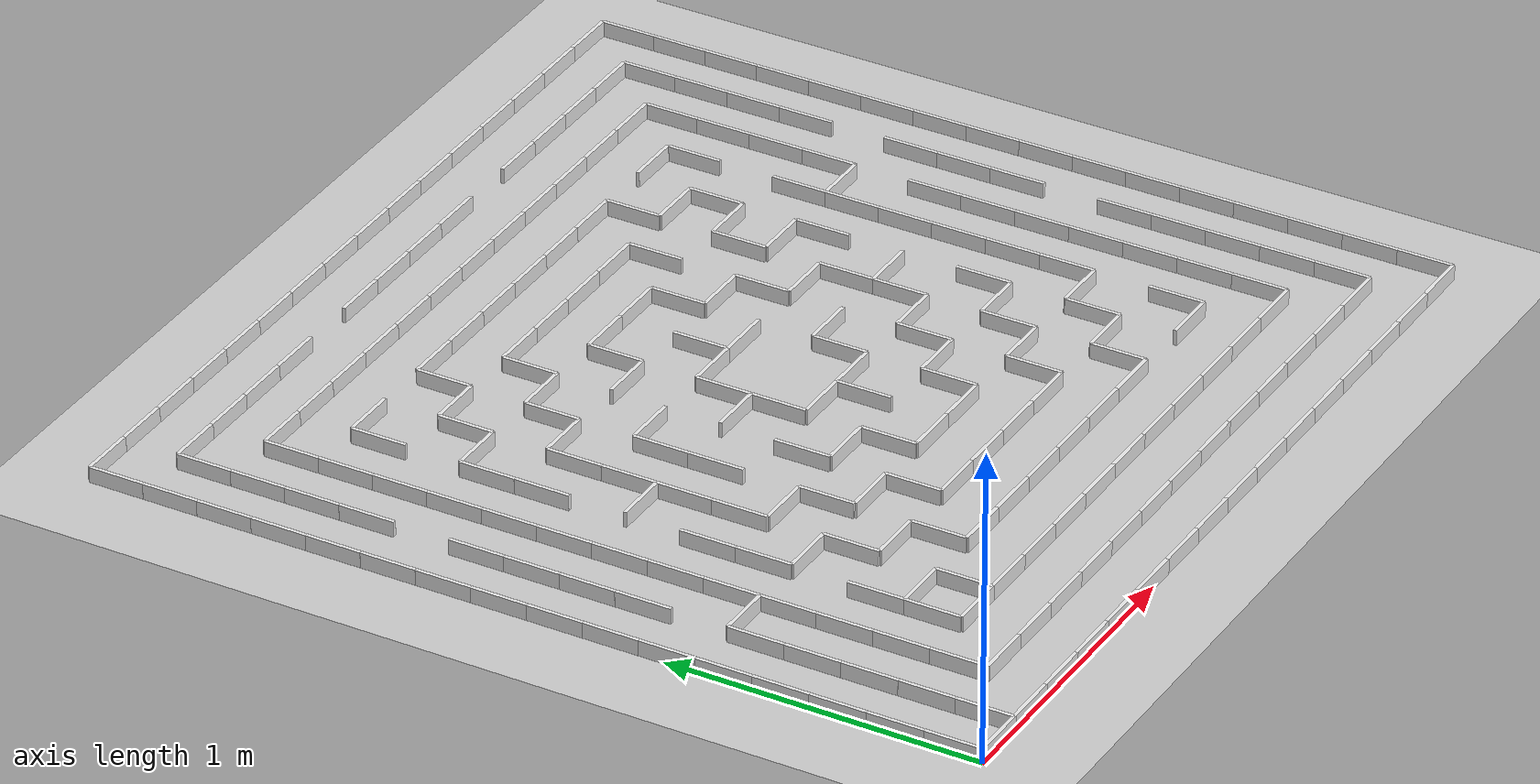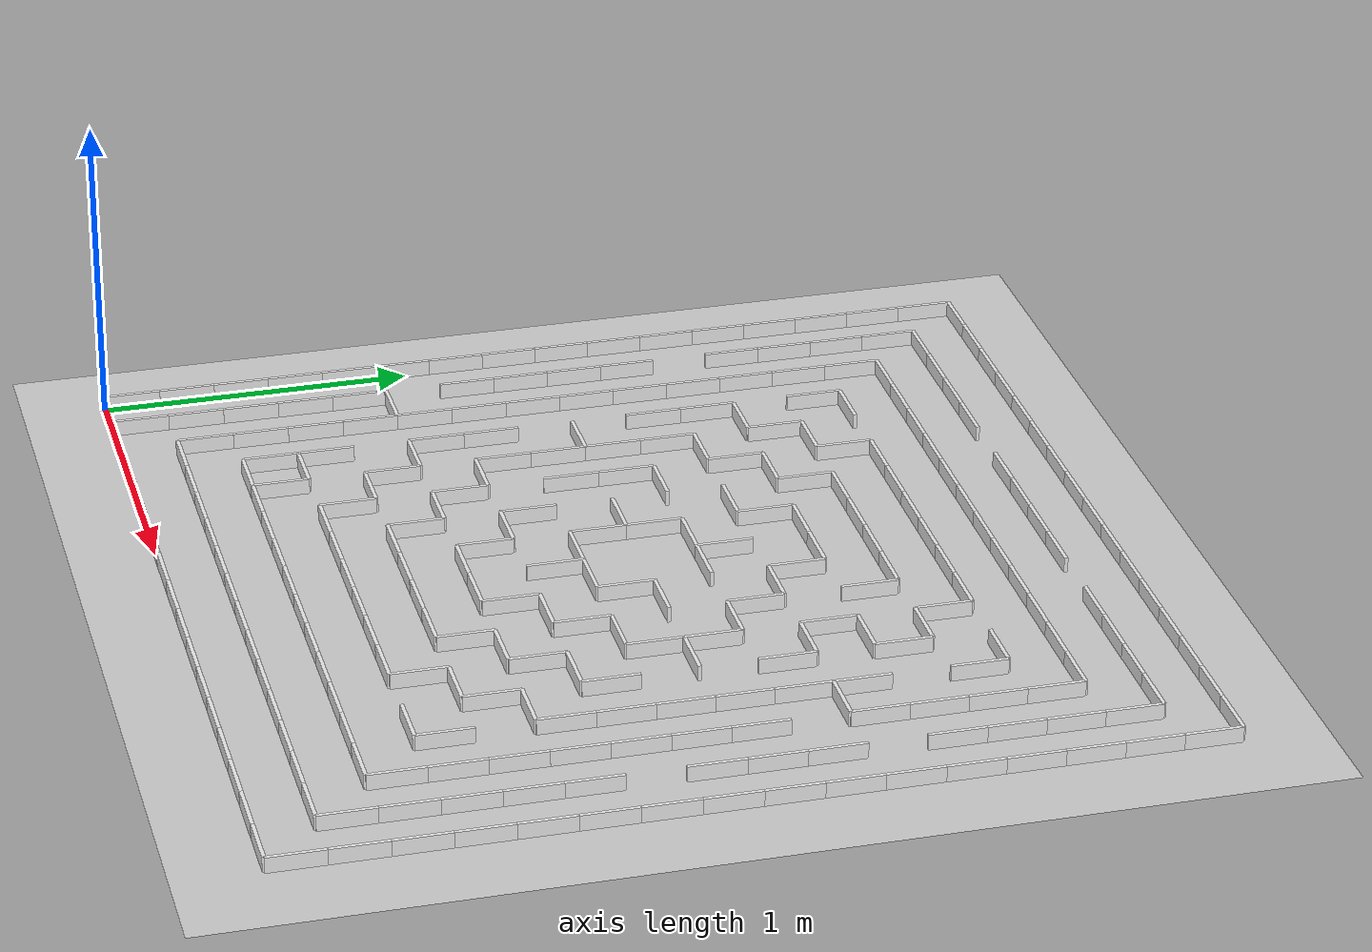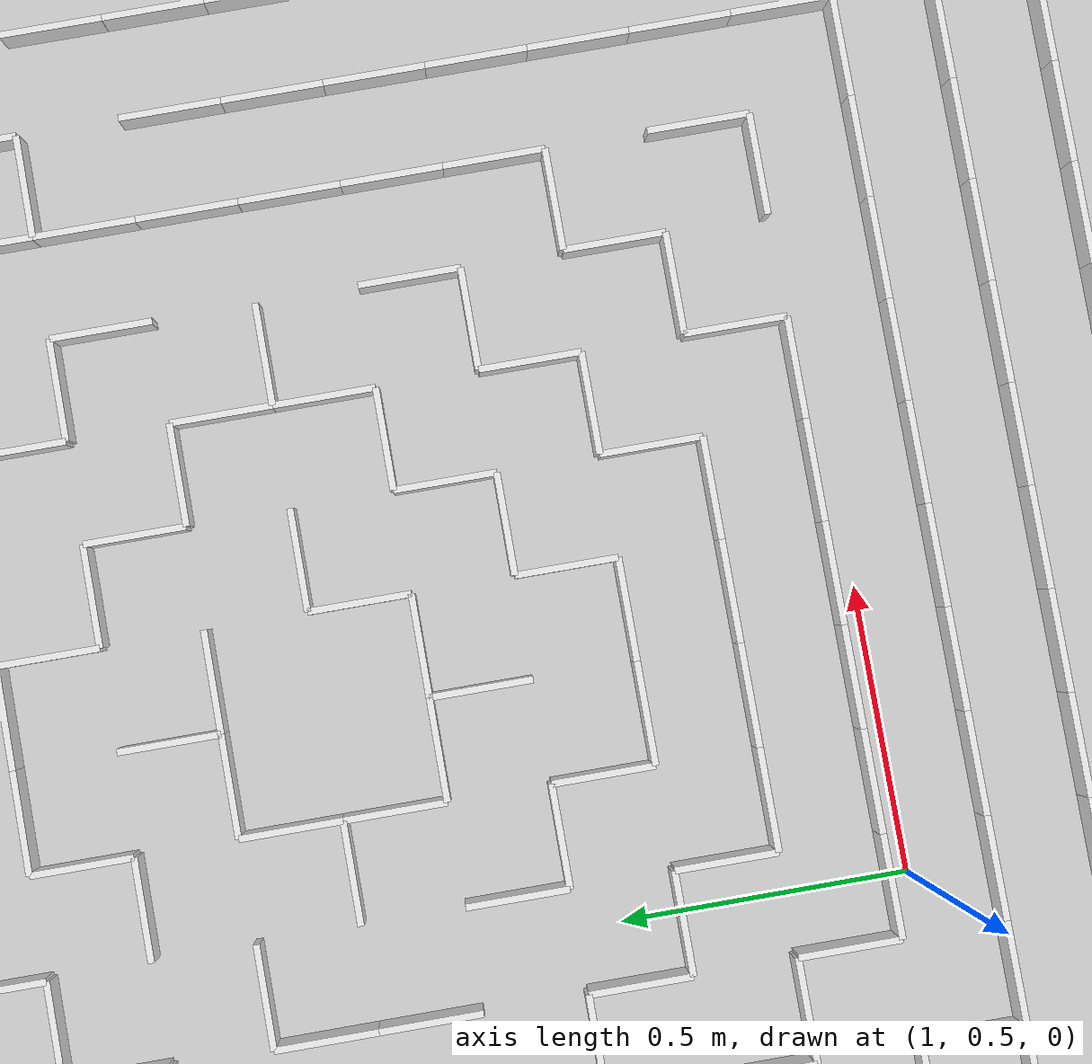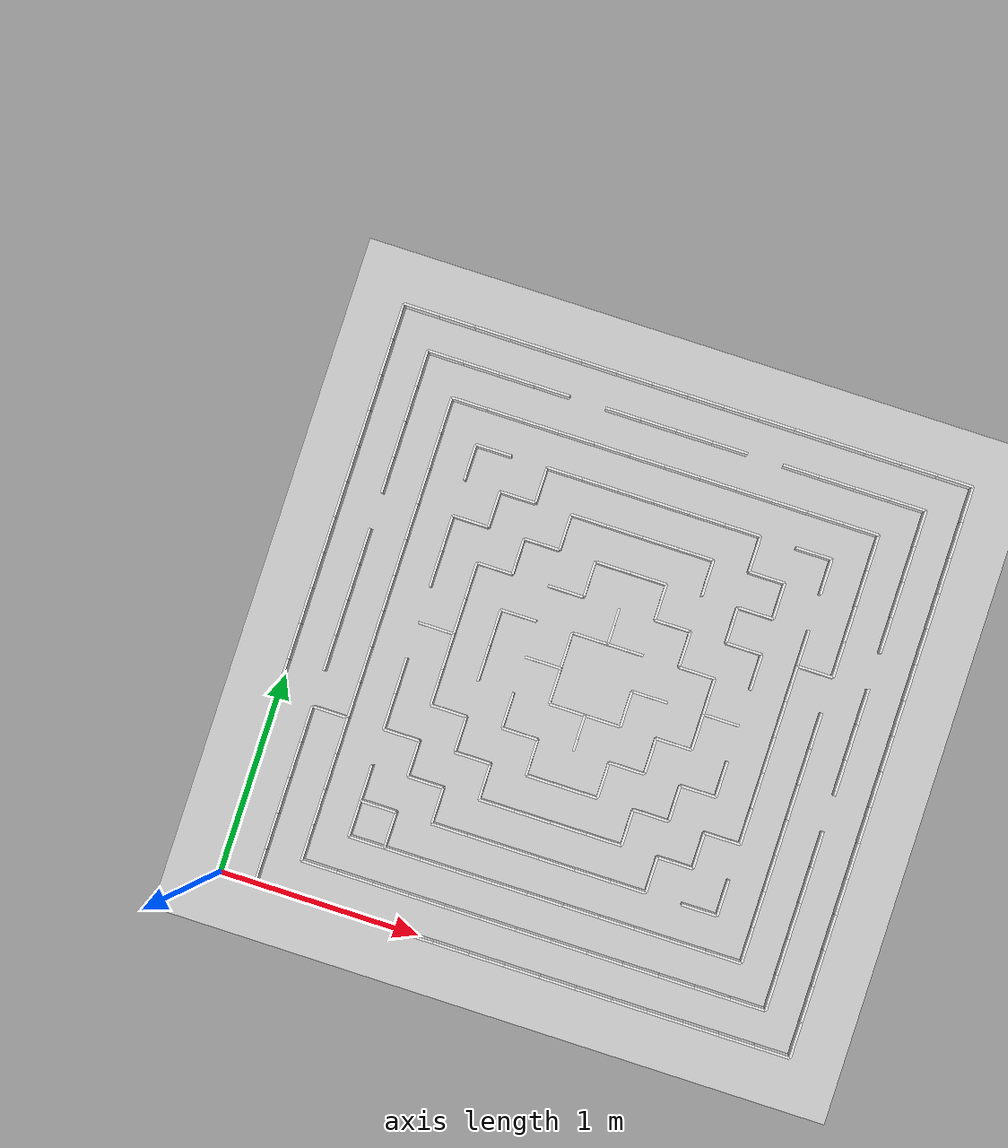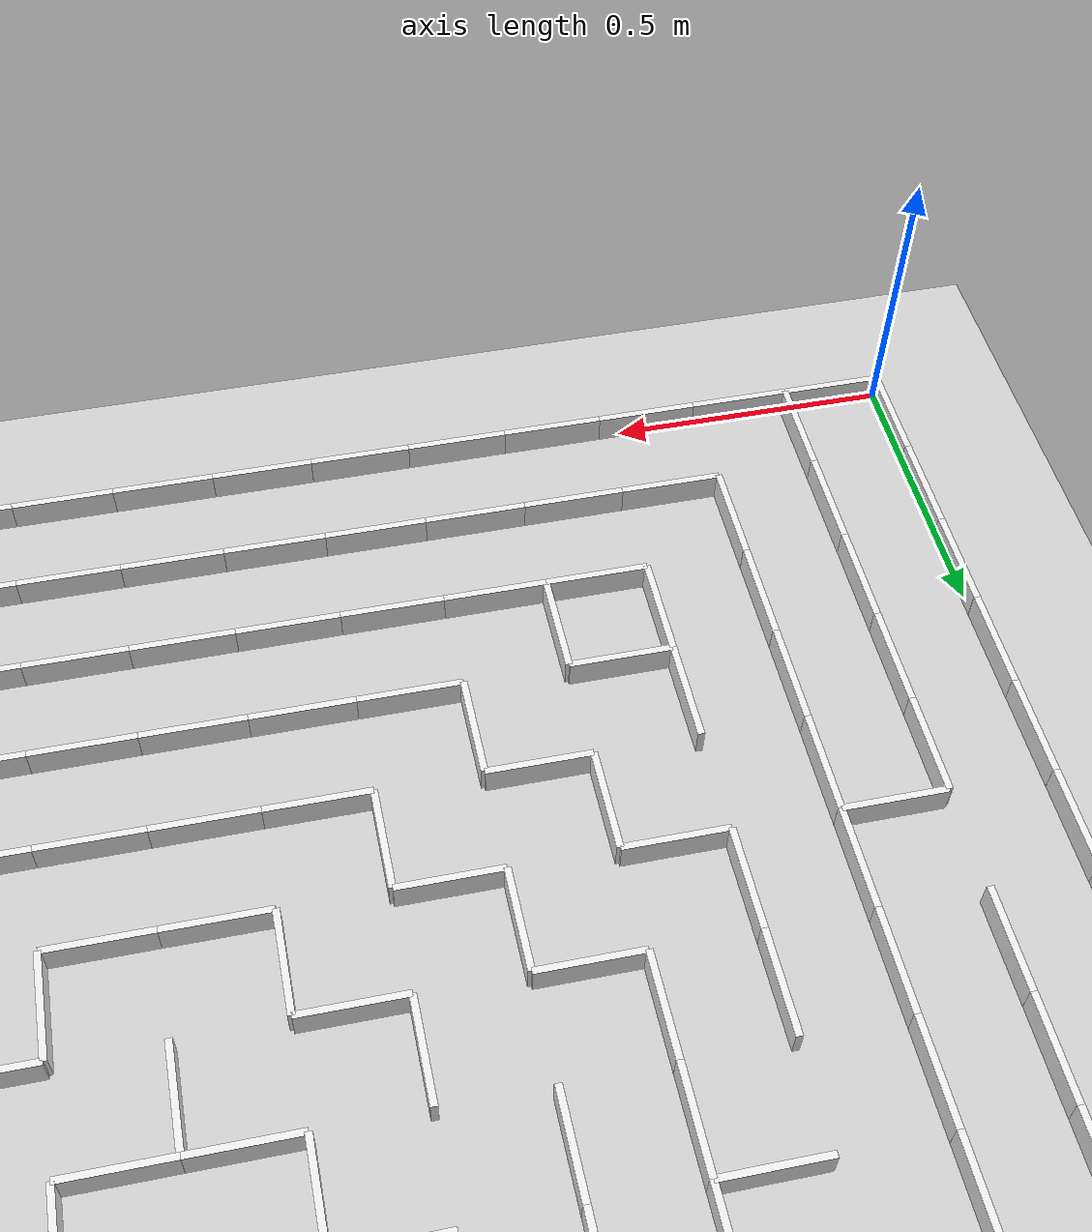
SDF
<?xml version="1.0" encoding="utf-8"?>
<!-- |    This document was autogenerated by xacro from /home/k-kame/catkin_ws/src/raspimouse_sim/raspimouse_gazebo/materials/newmaze.world.xacro | -->
<!-- |    EDITING THIS FILE BY HAND IS NOT RECOMMENDED                                 | -->
<sdf version="1.4">
  <world name="default">
    <include>
      <uri>model://ground_plane</uri>
    </include>
    <light name="sun" type="directional">
      <cast_shadows>1</cast_shadows>
      <pose>0 0 5 0 0 0</pose>
      <diffuse>0.8 0.8 0.8 1</diffuse>
      <specular>0.2 0.2 0.2 1</specular>
      <attenuation>
        <range>1000</range>
        <constant>0.9</constant>
        <linear>0.01</linear>
        <quadratic>0.001</quadratic>
      </attenuation>
      <direction>-0.5 0.1 -0.9</direction>
    </light>
    <physics type="ode">
      <max_step_size>0.001</max_step_size>
      <real_time_factor>1</real_time_factor>
      <real_time_update_rate>1000</real_time_update_rate>
      <gravity>0 0 -9.8</gravity>
    </physics>
    <gui fullscreen="0">
      <camera name="user_camera">
        <pose>-0.556842 -0.914575 1.68773 0 1.05964 0.520195</pose>
        <view_controller>orbit</view_controller>
      </camera>
    </gui>
    <model name="wall">
      <pose> 0.09 2.88 0.025 0 0 0 </pose>
      <link name="link">
        <inertial>
          <mass>10</mass>
          <inertia>
            <ixx>1</ixx>
            <ixy>0</ixy>
            <ixz>0</ixz>
            <iyy>1</iyy>
            <iyz>0</iyz>
            <izz>1</izz>
          </inertia>
        </inertial>
        <collision name="collision">
          <geometry>
            <box>
              <size>0.180 0.012 0.050</size>
            </box>
          </geometry>
          <max_contacts>10</max_contacts>
          <surface>
            <bounce/>
            <friction>
              <ode/>
            </friction>
            <contact>
              <ode/>
            </contact>
          </surface>
        </collision>
        <visual name="visual">
          <geometry>
            <box>
              <size>0.180 0.012 0.050</size>
            </box>
          </geometry>
          <material>
            <script>
              <uri>file://media/materials/scripts/gazebo.material</uri>
              <name>Gazebo/White</name>
            </script>
          </material>
        </visual>
        <velocity_decay>
          <linear>0</linear>
          <angular>0</angular>
        </velocity_decay>
        <self_collide>0</self_collide>
        <kinematic>0</kinematic>
        <gravity>1</gravity>
      </link>
      <static>1</static>
    </model>
    <model name="wall">
      <pose> 0.27 2.88 0.025 0 0 0 </pose>
      <link name="link">
        <inertial>
          <mass>10</mass>
          <inertia>
            <ixx>1</ixx>
            <ixy>0</ixy>
            <ixz>0</ixz>
            <iyy>1</iyy>
            <iyz>0</iyz>
            <izz>1</izz>
          </inertia>
        </inertial>
        <collision name="collision">
          <geometry>
            <box>
              <size>0.180 0.012 0.050</size>
            </box>
          </geometry>
          <max_contacts>10</max_contacts>
          <surface>
            <bounce/>
            <friction>
              <ode/>
            </friction>
            <contact>
              <ode/>
            </contact>
          </surface>
        </collision>
        <visual name="visual">
          <geometry>
            <box>
              <size>0.180 0.012 0.050</size>
            </box>
          </geometry>
          <material>
            <script>
              <uri>file://media/materials/scripts/gazebo.material</uri>
              <name>Gazebo/White</name>
            </script>
          </material>
        </visual>
        <velocity_decay>
          <linear>0</linear>
          <angular>0</angular>
        </velocity_decay>
        <self_collide>0</self_collide>
        <kinematic>0</kinematic>
        <gravity>1</gravity>
      </link>
      <static>1</static>
    </model>
    <model name="wall">
      <pose> 0.45 2.88 0.025 0 0 0 </pose>
      <link name="link">
        <inertial>
          <mass>10</mass>
          <inertia>
            <ixx>1</ixx>
            <ixy>0</ixy>
            <ixz>0</ixz>
            <iyy>1</iyy>
            <iyz>0</iyz>
            <izz>1</izz>
          </inertia>
        </inertial>
        <collision name="collision">
          <geometry>
            <box>
              <size>0.180 0.012 0.050</size>
            </box>
          </geometry>
          <max_contacts>10</max_contacts>
          <surface>
            <bounce/>
            <friction>
              <ode/>
            </friction>
            <contact>
              <ode/>
            </contact>
          </surface>
        </collision>
        <visual name="visual">
          <geometry>
            <box>
              <size>0.180 0.012 0.050</size>
            </box>
          </geometry>
          <material>
            <script>
              <uri>file://media/materials/scripts/gazebo.material</uri>
              <name>Gazebo/White</name>
            </script>
          </material>
        </visual>
        <velocity_decay>
          <linear>0</linear>
          <angular>0</angular>
        </velocity_decay>
        <self_collide>0</self_collide>
        <kinematic>0</kinematic>
        <gravity>1</gravity>
      </link>
      <static>1</static>
    </model>
    <model name="wall">
      <pose> 0.63 2.88 0.025 0 0 0 </pose>
      <link name="link">
        <inertial>
          <mass>10</mass>
          <inertia>
            <ixx>1</ixx>
            <ixy>0</ixy>
            <ixz>0</ixz>
            <iyy>1</iyy>
            <iyz>0</iyz>
            <izz>1</izz>
          </inertia>
        </inertial>
        <collision name="collision">
          <geometry>
            <box>
              <size>0.180 0.012 0.050</size>
            </box>
          </geometry>
          <max_contacts>10</max_contacts>
          <surface>
            <bounce/>
            <friction>
              <ode/>
            </friction>
            <contact>
              <ode/>
            </contact>
          </surface>
        </collision>
        <visual name="visual">
          <geometry>
            <box>
              <size>0.180 0.012 0.050</size>
            </box>
          </geometry>
          <material>
            <script>
              <uri>file://media/materials/scripts/gazebo.material</uri>
              <name>Gazebo/White</name>
            </script>
          </material>
        </visual>
        <velocity_decay>
          <linear>0</linear>
          <angular>0</angular>
        </velocity_decay>
        <self_collide>0</self_collide>
        <kinematic>0</kinematic>
        <gravity>1</gravity>
      </link>
      <static>1</static>
    </model>
    <model name="wall">
      <pose> 0.81 2.88 0.025 0 0 0 </pose>
      <link name="link">
        <inertial>
          <mass>10</mass>
          <inertia>
            <ixx>1</ixx>
            <ixy>0</ixy>
            <ixz>0</ixz>
            <iyy>1</iyy>
            <iyz>0</iyz>
            <izz>1</izz>
          </inertia>
        </inertial>
        <collision name="collision">
          <geometry>
            <box>
              <size>0.180 0.012 0.050</size>
            </box>
          </geometry>
          <max_contacts>10</max_contacts>
          <surface>
            <bounce/>
            <friction>
              <ode/>
            </friction>
            <contact>
              <ode/>
            </contact>
          </surface>
        </collision>
        <visual name="visual">
          <geometry>
            <box>
              <size>0.180 0.012 0.050</size>
            </box>
          </geometry>
          <material>
            <script>
              <uri>file://media/materials/scripts/gazebo.material</uri>
              <name>Gazebo/White</name>
            </script>
          </material>
        </visual>
        <velocity_decay>
          <linear>0</linear>
          <angular>0</angular>
        </velocity_decay>
        <self_collide>0</self_collide>
        <kinematic>0</kinematic>
        <gravity>1</gravity>
      </link>
      <static>1</static>
    </model>
    <model name="wall">
      <pose> 0.99 2.88 0.025 0 0 0 </pose>
      <link name="link">
        <inertial>
          <mass>10</mass>
          <inertia>
            <ixx>1</ixx>
            <ixy>0</ixy>
            <ixz>0</ixz>
            <iyy>1</iyy>
            <iyz>0</iyz>
            <izz>1</izz>
          </inertia>
        </inertial>
        <collision name="collision">
          <geometry>
            <box>
              <size>0.180 0.012 0.050</size>
            </box>
          </geometry>
          <max_contacts>10</max_contacts>
          <surface>
            <bounce/>
            <friction>
              <ode/>
            </friction>
            <contact>
              <ode/>
            </contact>
          </surface>
        </collision>
        <visual name="visual">
          <geometry>
            <box>
              <size>0.180 0.012 0.050</size>
            </box>
          </geometry>
          <material>
            <script>
              <uri>file://media/materials/scripts/gazebo.material</uri>
              <name>Gazebo/White</name>
            </script>
          </material>
        </visual>
        <velocity_decay>
          <linear>0</linear>
          <angular>0</angular>
        </velocity_decay>
        <self_collide>0</self_collide>
        <kinematic>0</kinematic>
        <gravity>1</gravity>
      </link>
      <static>1</static>
    </model>
    <model name="wall">
      <pose> 1.17 2.88 0.025 0 0 0 </pose>
      <link name="link">
        <inertial>
          <mass>10</mass>
          <inertia>
            <ixx>1</ixx>
            <ixy>0</ixy>
            <ixz>0</ixz>
            <iyy>1</iyy>
            <iyz>0</iyz>
            <izz>1</izz>
          </inertia>
        </inertial>
        <collision name="collision">
          <geometry>
            <box>
              <size>0.180 0.012 0.050</size>
            </box>
          </geometry>
          <max_contacts>10</max_contacts>
          <surface>
            <bounce/>
            <friction>
              <ode/>
            </friction>
            <contact>
              <ode/>
            </contact>
          </surface>
        </collision>
        <visual name="visual">
          <geometry>
            <box>
              <size>0.180 0.012 0.050</size>
            </box>
          </geometry>
          <material>
            <script>
              <uri>file://media/materials/scripts/gazebo.material</uri>
              <name>Gazebo/White</name>
            </script>
          </material>
        </visual>
        <velocity_decay>
          <linear>0</linear>
          <angular>0</angular>
        </velocity_decay>
        <self_collide>0</self_collide>
        <kinematic>0</kinematic>
        <gravity>1</gravity>
      </link>
      <static>1</static>
    </model>
    <model name="wall">
      <pose> 1.35 2.88 0.025 0 0 0 </pose>
      <link name="link">
        <inertial>
          <mass>10</mass>
          <inertia>
            <ixx>1</ixx>
            <ixy>0</ixy>
            <ixz>0</ixz>
            <iyy>1</iyy>
            <iyz>0</iyz>
            <izz>1</izz>
          </inertia>
        </inertial>
        <collision name="collision">
          <geometry>
            <box>
              <size>0.180 0.012 0.050</size>
            </box>
          </geometry>
          <max_contacts>10</max_contacts>
          <surface>
            <bounce/>
            <friction>
              <ode/>
            </friction>
            <contact>
              <ode/>
            </contact>
          </surface>
        </collision>
        <visual name="visual">
          <geometry>
            <box>
              <size>0.180 0.012 0.050</size>
            </box>
          </geometry>
          <material>
            <script>
              <uri>file://media/materials/scripts/gazebo.material</uri>
              <name>Gazebo/White</name>
            </script>
          </material>
        </visual>
        <velocity_decay>
          <linear>0</linear>
          <angular>0</angular>
        </velocity_decay>
        <self_collide>0</self_collide>
        <kinematic>0</kinematic>
        <gravity>1</gravity>
      </link>
      <static>1</static>
    </model>
    <model name="wall">
      <pose> 1.53 2.88 0.025 0 0 0 </pose>
      <link name="link">
        <inertial>
          <mass>10</mass>
          <inertia>
            <ixx>1</ixx>
            <ixy>0</ixy>
            <ixz>0</ixz>
            <iyy>1</iyy>
            <iyz>0</iyz>
            <izz>1</izz>
          </inertia>
        </inertial>
        <collision name="collision">
          <geometry>
            <box>
              <size>0.180 0.012 0.050</size>
            </box>
          </geometry>
          <max_contacts>10</max_contacts>
          <surface>
            <bounce/>
            <friction>
              <ode/>
            </friction>
            <contact>
              <ode/>
            </contact>
          </surface>
        </collision>
        <visual name="visual">
          <geometry>
            <box>
              <size>0.180 0.012 0.050</size>
            </box>
          </geometry>
          <material>
            <script>
              <uri>file://media/materials/scripts/gazebo.material</uri>
              <name>Gazebo/White</name>
            </script>
          </material>
        </visual>
        <velocity_decay>
          <linear>0</linear>
          <angular>0</angular>
        </velocity_decay>
        <self_collide>0</self_collide>
        <kinematic>0</kinematic>
        <gravity>1</gravity>
      </link>
      <static>1</static>
    </model>
    <model name="wall">
      <pose> 1.71 2.88 0.025 0 0 0 </pose>
      <link name="link">
        <inertial>
          <mass>10</mass>
          <inertia>
            <ixx>1</ixx>
            <ixy>0</ixy>
            <ixz>0</ixz>
            <iyy>1</iyy>
            <iyz>0</iyz>
            <izz>1</izz>
          </inertia>
        </inertial>
        <collision name="collision">
          <geometry>
            <box>
              <size>0.180 0.012 0.050</size>
            </box>
          </geometry>
          <max_contacts>10</max_contacts>
          <surface>
            <bounce/>
            <friction>
              <ode/>
            </friction>
            <contact>
              <ode/>
            </contact>
          </surface>
        </collision>
        <visual name="visual">
          <geometry>
            <box>
              <size>0.180 0.012 0.050</size>
            </box>
          </geometry>
          <material>
            <script>
              <uri>file://media/materials/scripts/gazebo.material</uri>
              <name>Gazebo/White</name>
            </script>
          </material>
        </visual>
        <velocity_decay>
          <linear>0</linear>
          <angular>0</angular>
        </velocity_decay>
        <self_collide>0</self_collide>
        <kinematic>0</kinematic>
        <gravity>1</gravity>
      </link>
      <static>1</static>
    </model>
    <model name="wall">
      <pose> 1.89 2.88 0.025 0 0 0 </pose>
      <link name="link">
        <inertial>
          <mass>10</mass>
          <inertia>
            <ixx>1</ixx>
            <ixy>0</ixy>
            <ixz>0</ixz>
            <iyy>1</iyy>
            <iyz>0</iyz>
            <izz>1</izz>
          </inertia>
        </inertial>
        <collision name="collision">
          <geometry>
            <box>
              <size>0.180 0.012 0.050</size>
            </box>
          </geometry>
          <max_contacts>10</max_contacts>
          <surface>
            <bounce/>
            <friction>
              <ode/>
            </friction>
            <contact>
              <ode/>
            </contact>
          </surface>
        </collision>
        <visual name="visual">
          <geometry>
            <box>
              <size>0.180 0.012 0.050</size>
            </box>
          </geometry>
          <material>
            <script>
              <uri>file://media/materials/scripts/gazebo.material</uri>
              <name>Gazebo/White</name>
            </script>
          </material>
        </visual>
        <velocity_decay>
          <linear>0</linear>
          <angular>0</angular>
        </velocity_decay>
        <self_collide>0</self_collide>
        <kinematic>0</kinematic>
        <gravity>1</gravity>
      </link>
      <static>1</static>
    </model>
    <model name="wall">
      <pose> 2.07 2.88 0.025 0 0 0 </pose>
      <link name="link">
        <inertial>
          <mass>10</mass>
          <inertia>
            <ixx>1</ixx>
            <ixy>0</ixy>
            <ixz>0</ixz>
            <iyy>1</iyy>
            <iyz>0</iyz>
            <izz>1</izz>
          </inertia>
        </inertial>
        <collision name="collision">
          <geometry>
            <box>
              <size>0.180 0.012 0.050</size>
            </box>
          </geometry>
          <max_contacts>10</max_contacts>
          <surface>
            <bounce/>
            <friction>
              <ode/>
            </friction>
            <contact>
              <ode/>
            </contact>
          </surface>
        </collision>
        <visual name="visual">
          <geometry>
            <box>
              <size>0.180 0.012 0.050</size>
            </box>
          </geometry>
          <material>
            <script>
              <uri>file://media/materials/scripts/gazebo.material</uri>
              <name>Gazebo/White</name>
            </script>
          </material>
        </visual>
        <velocity_decay>
          <linear>0</linear>
          <angular>0</angular>
        </velocity_decay>
        <self_collide>0</self_collide>
        <kinematic>0</kinematic>
        <gravity>1</gravity>
      </link>
      <static>1</static>
    </model>
    <model name="wall">
      <pose> 2.25 2.88 0.025 0 0 0 </pose>
      <link name="link">
        <inertial>
          <mass>10</mass>
          <inertia>
            <ixx>1</ixx>
            <ixy>0</ixy>
            <ixz>0</ixz>
            <iyy>1</iyy>
            <iyz>0</iyz>
            <izz>1</izz>
          </inertia>
        </inertial>
        <collision name="collision">
          <geometry>
            <box>
              <size>0.180 0.012 0.050</size>
            </box>
          </geometry>
          <max_contacts>10</max_contacts>
          <surface>
            <bounce/>
            <friction>
              <ode/>
            </friction>
            <contact>
              <ode/>
            </contact>
          </surface>
        </collision>
        <visual name="visual">
          <geometry>
            <box>
              <size>0.180 0.012 0.050</size>
            </box>
          </geometry>
          <material>
            <script>
              <uri>file://media/materials/scripts/gazebo.material</uri>
              <name>Gazebo/White</name>
            </script>
          </material>
        </visual>
        <velocity_decay>
          <linear>0</linear>
          <angular>0</angular>
        </velocity_decay>
        <self_collide>0</self_collide>
        <kinematic>0</kinematic>
        <gravity>1</gravity>
      </link>
      <static>1</static>
    </model>
    <model name="wall">
      <pose> 2.43 2.88 0.025 0 0 0 </pose>
      <link name="link">
        <inertial>
          <mass>10</mass>
          <inertia>
            <ixx>1</ixx>
            <ixy>0</ixy>
            <ixz>0</ixz>
            <iyy>1</iyy>
            <iyz>0</iyz>
            <izz>1</izz>
          </inertia>
        </inertial>
        <collision name="collision">
          <geometry>
            <box>
              <size>0.180 0.012 0.050</size>
            </box>
          </geometry>
          <max_contacts>10</max_contacts>
          <surface>
            <bounce/>
            <friction>
              <ode/>
            </friction>
            <contact>
              <ode/>
            </contact>
          </surface>
        </collision>
        <visual name="visual">
          <geometry>
            <box>
              <size>0.180 0.012 0.050</size>
            </box>
          </geometry>
          <material>
            <script>
              <uri>file://media/materials/scripts/gazebo.material</uri>
              <name>Gazebo/White</name>
            </script>
          </material>
        </visual>
        <velocity_decay>
          <linear>0</linear>
          <angular>0</angular>
        </velocity_decay>
        <self_collide>0</self_collide>
        <kinematic>0</kinematic>
        <gravity>1</gravity>
      </link>
      <static>1</static>
    </model>
    <model name="wall">
      <pose> 2.61 2.88 0.025 0 0 0 </pose>
      <link name="link">
        <inertial>
          <mass>10</mass>
          <inertia>
            <ixx>1</ixx>
            <ixy>0</ixy>
            <ixz>0</ixz>
            <iyy>1</iyy>
            <iyz>0</iyz>
            <izz>1</izz>
          </inertia>
        </inertial>
        <collision name="collision">
          <geometry>
            <box>
              <size>0.180 0.012 0.050</size>
            </box>
          </geometry>
          <max_contacts>10</max_contacts>
          <surface>
            <bounce/>
            <friction>
              <ode/>
            </friction>
            <contact>
              <ode/>
            </contact>
          </surface>
        </collision>
        <visual name="visual">
          <geometry>
            <box>
              <size>0.180 0.012 0.050</size>
            </box>
          </geometry>
          <material>
            <script>
              <uri>file://media/materials/scripts/gazebo.material</uri>
              <name>Gazebo/White</name>
            </script>
          </material>
        </visual>
        <velocity_decay>
          <linear>0</linear>
          <angular>0</angular>
        </velocity_decay>
        <self_collide>0</self_collide>
        <kinematic>0</kinematic>
        <gravity>1</gravity>
      </link>
      <static>1</static>
    </model>
    <model name="wall">
      <pose> 2.79 2.88 0.025 0 0 0 </pose>
      <link name="link">
        <inertial>
          <mass>10</mass>
          <inertia>
            <ixx>1</ixx>
            <ixy>0</ixy>
            <ixz>0</ixz>
            <iyy>1</iyy>
            <iyz>0</iyz>
            <izz>1</izz>
          </inertia>
        </inertial>
        <collision name="collision">
          <geometry>
            <box>
              <size>0.180 0.012 0.050</size>
            </box>
          </geometry>
          <max_contacts>10</max_contacts>
          <surface>
            <bounce/>
            <friction>
              <ode/>
            </friction>
            <contact>
              <ode/>
            </contact>
          </surface>
        </collision>
        <visual name="visual">
          <geometry>
            <box>
              <size>0.180 0.012 0.050</size>
            </box>
          </geometry>
          <material>
            <script>
              <uri>file://media/materials/scripts/gazebo.material</uri>
              <name>Gazebo/White</name>
            </script>
          </material>
        </visual>
        <velocity_decay>
          <linear>0</linear>
          <angular>0</angular>
        </velocity_decay>
        <self_collide>0</self_collide>
        <kinematic>0</kinematic>
        <gravity>1</gravity>
      </link>
      <static>1</static>
    </model>
    <model name="wall">
      <pose> 0.27 2.7 0.025 0 0 0 </pose>
      <link name="link">
        <inertial>
          <mass>10</mass>
          <inertia>
            <ixx>1</ixx>
            <ixy>0</ixy>
            <ixz>0</ixz>
            <iyy>1</iyy>
            <iyz>0</iyz>
            <izz>1</izz>
          </inertia>
        </inertial>
        <collision name="collision">
          <geometry>
            <box>
              <size>0.180 0.012 0.050</size>
            </box>
          </geometry>
          <max_contacts>10</max_contacts>
          <surface>
            <bounce/>
            <friction>
              <ode/>
            </friction>
            <contact>
              <ode/>
            </contact>
          </surface>
        </collision>
        <visual name="visual">
          <geometry>
            <box>
              <size>0.180 0.012 0.050</size>
            </box>
          </geometry>
          <material>
            <script>
              <uri>file://media/materials/scripts/gazebo.material</uri>
              <name>Gazebo/White</name>
            </script>
          </material>
        </visual>
        <velocity_decay>
          <linear>0</linear>
          <angular>0</angular>
        </velocity_decay>
        <self_collide>0</self_collide>
        <kinematic>0</kinematic>
        <gravity>1</gravity>
      </link>
      <static>1</static>
    </model>
    <model name="wall">
      <pose> 0.45 2.7 0.025 0 0 0 </pose>
      <link name="link">
        <inertial>
          <mass>10</mass>
          <inertia>
            <ixx>1</ixx>
            <ixy>0</ixy>
            <ixz>0</ixz>
            <iyy>1</iyy>
            <iyz>0</iyz>
            <izz>1</izz>
          </inertia>
        </inertial>
        <collision name="collision">
          <geometry>
            <box>
              <size>0.180 0.012 0.050</size>
            </box>
          </geometry>
          <max_contacts>10</max_contacts>
          <surface>
            <bounce/>
            <friction>
              <ode/>
            </friction>
            <contact>
              <ode/>
            </contact>
          </surface>
        </collision>
        <visual name="visual">
          <geometry>
            <box>
              <size>0.180 0.012 0.050</size>
            </box>
          </geometry>
          <material>
            <script>
              <uri>file://media/materials/scripts/gazebo.material</uri>
              <name>Gazebo/White</name>
            </script>
          </material>
        </visual>
        <velocity_decay>
          <linear>0</linear>
          <angular>0</angular>
        </velocity_decay>
        <self_collide>0</self_collide>
        <kinematic>0</kinematic>
        <gravity>1</gravity>
      </link>
      <static>1</static>
    </model>
    <model name="wall">
      <pose> 0.63 2.7 0.025 0 0 0 </pose>
      <link name="link">
        <inertial>
          <mass>10</mass>
          <inertia>
            <ixx>1</ixx>
            <ixy>0</ixy>
            <ixz>0</ixz>
            <iyy>1</iyy>
            <iyz>0</iyz>
            <izz>1</izz>
          </inertia>
        </inertial>
        <collision name="collision">
          <geometry>
            <box>
              <size>0.180 0.012 0.050</size>
            </box>
          </geometry>
          <max_contacts>10</max_contacts>
          <surface>
            <bounce/>
            <friction>
              <ode/>
            </friction>
            <contact>
              <ode/>
            </contact>
          </surface>
        </collision>
        <visual name="visual">
          <geometry>
            <box>
              <size>0.180 0.012 0.050</size>
            </box>
          </geometry>
          <material>
            <script>
              <uri>file://media/materials/scripts/gazebo.material</uri>
              <name>Gazebo/White</name>
            </script>
          </material>
        </visual>
        <velocity_decay>
          <linear>0</linear>
          <angular>0</angular>
        </velocity_decay>
        <self_collide>0</self_collide>
        <kinematic>0</kinematic>
        <gravity>1</gravity>
      </link>
      <static>1</static>
    </model>
    <model name="wall">
      <pose> 0.81 2.7 0.025 0 0 0 </pose>
      <link name="link">
        <inertial>
          <mass>10</mass>
          <inertia>
            <ixx>1</ixx>
            <ixy>0</ixy>
            <ixz>0</ixz>
            <iyy>1</iyy>
            <iyz>0</iyz>
            <izz>1</izz>
          </inertia>
        </inertial>
        <collision name="collision">
          <geometry>
            <box>
              <size>0.180 0.012 0.050</size>
            </box>
          </geometry>
          <max_contacts>10</max_contacts>
          <surface>
            <bounce/>
            <friction>
              <ode/>
            </friction>
            <contact>
              <ode/>
            </contact>
          </surface>
        </collision>
        <visual name="visual">
          <geometry>
            <box>
              <size>0.180 0.012 0.050</size>
            </box>
          </geometry>
          <material>
            <script>
              <uri>file://media/materials/scripts/gazebo.material</uri>
              <name>Gazebo/White</name>
            </script>
          </material>
        </visual>
        <velocity_decay>
          <linear>0</linear>
          <angular>0</angular>
        </velocity_decay>
        <self_collide>0</self_collide>
        <kinematic>0</kinematic>
        <gravity>1</gravity>
      </link>
      <static>1</static>
    </model>
    <model name="wall">
      <pose> 1.17 2.7 0.025 0 0 0 </pose>
      <link name="link">
        <inertial>
          <mass>10</mass>
          <inertia>
            <ixx>1</ixx>
            <ixy>0</ixy>
            <ixz>0</ixz>
            <iyy>1</iyy>
            <iyz>0</iyz>
            <izz>1</izz>
          </inertia>
        </inertial>
        <collision name="collision">
          <geometry>
            <box>
              <size>0.180 0.012 0.050</size>
            </box>
          </geometry>
          <max_contacts>10</max_contacts>
          <surface>
            <bounce/>
            <friction>
              <ode/>
            </friction>
            <contact>
              <ode/>
            </contact>
          </surface>
        </collision>
        <visual name="visual">
          <geometry>
            <box>
              <size>0.180 0.012 0.050</size>
            </box>
          </geometry>
          <material>
            <script>
              <uri>file://media/materials/scripts/gazebo.material</uri>
              <name>Gazebo/White</name>
            </script>
          </material>
        </visual>
        <velocity_decay>
          <linear>0</linear>
          <angular>0</angular>
        </velocity_decay>
        <self_collide>0</self_collide>
        <kinematic>0</kinematic>
        <gravity>1</gravity>
      </link>
      <static>1</static>
    </model>
    <model name="wall">
      <pose> 1.35 2.7 0.025 0 0 0 </pose>
      <link name="link">
        <inertial>
          <mass>10</mass>
          <inertia>
            <ixx>1</ixx>
            <ixy>0</ixy>
            <ixz>0</ixz>
            <iyy>1</iyy>
            <iyz>0</iyz>
            <izz>1</izz>
          </inertia>
        </inertial>
        <collision name="collision">
          <geometry>
            <box>
              <size>0.180 0.012 0.050</size>
            </box>
          </geometry>
          <max_contacts>10</max_contacts>
          <surface>
            <bounce/>
            <friction>
              <ode/>
            </friction>
            <contact>
              <ode/>
            </contact>
          </surface>
        </collision>
        <visual name="visual">
          <geometry>
            <box>
              <size>0.180 0.012 0.050</size>
            </box>
          </geometry>
          <material>
            <script>
              <uri>file://media/materials/scripts/gazebo.material</uri>
              <name>Gazebo/White</name>
            </script>
          </material>
        </visual>
        <velocity_decay>
          <linear>0</linear>
          <angular>0</angular>
        </velocity_decay>
        <self_collide>0</self_collide>
        <kinematic>0</kinematic>
        <gravity>1</gravity>
      </link>
      <static>1</static>
    </model>
    <model name="wall">
      <pose> 1.53 2.7 0.025 0 0 0 </pose>
      <link name="link">
        <inertial>
          <mass>10</mass>
          <inertia>
            <ixx>1</ixx>
            <ixy>0</ixy>
            <ixz>0</ixz>
            <iyy>1</iyy>
            <iyz>0</iyz>
            <izz>1</izz>
          </inertia>
        </inertial>
        <collision name="collision">
          <geometry>
            <box>
              <size>0.180 0.012 0.050</size>
            </box>
          </geometry>
          <max_contacts>10</max_contacts>
          <surface>
            <bounce/>
            <friction>
              <ode/>
            </friction>
            <contact>
              <ode/>
            </contact>
          </surface>
        </collision>
        <visual name="visual">
          <geometry>
            <box>
              <size>0.180 0.012 0.050</size>
            </box>
          </geometry>
          <material>
            <script>
              <uri>file://media/materials/scripts/gazebo.material</uri>
              <name>Gazebo/White</name>
            </script>
          </material>
        </visual>
        <velocity_decay>
          <linear>0</linear>
          <angular>0</angular>
        </velocity_decay>
        <self_collide>0</self_collide>
        <kinematic>0</kinematic>
        <gravity>1</gravity>
      </link>
      <static>1</static>
    </model>
    <model name="wall">
      <pose> 1.71 2.7 0.025 0 0 0 </pose>
      <link name="link">
        <inertial>
          <mass>10</mass>
          <inertia>
            <ixx>1</ixx>
            <ixy>0</ixy>
            <ixz>0</ixz>
            <iyy>1</iyy>
            <iyz>0</iyz>
            <izz>1</izz>
          </inertia>
        </inertial>
        <collision name="collision">
          <geometry>
            <box>
              <size>0.180 0.012 0.050</size>
            </box>
          </geometry>
          <max_contacts>10</max_contacts>
          <surface>
            <bounce/>
            <friction>
              <ode/>
            </friction>
            <contact>
              <ode/>
            </contact>
          </surface>
        </collision>
        <visual name="visual">
          <geometry>
            <box>
              <size>0.180 0.012 0.050</size>
            </box>
          </geometry>
          <material>
            <script>
              <uri>file://media/materials/scripts/gazebo.material</uri>
              <name>Gazebo/White</name>
            </script>
          </material>
        </visual>
        <velocity_decay>
          <linear>0</linear>
          <angular>0</angular>
        </velocity_decay>
        <self_collide>0</self_collide>
        <kinematic>0</kinematic>
        <gravity>1</gravity>
      </link>
      <static>1</static>
    </model>
    <model name="wall">
      <pose> 2.07 2.7 0.025 0 0 0 </pose>
      <link name="link">
        <inertial>
          <mass>10</mass>
          <inertia>
            <ixx>1</ixx>
            <ixy>0</ixy>
            <ixz>0</ixz>
            <iyy>1</iyy>
            <iyz>0</iyz>
            <izz>1</izz>
          </inertia>
        </inertial>
        <collision name="collision">
          <geometry>
            <box>
              <size>0.180 0.012 0.050</size>
            </box>
          </geometry>
          <max_contacts>10</max_contacts>
          <surface>
            <bounce/>
            <friction>
              <ode/>
            </friction>
            <contact>
              <ode/>
            </contact>
          </surface>
        </collision>
        <visual name="visual">
          <geometry>
            <box>
              <size>0.180 0.012 0.050</size>
            </box>
          </geometry>
          <material>
            <script>
              <uri>file://media/materials/scripts/gazebo.material</uri>
              <name>Gazebo/White</name>
            </script>
          </material>
        </visual>
        <velocity_decay>
          <linear>0</linear>
          <angular>0</angular>
        </velocity_decay>
        <self_collide>0</self_collide>
        <kinematic>0</kinematic>
        <gravity>1</gravity>
      </link>
      <static>1</static>
    </model>
    <model name="wall">
      <pose> 2.25 2.7 0.025 0 0 0 </pose>
      <link name="link">
        <inertial>
          <mass>10</mass>
          <inertia>
            <ixx>1</ixx>
            <ixy>0</ixy>
            <ixz>0</ixz>
            <iyy>1</iyy>
            <iyz>0</iyz>
            <izz>1</izz>
          </inertia>
        </inertial>
        <collision name="collision">
          <geometry>
            <box>
              <size>0.180 0.012 0.050</size>
            </box>
          </geometry>
          <max_contacts>10</max_contacts>
          <surface>
            <bounce/>
            <friction>
              <ode/>
            </friction>
            <contact>
              <ode/>
            </contact>
          </surface>
        </collision>
        <visual name="visual">
          <geometry>
            <box>
              <size>0.180 0.012 0.050</size>
            </box>
          </geometry>
          <material>
            <script>
              <uri>file://media/materials/scripts/gazebo.material</uri>
              <name>Gazebo/White</name>
            </script>
          </material>
        </visual>
        <velocity_decay>
          <linear>0</linear>
          <angular>0</angular>
        </velocity_decay>
        <self_collide>0</self_collide>
        <kinematic>0</kinematic>
        <gravity>1</gravity>
      </link>
      <static>1</static>
    </model>
    <model name="wall">
      <pose> 2.43 2.7 0.025 0 0 0 </pose>
      <link name="link">
        <inertial>
          <mass>10</mass>
          <inertia>
            <ixx>1</ixx>
            <ixy>0</ixy>
            <ixz>0</ixz>
            <iyy>1</iyy>
            <iyz>0</iyz>
            <izz>1</izz>
          </inertia>
        </inertial>
        <collision name="collision">
          <geometry>
            <box>
              <size>0.180 0.012 0.050</size>
            </box>
          </geometry>
          <max_contacts>10</max_contacts>
          <surface>
            <bounce/>
            <friction>
              <ode/>
            </friction>
            <contact>
              <ode/>
            </contact>
          </surface>
        </collision>
        <visual name="visual">
          <geometry>
            <box>
              <size>0.180 0.012 0.050</size>
            </box>
          </geometry>
          <material>
            <script>
              <uri>file://media/materials/scripts/gazebo.material</uri>
              <name>Gazebo/White</name>
            </script>
          </material>
        </visual>
        <velocity_decay>
          <linear>0</linear>
          <angular>0</angular>
        </velocity_decay>
        <self_collide>0</self_collide>
        <kinematic>0</kinematic>
        <gravity>1</gravity>
      </link>
      <static>1</static>
    </model>
    <model name="wall">
      <pose> 2.61 2.7 0.025 0 0 0 </pose>
      <link name="link">
        <inertial>
          <mass>10</mass>
          <inertia>
            <ixx>1</ixx>
            <ixy>0</ixy>
            <ixz>0</ixz>
            <iyy>1</iyy>
            <iyz>0</iyz>
            <izz>1</izz>
          </inertia>
        </inertial>
        <collision name="collision">
          <geometry>
            <box>
              <size>0.180 0.012 0.050</size>
            </box>
          </geometry>
          <max_contacts>10</max_contacts>
          <surface>
            <bounce/>
            <friction>
              <ode/>
            </friction>
            <contact>
              <ode/>
            </contact>
          </surface>
        </collision>
        <visual name="visual">
          <geometry>
            <box>
              <size>0.180 0.012 0.050</size>
            </box>
          </geometry>
          <material>
            <script>
              <uri>file://media/materials/scripts/gazebo.material</uri>
              <name>Gazebo/White</name>
            </script>
          </material>
        </visual>
        <velocity_decay>
          <linear>0</linear>
          <angular>0</angular>
        </velocity_decay>
        <self_collide>0</self_collide>
        <kinematic>0</kinematic>
        <gravity>1</gravity>
      </link>
      <static>1</static>
    </model>
    <model name="wall">
      <pose> 0.45 2.52 0.025 0 0 0 </pose>
      <link name="link">
        <inertial>
          <mass>10</mass>
          <inertia>
            <ixx>1</ixx>
            <ixy>0</ixy>
            <ixz>0</ixz>
            <iyy>1</iyy>
            <iyz>0</iyz>
            <izz>1</izz>
          </inertia>
        </inertial>
        <collision name="collision">
          <geometry>
            <box>
              <size>0.180 0.012 0.050</size>
            </box>
          </geometry>
          <max_contacts>10</max_contacts>
          <surface>
            <bounce/>
            <friction>
              <ode/>
            </friction>
            <contact>
              <ode/>
            </contact>
          </surface>
        </collision>
        <visual name="visual">
          <geometry>
            <box>
              <size>0.180 0.012 0.050</size>
            </box>
          </geometry>
          <material>
            <script>
              <uri>file://media/materials/scripts/gazebo.material</uri>
              <name>Gazebo/White</name>
            </script>
          </material>
        </visual>
        <velocity_decay>
          <linear>0</linear>
          <angular>0</angular>
        </velocity_decay>
        <self_collide>0</self_collide>
        <kinematic>0</kinematic>
        <gravity>1</gravity>
      </link>
      <static>1</static>
    </model>
    <model name="wall">
      <pose> 0.63 2.52 0.025 0 0 0 </pose>
      <link name="link">
        <inertial>
          <mass>10</mass>
          <inertia>
            <ixx>1</ixx>
            <ixy>0</ixy>
            <ixz>0</ixz>
            <iyy>1</iyy>
            <iyz>0</iyz>
            <izz>1</izz>
          </inertia>
        </inertial>
        <collision name="collision">
          <geometry>
            <box>
              <size>0.180 0.012 0.050</size>
            </box>
          </geometry>
          <max_contacts>10</max_contacts>
          <surface>
            <bounce/>
            <friction>
              <ode/>
            </friction>
            <contact>
              <ode/>
            </contact>
          </surface>
        </collision>
        <visual name="visual">
          <geometry>
            <box>
              <size>0.180 0.012 0.050</size>
            </box>
          </geometry>
          <material>
            <script>
              <uri>file://media/materials/scripts/gazebo.material</uri>
              <name>Gazebo/White</name>
            </script>
          </material>
        </visual>
        <velocity_decay>
          <linear>0</linear>
          <angular>0</angular>
        </velocity_decay>
        <self_collide>0</self_collide>
        <kinematic>0</kinematic>
        <gravity>1</gravity>
      </link>
      <static>1</static>
    </model>
    <model name="wall">
      <pose> 0.81 2.52 0.025 0 0 0 </pose>
      <link name="link">
        <inertial>
          <mass>10</mass>
          <inertia>
            <ixx>1</ixx>
            <ixy>0</ixy>
            <ixz>0</ixz>
            <iyy>1</iyy>
            <iyz>0</iyz>
            <izz>1</izz>
          </inertia>
        </inertial>
        <collision name="collision">
          <geometry>
            <box>
              <size>0.180 0.012 0.050</size>
            </box>
          </geometry>
          <max_contacts>10</max_contacts>
          <surface>
            <bounce/>
            <friction>
              <ode/>
            </friction>
            <contact>
              <ode/>
            </contact>
          </surface>
        </collision>
        <visual name="visual">
          <geometry>
            <box>
              <size>0.180 0.012 0.050</size>
            </box>
          </geometry>
          <material>
            <script>
              <uri>file://media/materials/scripts/gazebo.material</uri>
              <name>Gazebo/White</name>
            </script>
          </material>
        </visual>
        <velocity_decay>
          <linear>0</linear>
          <angular>0</angular>
        </velocity_decay>
        <self_collide>0</self_collide>
        <kinematic>0</kinematic>
        <gravity>1</gravity>
      </link>
      <static>1</static>
    </model>
    <model name="wall">
      <pose> 0.99 2.52 0.025 0 0 0 </pose>
      <link name="link">
        <inertial>
          <mass>10</mass>
          <inertia>
            <ixx>1</ixx>
            <ixy>0</ixy>
            <ixz>0</ixz>
            <iyy>1</iyy>
            <iyz>0</iyz>
            <izz>1</izz>
          </inertia>
        </inertial>
        <collision name="collision">
          <geometry>
            <box>
              <size>0.180 0.012 0.050</size>
            </box>
          </geometry>
          <max_contacts>10</max_contacts>
          <surface>
            <bounce/>
            <friction>
              <ode/>
            </friction>
            <contact>
              <ode/>
            </contact>
          </surface>
        </collision>
        <visual name="visual">
          <geometry>
            <box>
              <size>0.180 0.012 0.050</size>
            </box>
          </geometry>
          <material>
            <script>
              <uri>file://media/materials/scripts/gazebo.material</uri>
              <name>Gazebo/White</name>
            </script>
          </material>
        </visual>
        <velocity_decay>
          <linear>0</linear>
          <angular>0</angular>
        </velocity_decay>
        <self_collide>0</self_collide>
        <kinematic>0</kinematic>
        <gravity>1</gravity>
      </link>
      <static>1</static>
    </model>
    <model name="wall">
      <pose> 1.17 2.52 0.025 0 0 0 </pose>
      <link name="link">
        <inertial>
          <mass>10</mass>
          <inertia>
            <ixx>1</ixx>
            <ixy>0</ixy>
            <ixz>0</ixz>
            <iyy>1</iyy>
            <iyz>0</iyz>
            <izz>1</izz>
          </inertia>
        </inertial>
        <collision name="collision">
          <geometry>
            <box>
              <size>0.180 0.012 0.050</size>
            </box>
          </geometry>
          <max_contacts>10</max_contacts>
          <surface>
            <bounce/>
            <friction>
              <ode/>
            </friction>
            <contact>
              <ode/>
            </contact>
          </surface>
        </collision>
        <visual name="visual">
          <geometry>
            <box>
              <size>0.180 0.012 0.050</size>
            </box>
          </geometry>
          <material>
            <script>
              <uri>file://media/materials/scripts/gazebo.material</uri>
              <name>Gazebo/White</name>
            </script>
          </material>
        </visual>
        <velocity_decay>
          <linear>0</linear>
          <angular>0</angular>
        </velocity_decay>
        <self_collide>0</self_collide>
        <kinematic>0</kinematic>
        <gravity>1</gravity>
      </link>
      <static>1</static>
    </model>
    <model name="wall">
      <pose> 1.35 2.52 0.025 0 0 0 </pose>
      <link name="link">
        <inertial>
          <mass>10</mass>
          <inertia>
            <ixx>1</ixx>
            <ixy>0</ixy>
            <ixz>0</ixz>
            <iyy>1</iyy>
            <iyz>0</iyz>
            <izz>1</izz>
          </inertia>
        </inertial>
        <collision name="collision">
          <geometry>
            <box>
              <size>0.180 0.012 0.050</size>
            </box>
          </geometry>
          <max_contacts>10</max_contacts>
          <surface>
            <bounce/>
            <friction>
              <ode/>
            </friction>
            <contact>
              <ode/>
            </contact>
          </surface>
        </collision>
        <visual name="visual">
          <geometry>
            <box>
              <size>0.180 0.012 0.050</size>
            </box>
          </geometry>
          <material>
            <script>
              <uri>file://media/materials/scripts/gazebo.material</uri>
              <name>Gazebo/White</name>
            </script>
          </material>
        </visual>
        <velocity_decay>
          <linear>0</linear>
          <angular>0</angular>
        </velocity_decay>
        <self_collide>0</self_collide>
        <kinematic>0</kinematic>
        <gravity>1</gravity>
      </link>
      <static>1</static>
    </model>
    <model name="wall">
      <pose> 1.53 2.52 0.025 0 0 0 </pose>
      <link name="link">
        <inertial>
          <mass>10</mass>
          <inertia>
            <ixx>1</ixx>
            <ixy>0</ixy>
            <ixz>0</ixz>
            <iyy>1</iyy>
            <iyz>0</iyz>
            <izz>1</izz>
          </inertia>
        </inertial>
        <collision name="collision">
          <geometry>
            <box>
              <size>0.180 0.012 0.050</size>
            </box>
          </geometry>
          <max_contacts>10</max_contacts>
          <surface>
            <bounce/>
            <friction>
              <ode/>
            </friction>
            <contact>
              <ode/>
            </contact>
          </surface>
        </collision>
        <visual name="visual">
          <geometry>
            <box>
              <size>0.180 0.012 0.050</size>
            </box>
          </geometry>
          <material>
            <script>
              <uri>file://media/materials/scripts/gazebo.material</uri>
              <name>Gazebo/White</name>
            </script>
          </material>
        </visual>
        <velocity_decay>
          <linear>0</linear>
          <angular>0</angular>
        </velocity_decay>
        <self_collide>0</self_collide>
        <kinematic>0</kinematic>
        <gravity>1</gravity>
      </link>
      <static>1</static>
    </model>
    <model name="wall">
      <pose> 1.71 2.52 0.025 0 0 0 </pose>
      <link name="link">
        <inertial>
          <mass>10</mass>
          <inertia>
            <ixx>1</ixx>
            <ixy>0</ixy>
            <ixz>0</ixz>
            <iyy>1</iyy>
            <iyz>0</iyz>
            <izz>1</izz>
          </inertia>
        </inertial>
        <collision name="collision">
          <geometry>
            <box>
              <size>0.180 0.012 0.050</size>
            </box>
          </geometry>
          <max_contacts>10</max_contacts>
          <surface>
            <bounce/>
            <friction>
              <ode/>
            </friction>
            <contact>
              <ode/>
            </contact>
          </surface>
        </collision>
        <visual name="visual">
          <geometry>
            <box>
              <size>0.180 0.012 0.050</size>
            </box>
          </geometry>
          <material>
            <script>
              <uri>file://media/materials/scripts/gazebo.material</uri>
              <name>Gazebo/White</name>
            </script>
          </material>
        </visual>
        <velocity_decay>
          <linear>0</linear>
          <angular>0</angular>
        </velocity_decay>
        <self_collide>0</self_collide>
        <kinematic>0</kinematic>
        <gravity>1</gravity>
      </link>
      <static>1</static>
    </model>
    <model name="wall">
      <pose> 1.89 2.52 0.025 0 0 0 </pose>
      <link name="link">
        <inertial>
          <mass>10</mass>
          <inertia>
            <ixx>1</ixx>
            <ixy>0</ixy>
            <ixz>0</ixz>
            <iyy>1</iyy>
            <iyz>0</iyz>
            <izz>1</izz>
          </inertia>
        </inertial>
        <collision name="collision">
          <geometry>
            <box>
              <size>0.180 0.012 0.050</size>
            </box>
          </geometry>
          <max_contacts>10</max_contacts>
          <surface>
            <bounce/>
            <friction>
              <ode/>
            </friction>
            <contact>
              <ode/>
            </contact>
          </surface>
        </collision>
        <visual name="visual">
          <geometry>
            <box>
              <size>0.180 0.012 0.050</size>
            </box>
          </geometry>
          <material>
            <script>
              <uri>file://media/materials/scripts/gazebo.material</uri>
              <name>Gazebo/White</name>
            </script>
          </material>
        </visual>
        <velocity_decay>
          <linear>0</linear>
          <angular>0</angular>
        </velocity_decay>
        <self_collide>0</self_collide>
        <kinematic>0</kinematic>
        <gravity>1</gravity>
      </link>
      <static>1</static>
    </model>
    <model name="wall">
      <pose> 2.07 2.52 0.025 0 0 0 </pose>
      <link name="link">
        <inertial>
          <mass>10</mass>
          <inertia>
            <ixx>1</ixx>
            <ixy>0</ixy>
            <ixz>0</ixz>
            <iyy>1</iyy>
            <iyz>0</iyz>
            <izz>1</izz>
          </inertia>
        </inertial>
        <collision name="collision">
          <geometry>
            <box>
              <size>0.180 0.012 0.050</size>
            </box>
          </geometry>
          <max_contacts>10</max_contacts>
          <surface>
            <bounce/>
            <friction>
              <ode/>
            </friction>
            <contact>
              <ode/>
            </contact>
          </surface>
        </collision>
        <visual name="visual">
          <geometry>
            <box>
              <size>0.180 0.012 0.050</size>
            </box>
          </geometry>
          <material>
            <script>
              <uri>file://media/materials/scripts/gazebo.material</uri>
              <name>Gazebo/White</name>
            </script>
          </material>
        </visual>
        <velocity_decay>
          <linear>0</linear>
          <angular>0</angular>
        </velocity_decay>
        <self_collide>0</self_collide>
        <kinematic>0</kinematic>
        <gravity>1</gravity>
      </link>
      <static>1</static>
    </model>
    <model name="wall">
      <pose> 2.25 2.52 0.025 0 0 0 </pose>
      <link name="link">
        <inertial>
          <mass>10</mass>
          <inertia>
            <ixx>1</ixx>
            <ixy>0</ixy>
            <ixz>0</ixz>
            <iyy>1</iyy>
            <iyz>0</iyz>
            <izz>1</izz>
          </inertia>
        </inertial>
        <collision name="collision">
          <geometry>
            <box>
              <size>0.180 0.012 0.050</size>
            </box>
          </geometry>
          <max_contacts>10</max_contacts>
          <surface>
            <bounce/>
            <friction>
              <ode/>
            </friction>
            <contact>
              <ode/>
            </contact>
          </surface>
        </collision>
        <visual name="visual">
          <geometry>
            <box>
              <size>0.180 0.012 0.050</size>
            </box>
          </geometry>
          <material>
            <script>
              <uri>file://media/materials/scripts/gazebo.material</uri>
              <name>Gazebo/White</name>
            </script>
          </material>
        </visual>
        <velocity_decay>
          <linear>0</linear>
          <angular>0</angular>
        </velocity_decay>
        <self_collide>0</self_collide>
        <kinematic>0</kinematic>
        <gravity>1</gravity>
      </link>
      <static>1</static>
    </model>
    <model name="wall">
      <pose> 2.43 2.52 0.025 0 0 0 </pose>
      <link name="link">
        <inertial>
          <mass>10</mass>
          <inertia>
            <ixx>1</ixx>
            <ixy>0</ixy>
            <ixz>0</ixz>
            <iyy>1</iyy>
            <iyz>0</iyz>
            <izz>1</izz>
          </inertia>
        </inertial>
        <collision name="collision">
          <geometry>
            <box>
              <size>0.180 0.012 0.050</size>
            </box>
          </geometry>
          <max_contacts>10</max_contacts>
          <surface>
            <bounce/>
            <friction>
              <ode/>
            </friction>
            <contact>
              <ode/>
            </contact>
          </surface>
        </collision>
        <visual name="visual">
          <geometry>
            <box>
              <size>0.180 0.012 0.050</size>
            </box>
          </geometry>
          <material>
            <script>
              <uri>file://media/materials/scripts/gazebo.material</uri>
              <name>Gazebo/White</name>
            </script>
          </material>
        </visual>
        <velocity_decay>
          <linear>0</linear>
          <angular>0</angular>
        </velocity_decay>
        <self_collide>0</self_collide>
        <kinematic>0</kinematic>
        <gravity>1</gravity>
      </link>
      <static>1</static>
    </model>
    <model name="wall">
      <pose> 0.63 2.34 0.025 0 0 0 </pose>
      <link name="link">
        <inertial>
          <mass>10</mass>
          <inertia>
            <ixx>1</ixx>
            <ixy>0</ixy>
            <ixz>0</ixz>
            <iyy>1</iyy>
            <iyz>0</iyz>
            <izz>1</izz>
          </inertia>
        </inertial>
        <collision name="collision">
          <geometry>
            <box>
              <size>0.180 0.012 0.050</size>
            </box>
          </geometry>
          <max_contacts>10</max_contacts>
          <surface>
            <bounce/>
            <friction>
              <ode/>
            </friction>
            <contact>
              <ode/>
            </contact>
          </surface>
        </collision>
        <visual name="visual">
          <geometry>
            <box>
              <size>0.180 0.012 0.050</size>
            </box>
          </geometry>
          <material>
            <script>
              <uri>file://media/materials/scripts/gazebo.material</uri>
              <name>Gazebo/White</name>
            </script>
          </material>
        </visual>
        <velocity_decay>
          <linear>0</linear>
          <angular>0</angular>
        </velocity_decay>
        <self_collide>0</self_collide>
        <kinematic>0</kinematic>
        <gravity>1</gravity>
      </link>
      <static>1</static>
    </model>
    <model name="wall">
      <pose> 0.99 2.34 0.025 0 0 0 </pose>
      <link name="link">
        <inertial>
          <mass>10</mass>
          <inertia>
            <ixx>1</ixx>
            <ixy>0</ixy>
            <ixz>0</ixz>
            <iyy>1</iyy>
            <iyz>0</iyz>
            <izz>1</izz>
          </inertia>
        </inertial>
        <collision name="collision">
          <geometry>
            <box>
              <size>0.180 0.012 0.050</size>
            </box>
          </geometry>
          <max_contacts>10</max_contacts>
          <surface>
            <bounce/>
            <friction>
              <ode/>
            </friction>
            <contact>
              <ode/>
            </contact>
          </surface>
        </collision>
        <visual name="visual">
          <geometry>
            <box>
              <size>0.180 0.012 0.050</size>
            </box>
          </geometry>
          <material>
            <script>
              <uri>file://media/materials/scripts/gazebo.material</uri>
              <name>Gazebo/White</name>
            </script>
          </material>
        </visual>
        <velocity_decay>
          <linear>0</linear>
          <angular>0</angular>
        </velocity_decay>
        <self_collide>0</self_collide>
        <kinematic>0</kinematic>
        <gravity>1</gravity>
      </link>
      <static>1</static>
    </model>
    <model name="wall">
      <pose> 1.17 2.34 0.025 0 0 0 </pose>
      <link name="link">
        <inertial>
          <mass>10</mass>
          <inertia>
            <ixx>1</ixx>
            <ixy>0</ixy>
            <ixz>0</ixz>
            <iyy>1</iyy>
            <iyz>0</iyz>
            <izz>1</izz>
          </inertia>
        </inertial>
        <collision name="collision">
          <geometry>
            <box>
              <size>0.180 0.012 0.050</size>
            </box>
          </geometry>
          <max_contacts>10</max_contacts>
          <surface>
            <bounce/>
            <friction>
              <ode/>
            </friction>
            <contact>
              <ode/>
            </contact>
          </surface>
        </collision>
        <visual name="visual">
          <geometry>
            <box>
              <size>0.180 0.012 0.050</size>
            </box>
          </geometry>
          <material>
            <script>
              <uri>file://media/materials/scripts/gazebo.material</uri>
              <name>Gazebo/White</name>
            </script>
          </material>
        </visual>
        <velocity_decay>
          <linear>0</linear>
          <angular>0</angular>
        </velocity_decay>
        <self_collide>0</self_collide>
        <kinematic>0</kinematic>
        <gravity>1</gravity>
      </link>
      <static>1</static>
    </model>
    <model name="wall">
      <pose> 1.35 2.34 0.025 0 0 0 </pose>
      <link name="link">
        <inertial>
          <mass>10</mass>
          <inertia>
            <ixx>1</ixx>
            <ixy>0</ixy>
            <ixz>0</ixz>
            <iyy>1</iyy>
            <iyz>0</iyz>
            <izz>1</izz>
          </inertia>
        </inertial>
        <collision name="collision">
          <geometry>
            <box>
              <size>0.180 0.012 0.050</size>
            </box>
          </geometry>
          <max_contacts>10</max_contacts>
          <surface>
            <bounce/>
            <friction>
              <ode/>
            </friction>
            <contact>
              <ode/>
            </contact>
          </surface>
        </collision>
        <visual name="visual">
          <geometry>
            <box>
              <size>0.180 0.012 0.050</size>
            </box>
          </geometry>
          <material>
            <script>
              <uri>file://media/materials/scripts/gazebo.material</uri>
              <name>Gazebo/White</name>
            </script>
          </material>
        </visual>
        <velocity_decay>
          <linear>0</linear>
          <angular>0</angular>
        </velocity_decay>
        <self_collide>0</self_collide>
        <kinematic>0</kinematic>
        <gravity>1</gravity>
      </link>
      <static>1</static>
    </model>
    <model name="wall">
      <pose> 1.53 2.34 0.025 0 0 0 </pose>
      <link name="link">
        <inertial>
          <mass>10</mass>
          <inertia>
            <ixx>1</ixx>
            <ixy>0</ixy>
            <ixz>0</ixz>
            <iyy>1</iyy>
            <iyz>0</iyz>
            <izz>1</izz>
          </inertia>
        </inertial>
        <collision name="collision">
          <geometry>
            <box>
              <size>0.180 0.012 0.050</size>
            </box>
          </geometry>
          <max_contacts>10</max_contacts>
          <surface>
            <bounce/>
            <friction>
              <ode/>
            </friction>
            <contact>
              <ode/>
            </contact>
          </surface>
        </collision>
        <visual name="visual">
          <geometry>
            <box>
              <size>0.180 0.012 0.050</size>
            </box>
          </geometry>
          <material>
            <script>
              <uri>file://media/materials/scripts/gazebo.material</uri>
              <name>Gazebo/White</name>
            </script>
          </material>
        </visual>
        <velocity_decay>
          <linear>0</linear>
          <angular>0</angular>
        </velocity_decay>
        <self_collide>0</self_collide>
        <kinematic>0</kinematic>
        <gravity>1</gravity>
      </link>
      <static>1</static>
    </model>
    <model name="wall">
      <pose> 1.71 2.34 0.025 0 0 0 </pose>
      <link name="link">
        <inertial>
          <mass>10</mass>
          <inertia>
            <ixx>1</ixx>
            <ixy>0</ixy>
            <ixz>0</ixz>
            <iyy>1</iyy>
            <iyz>0</iyz>
            <izz>1</izz>
          </inertia>
        </inertial>
        <collision name="collision">
          <geometry>
            <box>
              <size>0.180 0.012 0.050</size>
            </box>
          </geometry>
          <max_contacts>10</max_contacts>
          <surface>
            <bounce/>
            <friction>
              <ode/>
            </friction>
            <contact>
              <ode/>
            </contact>
          </surface>
        </collision>
        <visual name="visual">
          <geometry>
            <box>
              <size>0.180 0.012 0.050</size>
            </box>
          </geometry>
          <material>
            <script>
              <uri>file://media/materials/scripts/gazebo.material</uri>
              <name>Gazebo/White</name>
            </script>
          </material>
        </visual>
        <velocity_decay>
          <linear>0</linear>
          <angular>0</angular>
        </velocity_decay>
        <self_collide>0</self_collide>
        <kinematic>0</kinematic>
        <gravity>1</gravity>
      </link>
      <static>1</static>
    </model>
    <model name="wall">
      <pose> 1.89 2.34 0.025 0 0 0 </pose>
      <link name="link">
        <inertial>
          <mass>10</mass>
          <inertia>
            <ixx>1</ixx>
            <ixy>0</ixy>
            <ixz>0</ixz>
            <iyy>1</iyy>
            <iyz>0</iyz>
            <izz>1</izz>
          </inertia>
        </inertial>
        <collision name="collision">
          <geometry>
            <box>
              <size>0.180 0.012 0.050</size>
            </box>
          </geometry>
          <max_contacts>10</max_contacts>
          <surface>
            <bounce/>
            <friction>
              <ode/>
            </friction>
            <contact>
              <ode/>
            </contact>
          </surface>
        </collision>
        <visual name="visual">
          <geometry>
            <box>
              <size>0.180 0.012 0.050</size>
            </box>
          </geometry>
          <material>
            <script>
              <uri>file://media/materials/scripts/gazebo.material</uri>
              <name>Gazebo/White</name>
            </script>
          </material>
        </visual>
        <velocity_decay>
          <linear>0</linear>
          <angular>0</angular>
        </velocity_decay>
        <self_collide>0</self_collide>
        <kinematic>0</kinematic>
        <gravity>1</gravity>
      </link>
      <static>1</static>
    </model>
    <model name="wall">
      <pose> 2.25 2.34 0.025 0 0 0 </pose>
      <link name="link">
        <inertial>
          <mass>10</mass>
          <inertia>
            <ixx>1</ixx>
            <ixy>0</ixy>
            <ixz>0</ixz>
            <iyy>1</iyy>
            <iyz>0</iyz>
            <izz>1</izz>
          </inertia>
        </inertial>
        <collision name="collision">
          <geometry>
            <box>
              <size>0.180 0.012 0.050</size>
            </box>
          </geometry>
          <max_contacts>10</max_contacts>
          <surface>
            <bounce/>
            <friction>
              <ode/>
            </friction>
            <contact>
              <ode/>
            </contact>
          </surface>
        </collision>
        <visual name="visual">
          <geometry>
            <box>
              <size>0.180 0.012 0.050</size>
            </box>
          </geometry>
          <material>
            <script>
              <uri>file://media/materials/scripts/gazebo.material</uri>
              <name>Gazebo/White</name>
            </script>
          </material>
        </visual>
        <velocity_decay>
          <linear>0</linear>
          <angular>0</angular>
        </velocity_decay>
        <self_collide>0</self_collide>
        <kinematic>0</kinematic>
        <gravity>1</gravity>
      </link>
      <static>1</static>
    </model>
    <model name="wall">
      <pose> 0.81 2.16 0.025 0 0 0 </pose>
      <link name="link">
        <inertial>
          <mass>10</mass>
          <inertia>
            <ixx>1</ixx>
            <ixy>0</ixy>
            <ixz>0</ixz>
            <iyy>1</iyy>
            <iyz>0</iyz>
            <izz>1</izz>
          </inertia>
        </inertial>
        <collision name="collision">
          <geometry>
            <box>
              <size>0.180 0.012 0.050</size>
            </box>
          </geometry>
          <max_contacts>10</max_contacts>
          <surface>
            <bounce/>
            <friction>
              <ode/>
            </friction>
            <contact>
              <ode/>
            </contact>
          </surface>
        </collision>
        <visual name="visual">
          <geometry>
            <box>
              <size>0.180 0.012 0.050</size>
            </box>
          </geometry>
          <material>
            <script>
              <uri>file://media/materials/scripts/gazebo.material</uri>
              <name>Gazebo/White</name>
            </script>
          </material>
        </visual>
        <velocity_decay>
          <linear>0</linear>
          <angular>0</angular>
        </velocity_decay>
        <self_collide>0</self_collide>
        <kinematic>0</kinematic>
        <gravity>1</gravity>
      </link>
      <static>1</static>
    </model>
    <model name="wall">
      <pose> 1.17 2.16 0.025 0 0 0 </pose>
      <link name="link">
        <inertial>
          <mass>10</mass>
          <inertia>
            <ixx>1</ixx>
            <ixy>0</ixy>
            <ixz>0</ixz>
            <iyy>1</iyy>
            <iyz>0</iyz>
            <izz>1</izz>
          </inertia>
        </inertial>
        <collision name="collision">
          <geometry>
            <box>
              <size>0.180 0.012 0.050</size>
            </box>
          </geometry>
          <max_contacts>10</max_contacts>
          <surface>
            <bounce/>
            <friction>
              <ode/>
            </friction>
            <contact>
              <ode/>
            </contact>
          </surface>
        </collision>
        <visual name="visual">
          <geometry>
            <box>
              <size>0.180 0.012 0.050</size>
            </box>
          </geometry>
          <material>
            <script>
              <uri>file://media/materials/scripts/gazebo.material</uri>
              <name>Gazebo/White</name>
            </script>
          </material>
        </visual>
        <velocity_decay>
          <linear>0</linear>
          <angular>0</angular>
        </velocity_decay>
        <self_collide>0</self_collide>
        <kinematic>0</kinematic>
        <gravity>1</gravity>
      </link>
      <static>1</static>
    </model>
    <model name="wall">
      <pose> 1.35 2.16 0.025 0 0 0 </pose>
      <link name="link">
        <inertial>
          <mass>10</mass>
          <inertia>
            <ixx>1</ixx>
            <ixy>0</ixy>
            <ixz>0</ixz>
            <iyy>1</iyy>
            <iyz>0</iyz>
            <izz>1</izz>
          </inertia>
        </inertial>
        <collision name="collision">
          <geometry>
            <box>
              <size>0.180 0.012 0.050</size>
            </box>
          </geometry>
          <max_contacts>10</max_contacts>
          <surface>
            <bounce/>
            <friction>
              <ode/>
            </friction>
            <contact>
              <ode/>
            </contact>
          </surface>
        </collision>
        <visual name="visual">
          <geometry>
            <box>
              <size>0.180 0.012 0.050</size>
            </box>
          </geometry>
          <material>
            <script>
              <uri>file://media/materials/scripts/gazebo.material</uri>
              <name>Gazebo/White</name>
            </script>
          </material>
        </visual>
        <velocity_decay>
          <linear>0</linear>
          <angular>0</angular>
        </velocity_decay>
        <self_collide>0</self_collide>
        <kinematic>0</kinematic>
        <gravity>1</gravity>
      </link>
      <static>1</static>
    </model>
    <model name="wall">
      <pose> 1.53 2.16 0.025 0 0 0 </pose>
      <link name="link">
        <inertial>
          <mass>10</mass>
          <inertia>
            <ixx>1</ixx>
            <ixy>0</ixy>
            <ixz>0</ixz>
            <iyy>1</iyy>
            <iyz>0</iyz>
            <izz>1</izz>
          </inertia>
        </inertial>
        <collision name="collision">
          <geometry>
            <box>
              <size>0.180 0.012 0.050</size>
            </box>
          </geometry>
          <max_contacts>10</max_contacts>
          <surface>
            <bounce/>
            <friction>
              <ode/>
            </friction>
            <contact>
              <ode/>
            </contact>
          </surface>
        </collision>
        <visual name="visual">
          <geometry>
            <box>
              <size>0.180 0.012 0.050</size>
            </box>
          </geometry>
          <material>
            <script>
              <uri>file://media/materials/scripts/gazebo.material</uri>
              <name>Gazebo/White</name>
            </script>
          </material>
        </visual>
        <velocity_decay>
          <linear>0</linear>
          <angular>0</angular>
        </velocity_decay>
        <self_collide>0</self_collide>
        <kinematic>0</kinematic>
        <gravity>1</gravity>
      </link>
      <static>1</static>
    </model>
    <model name="wall">
      <pose> 1.71 2.16 0.025 0 0 0 </pose>
      <link name="link">
        <inertial>
          <mass>10</mass>
          <inertia>
            <ixx>1</ixx>
            <ixy>0</ixy>
            <ixz>0</ixz>
            <iyy>1</iyy>
            <iyz>0</iyz>
            <izz>1</izz>
          </inertia>
        </inertial>
        <collision name="collision">
          <geometry>
            <box>
              <size>0.180 0.012 0.050</size>
            </box>
          </geometry>
          <max_contacts>10</max_contacts>
          <surface>
            <bounce/>
            <friction>
              <ode/>
            </friction>
            <contact>
              <ode/>
            </contact>
          </surface>
        </collision>
        <visual name="visual">
          <geometry>
            <box>
              <size>0.180 0.012 0.050</size>
            </box>
          </geometry>
          <material>
            <script>
              <uri>file://media/materials/scripts/gazebo.material</uri>
              <name>Gazebo/White</name>
            </script>
          </material>
        </visual>
        <velocity_decay>
          <linear>0</linear>
          <angular>0</angular>
        </velocity_decay>
        <self_collide>0</self_collide>
        <kinematic>0</kinematic>
        <gravity>1</gravity>
      </link>
      <static>1</static>
    </model>
    <model name="wall">
      <pose> 2.07 2.16 0.025 0 0 0 </pose>
      <link name="link">
        <inertial>
          <mass>10</mass>
          <inertia>
            <ixx>1</ixx>
            <ixy>0</ixy>
            <ixz>0</ixz>
            <iyy>1</iyy>
            <iyz>0</iyz>
            <izz>1</izz>
          </inertia>
        </inertial>
        <collision name="collision">
          <geometry>
            <box>
              <size>0.180 0.012 0.050</size>
            </box>
          </geometry>
          <max_contacts>10</max_contacts>
          <surface>
            <bounce/>
            <friction>
              <ode/>
            </friction>
            <contact>
              <ode/>
            </contact>
          </surface>
        </collision>
        <visual name="visual">
          <geometry>
            <box>
              <size>0.180 0.012 0.050</size>
            </box>
          </geometry>
          <material>
            <script>
              <uri>file://media/materials/scripts/gazebo.material</uri>
              <name>Gazebo/White</name>
            </script>
          </material>
        </visual>
        <velocity_decay>
          <linear>0</linear>
          <angular>0</angular>
        </velocity_decay>
        <self_collide>0</self_collide>
        <kinematic>0</kinematic>
        <gravity>1</gravity>
      </link>
      <static>1</static>
    </model>
    <model name="wall">
      <pose> 0.63 1.98 0.025 0 0 0 </pose>
      <link name="link">
        <inertial>
          <mass>10</mass>
          <inertia>
            <ixx>1</ixx>
            <ixy>0</ixy>
            <ixz>0</ixz>
            <iyy>1</iyy>
            <iyz>0</iyz>
            <izz>1</izz>
          </inertia>
        </inertial>
        <collision name="collision">
          <geometry>
            <box>
              <size>0.180 0.012 0.050</size>
            </box>
          </geometry>
          <max_contacts>10</max_contacts>
          <surface>
            <bounce/>
            <friction>
              <ode/>
            </friction>
            <contact>
              <ode/>
            </contact>
          </surface>
        </collision>
        <visual name="visual">
          <geometry>
            <box>
              <size>0.180 0.012 0.050</size>
            </box>
          </geometry>
          <material>
            <script>
              <uri>file://media/materials/scripts/gazebo.material</uri>
              <name>Gazebo/White</name>
            </script>
          </material>
        </visual>
        <velocity_decay>
          <linear>0</linear>
          <angular>0</angular>
        </velocity_decay>
        <self_collide>0</self_collide>
        <kinematic>0</kinematic>
        <gravity>1</gravity>
      </link>
      <static>1</static>
    </model>
    <model name="wall">
      <pose> 0.99 1.98 0.025 0 0 0 </pose>
      <link name="link">
        <inertial>
          <mass>10</mass>
          <inertia>
            <ixx>1</ixx>
            <ixy>0</ixy>
            <ixz>0</ixz>
            <iyy>1</iyy>
            <iyz>0</iyz>
            <izz>1</izz>
          </inertia>
        </inertial>
        <collision name="collision">
          <geometry>
            <box>
              <size>0.180 0.012 0.050</size>
            </box>
          </geometry>
          <max_contacts>10</max_contacts>
          <surface>
            <bounce/>
            <friction>
              <ode/>
            </friction>
            <contact>
              <ode/>
            </contact>
          </surface>
        </collision>
        <visual name="visual">
          <geometry>
            <box>
              <size>0.180 0.012 0.050</size>
            </box>
          </geometry>
          <material>
            <script>
              <uri>file://media/materials/scripts/gazebo.material</uri>
              <name>Gazebo/White</name>
            </script>
          </material>
        </visual>
        <velocity_decay>
          <linear>0</linear>
          <angular>0</angular>
        </velocity_decay>
        <self_collide>0</self_collide>
        <kinematic>0</kinematic>
        <gravity>1</gravity>
      </link>
      <static>1</static>
    </model>
    <model name="wall">
      <pose> 1.35 1.98 0.025 0 0 0 </pose>
      <link name="link">
        <inertial>
          <mass>10</mass>
          <inertia>
            <ixx>1</ixx>
            <ixy>0</ixy>
            <ixz>0</ixz>
            <iyy>1</iyy>
            <iyz>0</iyz>
            <izz>1</izz>
          </inertia>
        </inertial>
        <collision name="collision">
          <geometry>
            <box>
              <size>0.180 0.012 0.050</size>
            </box>
          </geometry>
          <max_contacts>10</max_contacts>
          <surface>
            <bounce/>
            <friction>
              <ode/>
            </friction>
            <contact>
              <ode/>
            </contact>
          </surface>
        </collision>
        <visual name="visual">
          <geometry>
            <box>
              <size>0.180 0.012 0.050</size>
            </box>
          </geometry>
          <material>
            <script>
              <uri>file://media/materials/scripts/gazebo.material</uri>
              <name>Gazebo/White</name>
            </script>
          </material>
        </visual>
        <velocity_decay>
          <linear>0</linear>
          <angular>0</angular>
        </velocity_decay>
        <self_collide>0</self_collide>
        <kinematic>0</kinematic>
        <gravity>1</gravity>
      </link>
      <static>1</static>
    </model>
    <model name="wall">
      <pose> 1.53 1.98 0.025 0 0 0 </pose>
      <link name="link">
        <inertial>
          <mass>10</mass>
          <inertia>
            <ixx>1</ixx>
            <ixy>0</ixy>
            <ixz>0</ixz>
            <iyy>1</iyy>
            <iyz>0</iyz>
            <izz>1</izz>
          </inertia>
        </inertial>
        <collision name="collision">
          <geometry>
            <box>
              <size>0.180 0.012 0.050</size>
            </box>
          </geometry>
          <max_contacts>10</max_contacts>
          <surface>
            <bounce/>
            <friction>
              <ode/>
            </friction>
            <contact>
              <ode/>
            </contact>
          </surface>
        </collision>
        <visual name="visual">
          <geometry>
            <box>
              <size>0.180 0.012 0.050</size>
            </box>
          </geometry>
          <material>
            <script>
              <uri>file://media/materials/scripts/gazebo.material</uri>
              <name>Gazebo/White</name>
            </script>
          </material>
        </visual>
        <velocity_decay>
          <linear>0</linear>
          <angular>0</angular>
        </velocity_decay>
        <self_collide>0</self_collide>
        <kinematic>0</kinematic>
        <gravity>1</gravity>
      </link>
      <static>1</static>
    </model>
    <model name="wall">
      <pose> 2.07 1.98 0.025 0 0 0 </pose>
      <link name="link">
        <inertial>
          <mass>10</mass>
          <inertia>
            <ixx>1</ixx>
            <ixy>0</ixy>
            <ixz>0</ixz>
            <iyy>1</iyy>
            <iyz>0</iyz>
            <izz>1</izz>
          </inertia>
        </inertial>
        <collision name="collision">
          <geometry>
            <box>
              <size>0.180 0.012 0.050</size>
            </box>
          </geometry>
          <max_contacts>10</max_contacts>
          <surface>
            <bounce/>
            <friction>
              <ode/>
            </friction>
            <contact>
              <ode/>
            </contact>
          </surface>
        </collision>
        <visual name="visual">
          <geometry>
            <box>
              <size>0.180 0.012 0.050</size>
            </box>
          </geometry>
          <material>
            <script>
              <uri>file://media/materials/scripts/gazebo.material</uri>
              <name>Gazebo/White</name>
            </script>
          </material>
        </visual>
        <velocity_decay>
          <linear>0</linear>
          <angular>0</angular>
        </velocity_decay>
        <self_collide>0</self_collide>
        <kinematic>0</kinematic>
        <gravity>1</gravity>
      </link>
      <static>1</static>
    </model>
    <model name="wall">
      <pose> 0.81 1.8 0.025 0 0 0 </pose>
      <link name="link">
        <inertial>
          <mass>10</mass>
          <inertia>
            <ixx>1</ixx>
            <ixy>0</ixy>
            <ixz>0</ixz>
            <iyy>1</iyy>
            <iyz>0</iyz>
            <izz>1</izz>
          </inertia>
        </inertial>
        <collision name="collision">
          <geometry>
            <box>
              <size>0.180 0.012 0.050</size>
            </box>
          </geometry>
          <max_contacts>10</max_contacts>
          <surface>
            <bounce/>
            <friction>
              <ode/>
            </friction>
            <contact>
              <ode/>
            </contact>
          </surface>
        </collision>
        <visual name="visual">
          <geometry>
            <box>
              <size>0.180 0.012 0.050</size>
            </box>
          </geometry>
          <material>
            <script>
              <uri>file://media/materials/scripts/gazebo.material</uri>
              <name>Gazebo/White</name>
            </script>
          </material>
        </visual>
        <velocity_decay>
          <linear>0</linear>
          <angular>0</angular>
        </velocity_decay>
        <self_collide>0</self_collide>
        <kinematic>0</kinematic>
        <gravity>1</gravity>
      </link>
      <static>1</static>
    </model>
    <model name="wall">
      <pose> 1.17 1.8 0.025 0 0 0 </pose>
      <link name="link">
        <inertial>
          <mass>10</mass>
          <inertia>
            <ixx>1</ixx>
            <ixy>0</ixy>
            <ixz>0</ixz>
            <iyy>1</iyy>
            <iyz>0</iyz>
            <izz>1</izz>
          </inertia>
        </inertial>
        <collision name="collision">
          <geometry>
            <box>
              <size>0.180 0.012 0.050</size>
            </box>
          </geometry>
          <max_contacts>10</max_contacts>
          <surface>
            <bounce/>
            <friction>
              <ode/>
            </friction>
            <contact>
              <ode/>
            </contact>
          </surface>
        </collision>
        <visual name="visual">
          <geometry>
            <box>
              <size>0.180 0.012 0.050</size>
            </box>
          </geometry>
          <material>
            <script>
              <uri>file://media/materials/scripts/gazebo.material</uri>
              <name>Gazebo/White</name>
            </script>
          </material>
        </visual>
        <velocity_decay>
          <linear>0</linear>
          <angular>0</angular>
        </velocity_decay>
        <self_collide>0</self_collide>
        <kinematic>0</kinematic>
        <gravity>1</gravity>
      </link>
      <static>1</static>
    </model>
    <model name="wall">
      <pose> 1.71 1.8 0.025 0 0 0 </pose>
      <link name="link">
        <inertial>
          <mass>10</mass>
          <inertia>
            <ixx>1</ixx>
            <ixy>0</ixy>
            <ixz>0</ixz>
            <iyy>1</iyy>
            <iyz>0</iyz>
            <izz>1</izz>
          </inertia>
        </inertial>
        <collision name="collision">
          <geometry>
            <box>
              <size>0.180 0.012 0.050</size>
            </box>
          </geometry>
          <max_contacts>10</max_contacts>
          <surface>
            <bounce/>
            <friction>
              <ode/>
            </friction>
            <contact>
              <ode/>
            </contact>
          </surface>
        </collision>
        <visual name="visual">
          <geometry>
            <box>
              <size>0.180 0.012 0.050</size>
            </box>
          </geometry>
          <material>
            <script>
              <uri>file://media/materials/scripts/gazebo.material</uri>
              <name>Gazebo/White</name>
            </script>
          </material>
        </visual>
        <velocity_decay>
          <linear>0</linear>
          <angular>0</angular>
        </velocity_decay>
        <self_collide>0</self_collide>
        <kinematic>0</kinematic>
        <gravity>1</gravity>
      </link>
      <static>1</static>
    </model>
    <model name="wall">
      <pose> 2.07 1.8 0.025 0 0 0 </pose>
      <link name="link">
        <inertial>
          <mass>10</mass>
          <inertia>
            <ixx>1</ixx>
            <ixy>0</ixy>
            <ixz>0</ixz>
            <iyy>1</iyy>
            <iyz>0</iyz>
            <izz>1</izz>
          </inertia>
        </inertial>
        <collision name="collision">
          <geometry>
            <box>
              <size>0.180 0.012 0.050</size>
            </box>
          </geometry>
          <max_contacts>10</max_contacts>
          <surface>
            <bounce/>
            <friction>
              <ode/>
            </friction>
            <contact>
              <ode/>
            </contact>
          </surface>
        </collision>
        <visual name="visual">
          <geometry>
            <box>
              <size>0.180 0.012 0.050</size>
            </box>
          </geometry>
          <material>
            <script>
              <uri>file://media/materials/scripts/gazebo.material</uri>
              <name>Gazebo/White</name>
            </script>
          </material>
        </visual>
        <velocity_decay>
          <linear>0</linear>
          <angular>0</angular>
        </velocity_decay>
        <self_collide>0</self_collide>
        <kinematic>0</kinematic>
        <gravity>1</gravity>
      </link>
      <static>1</static>
    </model>
    <model name="wall">
      <pose> 2.43 1.8 0.025 0 0 0 </pose>
      <link name="link">
        <inertial>
          <mass>10</mass>
          <inertia>
            <ixx>1</ixx>
            <ixy>0</ixy>
            <ixz>0</ixz>
            <iyy>1</iyy>
            <iyz>0</iyz>
            <izz>1</izz>
          </inertia>
        </inertial>
        <collision name="collision">
          <geometry>
            <box>
              <size>0.180 0.012 0.050</size>
            </box>
          </geometry>
          <max_contacts>10</max_contacts>
          <surface>
            <bounce/>
            <friction>
              <ode/>
            </friction>
            <contact>
              <ode/>
            </contact>
          </surface>
        </collision>
        <visual name="visual">
          <geometry>
            <box>
              <size>0.180 0.012 0.050</size>
            </box>
          </geometry>
          <material>
            <script>
              <uri>file://media/materials/scripts/gazebo.material</uri>
              <name>Gazebo/White</name>
            </script>
          </material>
        </visual>
        <velocity_decay>
          <linear>0</linear>
          <angular>0</angular>
        </velocity_decay>
        <self_collide>0</self_collide>
        <kinematic>0</kinematic>
        <gravity>1</gravity>
      </link>
      <static>1</static>
    </model>
    <model name="wall">
      <pose> 0.99 1.62 0.025 0 0 0 </pose>
      <link name="link">
        <inertial>
          <mass>10</mass>
          <inertia>
            <ixx>1</ixx>
            <ixy>0</ixy>
            <ixz>0</ixz>
            <iyy>1</iyy>
            <iyz>0</iyz>
            <izz>1</izz>
          </inertia>
        </inertial>
        <collision name="collision">
          <geometry>
            <box>
              <size>0.180 0.012 0.050</size>
            </box>
          </geometry>
          <max_contacts>10</max_contacts>
          <surface>
            <bounce/>
            <friction>
              <ode/>
            </friction>
            <contact>
              <ode/>
            </contact>
          </surface>
        </collision>
        <visual name="visual">
          <geometry>
            <box>
              <size>0.180 0.012 0.050</size>
            </box>
          </geometry>
          <material>
            <script>
              <uri>file://media/materials/scripts/gazebo.material</uri>
              <name>Gazebo/White</name>
            </script>
          </material>
        </visual>
        <velocity_decay>
          <linear>0</linear>
          <angular>0</angular>
        </velocity_decay>
        <self_collide>0</self_collide>
        <kinematic>0</kinematic>
        <gravity>1</gravity>
      </link>
      <static>1</static>
    </model>
    <model name="wall">
      <pose> 1.35 1.62 0.025 0 0 0 </pose>
      <link name="link">
        <inertial>
          <mass>10</mass>
          <inertia>
            <ixx>1</ixx>
            <ixy>0</ixy>
            <ixz>0</ixz>
            <iyy>1</iyy>
            <iyz>0</iyz>
            <izz>1</izz>
          </inertia>
        </inertial>
        <collision name="collision">
          <geometry>
            <box>
              <size>0.180 0.012 0.050</size>
            </box>
          </geometry>
          <max_contacts>10</max_contacts>
          <surface>
            <bounce/>
            <friction>
              <ode/>
            </friction>
            <contact>
              <ode/>
            </contact>
          </surface>
        </collision>
        <visual name="visual">
          <geometry>
            <box>
              <size>0.180 0.012 0.050</size>
            </box>
          </geometry>
          <material>
            <script>
              <uri>file://media/materials/scripts/gazebo.material</uri>
              <name>Gazebo/White</name>
            </script>
          </material>
        </visual>
        <velocity_decay>
          <linear>0</linear>
          <angular>0</angular>
        </velocity_decay>
        <self_collide>0</self_collide>
        <kinematic>0</kinematic>
        <gravity>1</gravity>
      </link>
      <static>1</static>
    </model>
    <model name="wall">
      <pose> 1.53 1.62 0.025 0 0 0 </pose>
      <link name="link">
        <inertial>
          <mass>10</mass>
          <inertia>
            <ixx>1</ixx>
            <ixy>0</ixy>
            <ixz>0</ixz>
            <iyy>1</iyy>
            <iyz>0</iyz>
            <izz>1</izz>
          </inertia>
        </inertial>
        <collision name="collision">
          <geometry>
            <box>
              <size>0.180 0.012 0.050</size>
            </box>
          </geometry>
          <max_contacts>10</max_contacts>
          <surface>
            <bounce/>
            <friction>
              <ode/>
            </friction>
            <contact>
              <ode/>
            </contact>
          </surface>
        </collision>
        <visual name="visual">
          <geometry>
            <box>
              <size>0.180 0.012 0.050</size>
            </box>
          </geometry>
          <material>
            <script>
              <uri>file://media/materials/scripts/gazebo.material</uri>
              <name>Gazebo/White</name>
            </script>
          </material>
        </visual>
        <velocity_decay>
          <linear>0</linear>
          <angular>0</angular>
        </velocity_decay>
        <self_collide>0</self_collide>
        <kinematic>0</kinematic>
        <gravity>1</gravity>
      </link>
      <static>1</static>
    </model>
    <model name="wall">
      <pose> 1.89 1.62 0.025 0 0 0 </pose>
      <link name="link">
        <inertial>
          <mass>10</mass>
          <inertia>
            <ixx>1</ixx>
            <ixy>0</ixy>
            <ixz>0</ixz>
            <iyy>1</iyy>
            <iyz>0</iyz>
            <izz>1</izz>
          </inertia>
        </inertial>
        <collision name="collision">
          <geometry>
            <box>
              <size>0.180 0.012 0.050</size>
            </box>
          </geometry>
          <max_contacts>10</max_contacts>
          <surface>
            <bounce/>
            <friction>
              <ode/>
            </friction>
            <contact>
              <ode/>
            </contact>
          </surface>
        </collision>
        <visual name="visual">
          <geometry>
            <box>
              <size>0.180 0.012 0.050</size>
            </box>
          </geometry>
          <material>
            <script>
              <uri>file://media/materials/scripts/gazebo.material</uri>
              <name>Gazebo/White</name>
            </script>
          </material>
        </visual>
        <velocity_decay>
          <linear>0</linear>
          <angular>0</angular>
        </velocity_decay>
        <self_collide>0</self_collide>
        <kinematic>0</kinematic>
        <gravity>1</gravity>
      </link>
      <static>1</static>
    </model>
    <model name="wall">
      <pose> 0.63 1.44 0.025 0 0 0 </pose>
      <link name="link">
        <inertial>
          <mass>10</mass>
          <inertia>
            <ixx>1</ixx>
            <ixy>0</ixy>
            <ixz>0</ixz>
            <iyy>1</iyy>
            <iyz>0</iyz>
            <izz>1</izz>
          </inertia>
        </inertial>
        <collision name="collision">
          <geometry>
            <box>
              <size>0.180 0.012 0.050</size>
            </box>
          </geometry>
          <max_contacts>10</max_contacts>
          <surface>
            <bounce/>
            <friction>
              <ode/>
            </friction>
            <contact>
              <ode/>
            </contact>
          </surface>
        </collision>
        <visual name="visual">
          <geometry>
            <box>
              <size>0.180 0.012 0.050</size>
            </box>
          </geometry>
          <material>
            <script>
              <uri>file://media/materials/scripts/gazebo.material</uri>
              <name>Gazebo/White</name>
            </script>
          </material>
        </visual>
        <velocity_decay>
          <linear>0</linear>
          <angular>0</angular>
        </velocity_decay>
        <self_collide>0</self_collide>
        <kinematic>0</kinematic>
        <gravity>1</gravity>
      </link>
      <static>1</static>
    </model>
    <model name="wall">
      <pose> 1.17 1.44 0.025 0 0 0 </pose>
      <link name="link">
        <inertial>
          <mass>10</mass>
          <inertia>
            <ixx>1</ixx>
            <ixy>0</ixy>
            <ixz>0</ixz>
            <iyy>1</iyy>
            <iyz>0</iyz>
            <izz>1</izz>
          </inertia>
        </inertial>
        <collision name="collision">
          <geometry>
            <box>
              <size>0.180 0.012 0.050</size>
            </box>
          </geometry>
          <max_contacts>10</max_contacts>
          <surface>
            <bounce/>
            <friction>
              <ode/>
            </friction>
            <contact>
              <ode/>
            </contact>
          </surface>
        </collision>
        <visual name="visual">
          <geometry>
            <box>
              <size>0.180 0.012 0.050</size>
            </box>
          </geometry>
          <material>
            <script>
              <uri>file://media/materials/scripts/gazebo.material</uri>
              <name>Gazebo/White</name>
            </script>
          </material>
        </visual>
        <velocity_decay>
          <linear>0</linear>
          <angular>0</angular>
        </velocity_decay>
        <self_collide>0</self_collide>
        <kinematic>0</kinematic>
        <gravity>1</gravity>
      </link>
      <static>1</static>
    </model>
    <model name="wall">
      <pose> 1.71 1.44 0.025 0 0 0 </pose>
      <link name="link">
        <inertial>
          <mass>10</mass>
          <inertia>
            <ixx>1</ixx>
            <ixy>0</ixy>
            <ixz>0</ixz>
            <iyy>1</iyy>
            <iyz>0</iyz>
            <izz>1</izz>
          </inertia>
        </inertial>
        <collision name="collision">
          <geometry>
            <box>
              <size>0.180 0.012 0.050</size>
            </box>
          </geometry>
          <max_contacts>10</max_contacts>
          <surface>
            <bounce/>
            <friction>
              <ode/>
            </friction>
            <contact>
              <ode/>
            </contact>
          </surface>
        </collision>
        <visual name="visual">
          <geometry>
            <box>
              <size>0.180 0.012 0.050</size>
            </box>
          </geometry>
          <material>
            <script>
              <uri>file://media/materials/scripts/gazebo.material</uri>
              <name>Gazebo/White</name>
            </script>
          </material>
        </visual>
        <velocity_decay>
          <linear>0</linear>
          <angular>0</angular>
        </velocity_decay>
        <self_collide>0</self_collide>
        <kinematic>0</kinematic>
        <gravity>1</gravity>
      </link>
      <static>1</static>
    </model>
    <model name="wall">
      <pose> 2.07 1.44 0.025 0 0 0 </pose>
      <link name="link">
        <inertial>
          <mass>10</mass>
          <inertia>
            <ixx>1</ixx>
            <ixy>0</ixy>
            <ixz>0</ixz>
            <iyy>1</iyy>
            <iyz>0</iyz>
            <izz>1</izz>
          </inertia>
        </inertial>
        <collision name="collision">
          <geometry>
            <box>
              <size>0.180 0.012 0.050</size>
            </box>
          </geometry>
          <max_contacts>10</max_contacts>
          <surface>
            <bounce/>
            <friction>
              <ode/>
            </friction>
            <contact>
              <ode/>
            </contact>
          </surface>
        </collision>
        <visual name="visual">
          <geometry>
            <box>
              <size>0.180 0.012 0.050</size>
            </box>
          </geometry>
          <material>
            <script>
              <uri>file://media/materials/scripts/gazebo.material</uri>
              <name>Gazebo/White</name>
            </script>
          </material>
        </visual>
        <velocity_decay>
          <linear>0</linear>
          <angular>0</angular>
        </velocity_decay>
        <self_collide>0</self_collide>
        <kinematic>0</kinematic>
        <gravity>1</gravity>
      </link>
      <static>1</static>
    </model>
    <model name="wall">
      <pose> 1.35 1.26 0.025 0 0 0 </pose>
      <link name="link">
        <inertial>
          <mass>10</mass>
          <inertia>
            <ixx>1</ixx>
            <ixy>0</ixy>
            <ixz>0</ixz>
            <iyy>1</iyy>
            <iyz>0</iyz>
            <izz>1</izz>
          </inertia>
        </inertial>
        <collision name="collision">
          <geometry>
            <box>
              <size>0.180 0.012 0.050</size>
            </box>
          </geometry>
          <max_contacts>10</max_contacts>
          <surface>
            <bounce/>
            <friction>
              <ode/>
            </friction>
            <contact>
              <ode/>
            </contact>
          </surface>
        </collision>
        <visual name="visual">
          <geometry>
            <box>
              <size>0.180 0.012 0.050</size>
            </box>
          </geometry>
          <material>
            <script>
              <uri>file://media/materials/scripts/gazebo.material</uri>
              <name>Gazebo/White</name>
            </script>
          </material>
        </visual>
        <velocity_decay>
          <linear>0</linear>
          <angular>0</angular>
        </velocity_decay>
        <self_collide>0</self_collide>
        <kinematic>0</kinematic>
        <gravity>1</gravity>
      </link>
      <static>1</static>
    </model>
    <model name="wall">
      <pose> 1.53 1.26 0.025 0 0 0 </pose>
      <link name="link">
        <inertial>
          <mass>10</mass>
          <inertia>
            <ixx>1</ixx>
            <ixy>0</ixy>
            <ixz>0</ixz>
            <iyy>1</iyy>
            <iyz>0</iyz>
            <izz>1</izz>
          </inertia>
        </inertial>
        <collision name="collision">
          <geometry>
            <box>
              <size>0.180 0.012 0.050</size>
            </box>
          </geometry>
          <max_contacts>10</max_contacts>
          <surface>
            <bounce/>
            <friction>
              <ode/>
            </friction>
            <contact>
              <ode/>
            </contact>
          </surface>
        </collision>
        <visual name="visual">
          <geometry>
            <box>
              <size>0.180 0.012 0.050</size>
            </box>
          </geometry>
          <material>
            <script>
              <uri>file://media/materials/scripts/gazebo.material</uri>
              <name>Gazebo/White</name>
            </script>
          </material>
        </visual>
        <velocity_decay>
          <linear>0</linear>
          <angular>0</angular>
        </velocity_decay>
        <self_collide>0</self_collide>
        <kinematic>0</kinematic>
        <gravity>1</gravity>
      </link>
      <static>1</static>
    </model>
    <model name="wall">
      <pose> 1.89 1.26 0.025 0 0 0 </pose>
      <link name="link">
        <inertial>
          <mass>10</mass>
          <inertia>
            <ixx>1</ixx>
            <ixy>0</ixy>
            <ixz>0</ixz>
            <iyy>1</iyy>
            <iyz>0</iyz>
            <izz>1</izz>
          </inertia>
        </inertial>
        <collision name="collision">
          <geometry>
            <box>
              <size>0.180 0.012 0.050</size>
            </box>
          </geometry>
          <max_contacts>10</max_contacts>
          <surface>
            <bounce/>
            <friction>
              <ode/>
            </friction>
            <contact>
              <ode/>
            </contact>
          </surface>
        </collision>
        <visual name="visual">
          <geometry>
            <box>
              <size>0.180 0.012 0.050</size>
            </box>
          </geometry>
          <material>
            <script>
              <uri>file://media/materials/scripts/gazebo.material</uri>
              <name>Gazebo/White</name>
            </script>
          </material>
        </visual>
        <velocity_decay>
          <linear>0</linear>
          <angular>0</angular>
        </velocity_decay>
        <self_collide>0</self_collide>
        <kinematic>0</kinematic>
        <gravity>1</gravity>
      </link>
      <static>1</static>
    </model>
    <model name="wall">
      <pose> 0.81 1.08 0.025 0 0 0 </pose>
      <link name="link">
        <inertial>
          <mass>10</mass>
          <inertia>
            <ixx>1</ixx>
            <ixy>0</ixy>
            <ixz>0</ixz>
            <iyy>1</iyy>
            <iyz>0</iyz>
            <izz>1</izz>
          </inertia>
        </inertial>
        <collision name="collision">
          <geometry>
            <box>
              <size>0.180 0.012 0.050</size>
            </box>
          </geometry>
          <max_contacts>10</max_contacts>
          <surface>
            <bounce/>
            <friction>
              <ode/>
            </friction>
            <contact>
              <ode/>
            </contact>
          </surface>
        </collision>
        <visual name="visual">
          <geometry>
            <box>
              <size>0.180 0.012 0.050</size>
            </box>
          </geometry>
          <material>
            <script>
              <uri>file://media/materials/scripts/gazebo.material</uri>
              <name>Gazebo/White</name>
            </script>
          </material>
        </visual>
        <velocity_decay>
          <linear>0</linear>
          <angular>0</angular>
        </velocity_decay>
        <self_collide>0</self_collide>
        <kinematic>0</kinematic>
        <gravity>1</gravity>
      </link>
      <static>1</static>
    </model>
    <model name="wall">
      <pose> 1.17 1.08 0.025 0 0 0 </pose>
      <link name="link">
        <inertial>
          <mass>10</mass>
          <inertia>
            <ixx>1</ixx>
            <ixy>0</ixy>
            <ixz>0</ixz>
            <iyy>1</iyy>
            <iyz>0</iyz>
            <izz>1</izz>
          </inertia>
        </inertial>
        <collision name="collision">
          <geometry>
            <box>
              <size>0.180 0.012 0.050</size>
            </box>
          </geometry>
          <max_contacts>10</max_contacts>
          <surface>
            <bounce/>
            <friction>
              <ode/>
            </friction>
            <contact>
              <ode/>
            </contact>
          </surface>
        </collision>
        <visual name="visual">
          <geometry>
            <box>
              <size>0.180 0.012 0.050</size>
            </box>
          </geometry>
          <material>
            <script>
              <uri>file://media/materials/scripts/gazebo.material</uri>
              <name>Gazebo/White</name>
            </script>
          </material>
        </visual>
        <velocity_decay>
          <linear>0</linear>
          <angular>0</angular>
        </velocity_decay>
        <self_collide>0</self_collide>
        <kinematic>0</kinematic>
        <gravity>1</gravity>
      </link>
      <static>1</static>
    </model>
    <model name="wall">
      <pose> 1.71 1.08 0.025 0 0 0 </pose>
      <link name="link">
        <inertial>
          <mass>10</mass>
          <inertia>
            <ixx>1</ixx>
            <ixy>0</ixy>
            <ixz>0</ixz>
            <iyy>1</iyy>
            <iyz>0</iyz>
            <izz>1</izz>
          </inertia>
        </inertial>
        <collision name="collision">
          <geometry>
            <box>
              <size>0.180 0.012 0.050</size>
            </box>
          </geometry>
          <max_contacts>10</max_contacts>
          <surface>
            <bounce/>
            <friction>
              <ode/>
            </friction>
            <contact>
              <ode/>
            </contact>
          </surface>
        </collision>
        <visual name="visual">
          <geometry>
            <box>
              <size>0.180 0.012 0.050</size>
            </box>
          </geometry>
          <material>
            <script>
              <uri>file://media/materials/scripts/gazebo.material</uri>
              <name>Gazebo/White</name>
            </script>
          </material>
        </visual>
        <velocity_decay>
          <linear>0</linear>
          <angular>0</angular>
        </velocity_decay>
        <self_collide>0</self_collide>
        <kinematic>0</kinematic>
        <gravity>1</gravity>
      </link>
      <static>1</static>
    </model>
    <model name="wall">
      <pose> 2.07 1.08 0.025 0 0 0 </pose>
      <link name="link">
        <inertial>
          <mass>10</mass>
          <inertia>
            <ixx>1</ixx>
            <ixy>0</ixy>
            <ixz>0</ixz>
            <iyy>1</iyy>
            <iyz>0</iyz>
            <izz>1</izz>
          </inertia>
        </inertial>
        <collision name="collision">
          <geometry>
            <box>
              <size>0.180 0.012 0.050</size>
            </box>
          </geometry>
          <max_contacts>10</max_contacts>
          <surface>
            <bounce/>
            <friction>
              <ode/>
            </friction>
            <contact>
              <ode/>
            </contact>
          </surface>
        </collision>
        <visual name="visual">
          <geometry>
            <box>
              <size>0.180 0.012 0.050</size>
            </box>
          </geometry>
          <material>
            <script>
              <uri>file://media/materials/scripts/gazebo.material</uri>
              <name>Gazebo/White</name>
            </script>
          </material>
        </visual>
        <velocity_decay>
          <linear>0</linear>
          <angular>0</angular>
        </velocity_decay>
        <self_collide>0</self_collide>
        <kinematic>0</kinematic>
        <gravity>1</gravity>
      </link>
      <static>1</static>
    </model>
    <model name="wall">
      <pose> 0.27 0.9 0.025 0 0 0 </pose>
      <link name="link">
        <inertial>
          <mass>10</mass>
          <inertia>
            <ixx>1</ixx>
            <ixy>0</ixy>
            <ixz>0</ixz>
            <iyy>1</iyy>
            <iyz>0</iyz>
            <izz>1</izz>
          </inertia>
        </inertial>
        <collision name="collision">
          <geometry>
            <box>
              <size>0.180 0.012 0.050</size>
            </box>
          </geometry>
          <max_contacts>10</max_contacts>
          <surface>
            <bounce/>
            <friction>
              <ode/>
            </friction>
            <contact>
              <ode/>
            </contact>
          </surface>
        </collision>
        <visual name="visual">
          <geometry>
            <box>
              <size>0.180 0.012 0.050</size>
            </box>
          </geometry>
          <material>
            <script>
              <uri>file://media/materials/scripts/gazebo.material</uri>
              <name>Gazebo/White</name>
            </script>
          </material>
        </visual>
        <velocity_decay>
          <linear>0</linear>
          <angular>0</angular>
        </velocity_decay>
        <self_collide>0</self_collide>
        <kinematic>0</kinematic>
        <gravity>1</gravity>
      </link>
      <static>1</static>
    </model>
    <model name="wall">
      <pose> 0.63 0.9 0.025 0 0 0 </pose>
      <link name="link">
        <inertial>
          <mass>10</mass>
          <inertia>
            <ixx>1</ixx>
            <ixy>0</ixy>
            <ixz>0</ixz>
            <iyy>1</iyy>
            <iyz>0</iyz>
            <izz>1</izz>
          </inertia>
        </inertial>
        <collision name="collision">
          <geometry>
            <box>
              <size>0.180 0.012 0.050</size>
            </box>
          </geometry>
          <max_contacts>10</max_contacts>
          <surface>
            <bounce/>
            <friction>
              <ode/>
            </friction>
            <contact>
              <ode/>
            </contact>
          </surface>
        </collision>
        <visual name="visual">
          <geometry>
            <box>
              <size>0.180 0.012 0.050</size>
            </box>
          </geometry>
          <material>
            <script>
              <uri>file://media/materials/scripts/gazebo.material</uri>
              <name>Gazebo/White</name>
            </script>
          </material>
        </visual>
        <velocity_decay>
          <linear>0</linear>
          <angular>0</angular>
        </velocity_decay>
        <self_collide>0</self_collide>
        <kinematic>0</kinematic>
        <gravity>1</gravity>
      </link>
      <static>1</static>
    </model>
    <model name="wall">
      <pose> 0.99 0.9 0.025 0 0 0 </pose>
      <link name="link">
        <inertial>
          <mass>10</mass>
          <inertia>
            <ixx>1</ixx>
            <ixy>0</ixy>
            <ixz>0</ixz>
            <iyy>1</iyy>
            <iyz>0</iyz>
            <izz>1</izz>
          </inertia>
        </inertial>
        <collision name="collision">
          <geometry>
            <box>
              <size>0.180 0.012 0.050</size>
            </box>
          </geometry>
          <max_contacts>10</max_contacts>
          <surface>
            <bounce/>
            <friction>
              <ode/>
            </friction>
            <contact>
              <ode/>
            </contact>
          </surface>
        </collision>
        <visual name="visual">
          <geometry>
            <box>
              <size>0.180 0.012 0.050</size>
            </box>
          </geometry>
          <material>
            <script>
              <uri>file://media/materials/scripts/gazebo.material</uri>
              <name>Gazebo/White</name>
            </script>
          </material>
        </visual>
        <velocity_decay>
          <linear>0</linear>
          <angular>0</angular>
        </velocity_decay>
        <self_collide>0</self_collide>
        <kinematic>0</kinematic>
        <gravity>1</gravity>
      </link>
      <static>1</static>
    </model>
    <model name="wall">
      <pose> 1.35 0.9 0.025 0 0 0 </pose>
      <link name="link">
        <inertial>
          <mass>10</mass>
          <inertia>
            <ixx>1</ixx>
            <ixy>0</ixy>
            <ixz>0</ixz>
            <iyy>1</iyy>
            <iyz>0</iyz>
            <izz>1</izz>
          </inertia>
        </inertial>
        <collision name="collision">
          <geometry>
            <box>
              <size>0.180 0.012 0.050</size>
            </box>
          </geometry>
          <max_contacts>10</max_contacts>
          <surface>
            <bounce/>
            <friction>
              <ode/>
            </friction>
            <contact>
              <ode/>
            </contact>
          </surface>
        </collision>
        <visual name="visual">
          <geometry>
            <box>
              <size>0.180 0.012 0.050</size>
            </box>
          </geometry>
          <material>
            <script>
              <uri>file://media/materials/scripts/gazebo.material</uri>
              <name>Gazebo/White</name>
            </script>
          </material>
        </visual>
        <velocity_decay>
          <linear>0</linear>
          <angular>0</angular>
        </velocity_decay>
        <self_collide>0</self_collide>
        <kinematic>0</kinematic>
        <gravity>1</gravity>
      </link>
      <static>1</static>
    </model>
    <model name="wall">
      <pose> 1.53 0.9 0.025 0 0 0 </pose>
      <link name="link">
        <inertial>
          <mass>10</mass>
          <inertia>
            <ixx>1</ixx>
            <ixy>0</ixy>
            <ixz>0</ixz>
            <iyy>1</iyy>
            <iyz>0</iyz>
            <izz>1</izz>
          </inertia>
        </inertial>
        <collision name="collision">
          <geometry>
            <box>
              <size>0.180 0.012 0.050</size>
            </box>
          </geometry>
          <max_contacts>10</max_contacts>
          <surface>
            <bounce/>
            <friction>
              <ode/>
            </friction>
            <contact>
              <ode/>
            </contact>
          </surface>
        </collision>
        <visual name="visual">
          <geometry>
            <box>
              <size>0.180 0.012 0.050</size>
            </box>
          </geometry>
          <material>
            <script>
              <uri>file://media/materials/scripts/gazebo.material</uri>
              <name>Gazebo/White</name>
            </script>
          </material>
        </visual>
        <velocity_decay>
          <linear>0</linear>
          <angular>0</angular>
        </velocity_decay>
        <self_collide>0</self_collide>
        <kinematic>0</kinematic>
        <gravity>1</gravity>
      </link>
      <static>1</static>
    </model>
    <model name="wall">
      <pose> 1.89 0.9 0.025 0 0 0 </pose>
      <link name="link">
        <inertial>
          <mass>10</mass>
          <inertia>
            <ixx>1</ixx>
            <ixy>0</ixy>
            <ixz>0</ixz>
            <iyy>1</iyy>
            <iyz>0</iyz>
            <izz>1</izz>
          </inertia>
        </inertial>
        <collision name="collision">
          <geometry>
            <box>
              <size>0.180 0.012 0.050</size>
            </box>
          </geometry>
          <max_contacts>10</max_contacts>
          <surface>
            <bounce/>
            <friction>
              <ode/>
            </friction>
            <contact>
              <ode/>
            </contact>
          </surface>
        </collision>
        <visual name="visual">
          <geometry>
            <box>
              <size>0.180 0.012 0.050</size>
            </box>
          </geometry>
          <material>
            <script>
              <uri>file://media/materials/scripts/gazebo.material</uri>
              <name>Gazebo/White</name>
            </script>
          </material>
        </visual>
        <velocity_decay>
          <linear>0</linear>
          <angular>0</angular>
        </velocity_decay>
        <self_collide>0</self_collide>
        <kinematic>0</kinematic>
        <gravity>1</gravity>
      </link>
      <static>1</static>
    </model>
    <model name="wall">
      <pose> 2.25 0.9 0.025 0 0 0 </pose>
      <link name="link">
        <inertial>
          <mass>10</mass>
          <inertia>
            <ixx>1</ixx>
            <ixy>0</ixy>
            <ixz>0</ixz>
            <iyy>1</iyy>
            <iyz>0</iyz>
            <izz>1</izz>
          </inertia>
        </inertial>
        <collision name="collision">
          <geometry>
            <box>
              <size>0.180 0.012 0.050</size>
            </box>
          </geometry>
          <max_contacts>10</max_contacts>
          <surface>
            <bounce/>
            <friction>
              <ode/>
            </friction>
            <contact>
              <ode/>
            </contact>
          </surface>
        </collision>
        <visual name="visual">
          <geometry>
            <box>
              <size>0.180 0.012 0.050</size>
            </box>
          </geometry>
          <material>
            <script>
              <uri>file://media/materials/scripts/gazebo.material</uri>
              <name>Gazebo/White</name>
            </script>
          </material>
        </visual>
        <velocity_decay>
          <linear>0</linear>
          <angular>0</angular>
        </velocity_decay>
        <self_collide>0</self_collide>
        <kinematic>0</kinematic>
        <gravity>1</gravity>
      </link>
      <static>1</static>
    </model>
    <model name="wall">
      <pose> 0.81 0.72 0.025 0 0 0 </pose>
      <link name="link">
        <inertial>
          <mass>10</mass>
          <inertia>
            <ixx>1</ixx>
            <ixy>0</ixy>
            <ixz>0</ixz>
            <iyy>1</iyy>
            <iyz>0</iyz>
            <izz>1</izz>
          </inertia>
        </inertial>
        <collision name="collision">
          <geometry>
            <box>
              <size>0.180 0.012 0.050</size>
            </box>
          </geometry>
          <max_contacts>10</max_contacts>
          <surface>
            <bounce/>
            <friction>
              <ode/>
            </friction>
            <contact>
              <ode/>
            </contact>
          </surface>
        </collision>
        <visual name="visual">
          <geometry>
            <box>
              <size>0.180 0.012 0.050</size>
            </box>
          </geometry>
          <material>
            <script>
              <uri>file://media/materials/scripts/gazebo.material</uri>
              <name>Gazebo/White</name>
            </script>
          </material>
        </visual>
        <velocity_decay>
          <linear>0</linear>
          <angular>0</angular>
        </velocity_decay>
        <self_collide>0</self_collide>
        <kinematic>0</kinematic>
        <gravity>1</gravity>
      </link>
      <static>1</static>
    </model>
    <model name="wall">
      <pose> 1.17 0.72 0.025 0 0 0 </pose>
      <link name="link">
        <inertial>
          <mass>10</mass>
          <inertia>
            <ixx>1</ixx>
            <ixy>0</ixy>
            <ixz>0</ixz>
            <iyy>1</iyy>
            <iyz>0</iyz>
            <izz>1</izz>
          </inertia>
        </inertial>
        <collision name="collision">
          <geometry>
            <box>
              <size>0.180 0.012 0.050</size>
            </box>
          </geometry>
          <max_contacts>10</max_contacts>
          <surface>
            <bounce/>
            <friction>
              <ode/>
            </friction>
            <contact>
              <ode/>
            </contact>
          </surface>
        </collision>
        <visual name="visual">
          <geometry>
            <box>
              <size>0.180 0.012 0.050</size>
            </box>
          </geometry>
          <material>
            <script>
              <uri>file://media/materials/scripts/gazebo.material</uri>
              <name>Gazebo/White</name>
            </script>
          </material>
        </visual>
        <velocity_decay>
          <linear>0</linear>
          <angular>0</angular>
        </velocity_decay>
        <self_collide>0</self_collide>
        <kinematic>0</kinematic>
        <gravity>1</gravity>
      </link>
      <static>1</static>
    </model>
    <model name="wall">
      <pose> 1.35 0.72 0.025 0 0 0 </pose>
      <link name="link">
        <inertial>
          <mass>10</mass>
          <inertia>
            <ixx>1</ixx>
            <ixy>0</ixy>
            <ixz>0</ixz>
            <iyy>1</iyy>
            <iyz>0</iyz>
            <izz>1</izz>
          </inertia>
        </inertial>
        <collision name="collision">
          <geometry>
            <box>
              <size>0.180 0.012 0.050</size>
            </box>
          </geometry>
          <max_contacts>10</max_contacts>
          <surface>
            <bounce/>
            <friction>
              <ode/>
            </friction>
            <contact>
              <ode/>
            </contact>
          </surface>
        </collision>
        <visual name="visual">
          <geometry>
            <box>
              <size>0.180 0.012 0.050</size>
            </box>
          </geometry>
          <material>
            <script>
              <uri>file://media/materials/scripts/gazebo.material</uri>
              <name>Gazebo/White</name>
            </script>
          </material>
        </visual>
        <velocity_decay>
          <linear>0</linear>
          <angular>0</angular>
        </velocity_decay>
        <self_collide>0</self_collide>
        <kinematic>0</kinematic>
        <gravity>1</gravity>
      </link>
      <static>1</static>
    </model>
    <model name="wall">
      <pose> 1.53 0.72 0.025 0 0 0 </pose>
      <link name="link">
        <inertial>
          <mass>10</mass>
          <inertia>
            <ixx>1</ixx>
            <ixy>0</ixy>
            <ixz>0</ixz>
            <iyy>1</iyy>
            <iyz>0</iyz>
            <izz>1</izz>
          </inertia>
        </inertial>
        <collision name="collision">
          <geometry>
            <box>
              <size>0.180 0.012 0.050</size>
            </box>
          </geometry>
          <max_contacts>10</max_contacts>
          <surface>
            <bounce/>
            <friction>
              <ode/>
            </friction>
            <contact>
              <ode/>
            </contact>
          </surface>
        </collision>
        <visual name="visual">
          <geometry>
            <box>
              <size>0.180 0.012 0.050</size>
            </box>
          </geometry>
          <material>
            <script>
              <uri>file://media/materials/scripts/gazebo.material</uri>
              <name>Gazebo/White</name>
            </script>
          </material>
        </visual>
        <velocity_decay>
          <linear>0</linear>
          <angular>0</angular>
        </velocity_decay>
        <self_collide>0</self_collide>
        <kinematic>0</kinematic>
        <gravity>1</gravity>
      </link>
      <static>1</static>
    </model>
    <model name="wall">
      <pose> 1.71 0.72 0.025 0 0 0 </pose>
      <link name="link">
        <inertial>
          <mass>10</mass>
          <inertia>
            <ixx>1</ixx>
            <ixy>0</ixy>
            <ixz>0</ixz>
            <iyy>1</iyy>
            <iyz>0</iyz>
            <izz>1</izz>
          </inertia>
        </inertial>
        <collision name="collision">
          <geometry>
            <box>
              <size>0.180 0.012 0.050</size>
            </box>
          </geometry>
          <max_contacts>10</max_contacts>
          <surface>
            <bounce/>
            <friction>
              <ode/>
            </friction>
            <contact>
              <ode/>
            </contact>
          </surface>
        </collision>
        <visual name="visual">
          <geometry>
            <box>
              <size>0.180 0.012 0.050</size>
            </box>
          </geometry>
          <material>
            <script>
              <uri>file://media/materials/scripts/gazebo.material</uri>
              <name>Gazebo/White</name>
            </script>
          </material>
        </visual>
        <velocity_decay>
          <linear>0</linear>
          <angular>0</angular>
        </velocity_decay>
        <self_collide>0</self_collide>
        <kinematic>0</kinematic>
        <gravity>1</gravity>
      </link>
      <static>1</static>
    </model>
    <model name="wall">
      <pose> 2.07 0.72 0.025 0 0 0 </pose>
      <link name="link">
        <inertial>
          <mass>10</mass>
          <inertia>
            <ixx>1</ixx>
            <ixy>0</ixy>
            <ixz>0</ixz>
            <iyy>1</iyy>
            <iyz>0</iyz>
            <izz>1</izz>
          </inertia>
        </inertial>
        <collision name="collision">
          <geometry>
            <box>
              <size>0.180 0.012 0.050</size>
            </box>
          </geometry>
          <max_contacts>10</max_contacts>
          <surface>
            <bounce/>
            <friction>
              <ode/>
            </friction>
            <contact>
              <ode/>
            </contact>
          </surface>
        </collision>
        <visual name="visual">
          <geometry>
            <box>
              <size>0.180 0.012 0.050</size>
            </box>
          </geometry>
          <material>
            <script>
              <uri>file://media/materials/scripts/gazebo.material</uri>
              <name>Gazebo/White</name>
            </script>
          </material>
        </visual>
        <velocity_decay>
          <linear>0</linear>
          <angular>0</angular>
        </velocity_decay>
        <self_collide>0</self_collide>
        <kinematic>0</kinematic>
        <gravity>1</gravity>
      </link>
      <static>1</static>
    </model>
    <model name="wall">
      <pose> 0.63 0.54 0.025 0 0 0 </pose>
      <link name="link">
        <inertial>
          <mass>10</mass>
          <inertia>
            <ixx>1</ixx>
            <ixy>0</ixy>
            <ixz>0</ixz>
            <iyy>1</iyy>
            <iyz>0</iyz>
            <izz>1</izz>
          </inertia>
        </inertial>
        <collision name="collision">
          <geometry>
            <box>
              <size>0.180 0.012 0.050</size>
            </box>
          </geometry>
          <max_contacts>10</max_contacts>
          <surface>
            <bounce/>
            <friction>
              <ode/>
            </friction>
            <contact>
              <ode/>
            </contact>
          </surface>
        </collision>
        <visual name="visual">
          <geometry>
            <box>
              <size>0.180 0.012 0.050</size>
            </box>
          </geometry>
          <material>
            <script>
              <uri>file://media/materials/scripts/gazebo.material</uri>
              <name>Gazebo/White</name>
            </script>
          </material>
        </visual>
        <velocity_decay>
          <linear>0</linear>
          <angular>0</angular>
        </velocity_decay>
        <self_collide>0</self_collide>
        <kinematic>0</kinematic>
        <gravity>1</gravity>
      </link>
      <static>1</static>
    </model>
    <model name="wall">
      <pose> 0.99 0.54 0.025 0 0 0 </pose>
      <link name="link">
        <inertial>
          <mass>10</mass>
          <inertia>
            <ixx>1</ixx>
            <ixy>0</ixy>
            <ixz>0</ixz>
            <iyy>1</iyy>
            <iyz>0</iyz>
            <izz>1</izz>
          </inertia>
        </inertial>
        <collision name="collision">
          <geometry>
            <box>
              <size>0.180 0.012 0.050</size>
            </box>
          </geometry>
          <max_contacts>10</max_contacts>
          <surface>
            <bounce/>
            <friction>
              <ode/>
            </friction>
            <contact>
              <ode/>
            </contact>
          </surface>
        </collision>
        <visual name="visual">
          <geometry>
            <box>
              <size>0.180 0.012 0.050</size>
            </box>
          </geometry>
          <material>
            <script>
              <uri>file://media/materials/scripts/gazebo.material</uri>
              <name>Gazebo/White</name>
            </script>
          </material>
        </visual>
        <velocity_decay>
          <linear>0</linear>
          <angular>0</angular>
        </velocity_decay>
        <self_collide>0</self_collide>
        <kinematic>0</kinematic>
        <gravity>1</gravity>
      </link>
      <static>1</static>
    </model>
    <model name="wall">
      <pose> 1.17 0.54 0.025 0 0 0 </pose>
      <link name="link">
        <inertial>
          <mass>10</mass>
          <inertia>
            <ixx>1</ixx>
            <ixy>0</ixy>
            <ixz>0</ixz>
            <iyy>1</iyy>
            <iyz>0</iyz>
            <izz>1</izz>
          </inertia>
        </inertial>
        <collision name="collision">
          <geometry>
            <box>
              <size>0.180 0.012 0.050</size>
            </box>
          </geometry>
          <max_contacts>10</max_contacts>
          <surface>
            <bounce/>
            <friction>
              <ode/>
            </friction>
            <contact>
              <ode/>
            </contact>
          </surface>
        </collision>
        <visual name="visual">
          <geometry>
            <box>
              <size>0.180 0.012 0.050</size>
            </box>
          </geometry>
          <material>
            <script>
              <uri>file://media/materials/scripts/gazebo.material</uri>
              <name>Gazebo/White</name>
            </script>
          </material>
        </visual>
        <velocity_decay>
          <linear>0</linear>
          <angular>0</angular>
        </velocity_decay>
        <self_collide>0</self_collide>
        <kinematic>0</kinematic>
        <gravity>1</gravity>
      </link>
      <static>1</static>
    </model>
    <model name="wall">
      <pose> 1.35 0.54 0.025 0 0 0 </pose>
      <link name="link">
        <inertial>
          <mass>10</mass>
          <inertia>
            <ixx>1</ixx>
            <ixy>0</ixy>
            <ixz>0</ixz>
            <iyy>1</iyy>
            <iyz>0</iyz>
            <izz>1</izz>
          </inertia>
        </inertial>
        <collision name="collision">
          <geometry>
            <box>
              <size>0.180 0.012 0.050</size>
            </box>
          </geometry>
          <max_contacts>10</max_contacts>
          <surface>
            <bounce/>
            <friction>
              <ode/>
            </friction>
            <contact>
              <ode/>
            </contact>
          </surface>
        </collision>
        <visual name="visual">
          <geometry>
            <box>
              <size>0.180 0.012 0.050</size>
            </box>
          </geometry>
          <material>
            <script>
              <uri>file://media/materials/scripts/gazebo.material</uri>
              <name>Gazebo/White</name>
            </script>
          </material>
        </visual>
        <velocity_decay>
          <linear>0</linear>
          <angular>0</angular>
        </velocity_decay>
        <self_collide>0</self_collide>
        <kinematic>0</kinematic>
        <gravity>1</gravity>
      </link>
      <static>1</static>
    </model>
    <model name="wall">
      <pose> 1.53 0.54 0.025 0 0 0 </pose>
      <link name="link">
        <inertial>
          <mass>10</mass>
          <inertia>
            <ixx>1</ixx>
            <ixy>0</ixy>
            <ixz>0</ixz>
            <iyy>1</iyy>
            <iyz>0</iyz>
            <izz>1</izz>
          </inertia>
        </inertial>
        <collision name="collision">
          <geometry>
            <box>
              <size>0.180 0.012 0.050</size>
            </box>
          </geometry>
          <max_contacts>10</max_contacts>
          <surface>
            <bounce/>
            <friction>
              <ode/>
            </friction>
            <contact>
              <ode/>
            </contact>
          </surface>
        </collision>
        <visual name="visual">
          <geometry>
            <box>
              <size>0.180 0.012 0.050</size>
            </box>
          </geometry>
          <material>
            <script>
              <uri>file://media/materials/scripts/gazebo.material</uri>
              <name>Gazebo/White</name>
            </script>
          </material>
        </visual>
        <velocity_decay>
          <linear>0</linear>
          <angular>0</angular>
        </velocity_decay>
        <self_collide>0</self_collide>
        <kinematic>0</kinematic>
        <gravity>1</gravity>
      </link>
      <static>1</static>
    </model>
    <model name="wall">
      <pose> 1.71 0.54 0.025 0 0 0 </pose>
      <link name="link">
        <inertial>
          <mass>10</mass>
          <inertia>
            <ixx>1</ixx>
            <ixy>0</ixy>
            <ixz>0</ixz>
            <iyy>1</iyy>
            <iyz>0</iyz>
            <izz>1</izz>
          </inertia>
        </inertial>
        <collision name="collision">
          <geometry>
            <box>
              <size>0.180 0.012 0.050</size>
            </box>
          </geometry>
          <max_contacts>10</max_contacts>
          <surface>
            <bounce/>
            <friction>
              <ode/>
            </friction>
            <contact>
              <ode/>
            </contact>
          </surface>
        </collision>
        <visual name="visual">
          <geometry>
            <box>
              <size>0.180 0.012 0.050</size>
            </box>
          </geometry>
          <material>
            <script>
              <uri>file://media/materials/scripts/gazebo.material</uri>
              <name>Gazebo/White</name>
            </script>
          </material>
        </visual>
        <velocity_decay>
          <linear>0</linear>
          <angular>0</angular>
        </velocity_decay>
        <self_collide>0</self_collide>
        <kinematic>0</kinematic>
        <gravity>1</gravity>
      </link>
      <static>1</static>
    </model>
    <model name="wall">
      <pose> 1.89 0.54 0.025 0 0 0 </pose>
      <link name="link">
        <inertial>
          <mass>10</mass>
          <inertia>
            <ixx>1</ixx>
            <ixy>0</ixy>
            <ixz>0</ixz>
            <iyy>1</iyy>
            <iyz>0</iyz>
            <izz>1</izz>
          </inertia>
        </inertial>
        <collision name="collision">
          <geometry>
            <box>
              <size>0.180 0.012 0.050</size>
            </box>
          </geometry>
          <max_contacts>10</max_contacts>
          <surface>
            <bounce/>
            <friction>
              <ode/>
            </friction>
            <contact>
              <ode/>
            </contact>
          </surface>
        </collision>
        <visual name="visual">
          <geometry>
            <box>
              <size>0.180 0.012 0.050</size>
            </box>
          </geometry>
          <material>
            <script>
              <uri>file://media/materials/scripts/gazebo.material</uri>
              <name>Gazebo/White</name>
            </script>
          </material>
        </visual>
        <velocity_decay>
          <linear>0</linear>
          <angular>0</angular>
        </velocity_decay>
        <self_collide>0</self_collide>
        <kinematic>0</kinematic>
        <gravity>1</gravity>
      </link>
      <static>1</static>
    </model>
    <model name="wall">
      <pose> 2.25 0.54 0.025 0 0 0 </pose>
      <link name="link">
        <inertial>
          <mass>10</mass>
          <inertia>
            <ixx>1</ixx>
            <ixy>0</ixy>
            <ixz>0</ixz>
            <iyy>1</iyy>
            <iyz>0</iyz>
            <izz>1</izz>
          </inertia>
        </inertial>
        <collision name="collision">
          <geometry>
            <box>
              <size>0.180 0.012 0.050</size>
            </box>
          </geometry>
          <max_contacts>10</max_contacts>
          <surface>
            <bounce/>
            <friction>
              <ode/>
            </friction>
            <contact>
              <ode/>
            </contact>
          </surface>
        </collision>
        <visual name="visual">
          <geometry>
            <box>
              <size>0.180 0.012 0.050</size>
            </box>
          </geometry>
          <material>
            <script>
              <uri>file://media/materials/scripts/gazebo.material</uri>
              <name>Gazebo/White</name>
            </script>
          </material>
        </visual>
        <velocity_decay>
          <linear>0</linear>
          <angular>0</angular>
        </velocity_decay>
        <self_collide>0</self_collide>
        <kinematic>0</kinematic>
        <gravity>1</gravity>
      </link>
      <static>1</static>
    </model>
    <model name="wall">
      <pose> 0.63 0.36 0.025 0 0 0 </pose>
      <link name="link">
        <inertial>
          <mass>10</mass>
          <inertia>
            <ixx>1</ixx>
            <ixy>0</ixy>
            <ixz>0</ixz>
            <iyy>1</iyy>
            <iyz>0</iyz>
            <izz>1</izz>
          </inertia>
        </inertial>
        <collision name="collision">
          <geometry>
            <box>
              <size>0.180 0.012 0.050</size>
            </box>
          </geometry>
          <max_contacts>10</max_contacts>
          <surface>
            <bounce/>
            <friction>
              <ode/>
            </friction>
            <contact>
              <ode/>
            </contact>
          </surface>
        </collision>
        <visual name="visual">
          <geometry>
            <box>
              <size>0.180 0.012 0.050</size>
            </box>
          </geometry>
          <material>
            <script>
              <uri>file://media/materials/scripts/gazebo.material</uri>
              <name>Gazebo/White</name>
            </script>
          </material>
        </visual>
        <velocity_decay>
          <linear>0</linear>
          <angular>0</angular>
        </velocity_decay>
        <self_collide>0</self_collide>
        <kinematic>0</kinematic>
        <gravity>1</gravity>
      </link>
      <static>1</static>
    </model>
    <model name="wall">
      <pose> 0.81 0.36 0.025 0 0 0 </pose>
      <link name="link">
        <inertial>
          <mass>10</mass>
          <inertia>
            <ixx>1</ixx>
            <ixy>0</ixy>
            <ixz>0</ixz>
            <iyy>1</iyy>
            <iyz>0</iyz>
            <izz>1</izz>
          </inertia>
        </inertial>
        <collision name="collision">
          <geometry>
            <box>
              <size>0.180 0.012 0.050</size>
            </box>
          </geometry>
          <max_contacts>10</max_contacts>
          <surface>
            <bounce/>
            <friction>
              <ode/>
            </friction>
            <contact>
              <ode/>
            </contact>
          </surface>
        </collision>
        <visual name="visual">
          <geometry>
            <box>
              <size>0.180 0.012 0.050</size>
            </box>
          </geometry>
          <material>
            <script>
              <uri>file://media/materials/scripts/gazebo.material</uri>
              <name>Gazebo/White</name>
            </script>
          </material>
        </visual>
        <velocity_decay>
          <linear>0</linear>
          <angular>0</angular>
        </velocity_decay>
        <self_collide>0</self_collide>
        <kinematic>0</kinematic>
        <gravity>1</gravity>
      </link>
      <static>1</static>
    </model>
    <model name="wall">
      <pose> 0.99 0.36 0.025 0 0 0 </pose>
      <link name="link">
        <inertial>
          <mass>10</mass>
          <inertia>
            <ixx>1</ixx>
            <ixy>0</ixy>
            <ixz>0</ixz>
            <iyy>1</iyy>
            <iyz>0</iyz>
            <izz>1</izz>
          </inertia>
        </inertial>
        <collision name="collision">
          <geometry>
            <box>
              <size>0.180 0.012 0.050</size>
            </box>
          </geometry>
          <max_contacts>10</max_contacts>
          <surface>
            <bounce/>
            <friction>
              <ode/>
            </friction>
            <contact>
              <ode/>
            </contact>
          </surface>
        </collision>
        <visual name="visual">
          <geometry>
            <box>
              <size>0.180 0.012 0.050</size>
            </box>
          </geometry>
          <material>
            <script>
              <uri>file://media/materials/scripts/gazebo.material</uri>
              <name>Gazebo/White</name>
            </script>
          </material>
        </visual>
        <velocity_decay>
          <linear>0</linear>
          <angular>0</angular>
        </velocity_decay>
        <self_collide>0</self_collide>
        <kinematic>0</kinematic>
        <gravity>1</gravity>
      </link>
      <static>1</static>
    </model>
    <model name="wall">
      <pose> 1.17 0.36 0.025 0 0 0 </pose>
      <link name="link">
        <inertial>
          <mass>10</mass>
          <inertia>
            <ixx>1</ixx>
            <ixy>0</ixy>
            <ixz>0</ixz>
            <iyy>1</iyy>
            <iyz>0</iyz>
            <izz>1</izz>
          </inertia>
        </inertial>
        <collision name="collision">
          <geometry>
            <box>
              <size>0.180 0.012 0.050</size>
            </box>
          </geometry>
          <max_contacts>10</max_contacts>
          <surface>
            <bounce/>
            <friction>
              <ode/>
            </friction>
            <contact>
              <ode/>
            </contact>
          </surface>
        </collision>
        <visual name="visual">
          <geometry>
            <box>
              <size>0.180 0.012 0.050</size>
            </box>
          </geometry>
          <material>
            <script>
              <uri>file://media/materials/scripts/gazebo.material</uri>
              <name>Gazebo/White</name>
            </script>
          </material>
        </visual>
        <velocity_decay>
          <linear>0</linear>
          <angular>0</angular>
        </velocity_decay>
        <self_collide>0</self_collide>
        <kinematic>0</kinematic>
        <gravity>1</gravity>
      </link>
      <static>1</static>
    </model>
    <model name="wall">
      <pose> 1.35 0.36 0.025 0 0 0 </pose>
      <link name="link">
        <inertial>
          <mass>10</mass>
          <inertia>
            <ixx>1</ixx>
            <ixy>0</ixy>
            <ixz>0</ixz>
            <iyy>1</iyy>
            <iyz>0</iyz>
            <izz>1</izz>
          </inertia>
        </inertial>
        <collision name="collision">
          <geometry>
            <box>
              <size>0.180 0.012 0.050</size>
            </box>
          </geometry>
          <max_contacts>10</max_contacts>
          <surface>
            <bounce/>
            <friction>
              <ode/>
            </friction>
            <contact>
              <ode/>
            </contact>
          </surface>
        </collision>
        <visual name="visual">
          <geometry>
            <box>
              <size>0.180 0.012 0.050</size>
            </box>
          </geometry>
          <material>
            <script>
              <uri>file://media/materials/scripts/gazebo.material</uri>
              <name>Gazebo/White</name>
            </script>
          </material>
        </visual>
        <velocity_decay>
          <linear>0</linear>
          <angular>0</angular>
        </velocity_decay>
        <self_collide>0</self_collide>
        <kinematic>0</kinematic>
        <gravity>1</gravity>
      </link>
      <static>1</static>
    </model>
    <model name="wall">
      <pose> 1.53 0.36 0.025 0 0 0 </pose>
      <link name="link">
        <inertial>
          <mass>10</mass>
          <inertia>
            <ixx>1</ixx>
            <ixy>0</ixy>
            <ixz>0</ixz>
            <iyy>1</iyy>
            <iyz>0</iyz>
            <izz>1</izz>
          </inertia>
        </inertial>
        <collision name="collision">
          <geometry>
            <box>
              <size>0.180 0.012 0.050</size>
            </box>
          </geometry>
          <max_contacts>10</max_contacts>
          <surface>
            <bounce/>
            <friction>
              <ode/>
            </friction>
            <contact>
              <ode/>
            </contact>
          </surface>
        </collision>
        <visual name="visual">
          <geometry>
            <box>
              <size>0.180 0.012 0.050</size>
            </box>
          </geometry>
          <material>
            <script>
              <uri>file://media/materials/scripts/gazebo.material</uri>
              <name>Gazebo/White</name>
            </script>
          </material>
        </visual>
        <velocity_decay>
          <linear>0</linear>
          <angular>0</angular>
        </velocity_decay>
        <self_collide>0</self_collide>
        <kinematic>0</kinematic>
        <gravity>1</gravity>
      </link>
      <static>1</static>
    </model>
    <model name="wall">
      <pose> 1.71 0.36 0.025 0 0 0 </pose>
      <link name="link">
        <inertial>
          <mass>10</mass>
          <inertia>
            <ixx>1</ixx>
            <ixy>0</ixy>
            <ixz>0</ixz>
            <iyy>1</iyy>
            <iyz>0</iyz>
            <izz>1</izz>
          </inertia>
        </inertial>
        <collision name="collision">
          <geometry>
            <box>
              <size>0.180 0.012 0.050</size>
            </box>
          </geometry>
          <max_contacts>10</max_contacts>
          <surface>
            <bounce/>
            <friction>
              <ode/>
            </friction>
            <contact>
              <ode/>
            </contact>
          </surface>
        </collision>
        <visual name="visual">
          <geometry>
            <box>
              <size>0.180 0.012 0.050</size>
            </box>
          </geometry>
          <material>
            <script>
              <uri>file://media/materials/scripts/gazebo.material</uri>
              <name>Gazebo/White</name>
            </script>
          </material>
        </visual>
        <velocity_decay>
          <linear>0</linear>
          <angular>0</angular>
        </velocity_decay>
        <self_collide>0</self_collide>
        <kinematic>0</kinematic>
        <gravity>1</gravity>
      </link>
      <static>1</static>
    </model>
    <model name="wall">
      <pose> 1.89 0.36 0.025 0 0 0 </pose>
      <link name="link">
        <inertial>
          <mass>10</mass>
          <inertia>
            <ixx>1</ixx>
            <ixy>0</ixy>
            <ixz>0</ixz>
            <iyy>1</iyy>
            <iyz>0</iyz>
            <izz>1</izz>
          </inertia>
        </inertial>
        <collision name="collision">
          <geometry>
            <box>
              <size>0.180 0.012 0.050</size>
            </box>
          </geometry>
          <max_contacts>10</max_contacts>
          <surface>
            <bounce/>
            <friction>
              <ode/>
            </friction>
            <contact>
              <ode/>
            </contact>
          </surface>
        </collision>
        <visual name="visual">
          <geometry>
            <box>
              <size>0.180 0.012 0.050</size>
            </box>
          </geometry>
          <material>
            <script>
              <uri>file://media/materials/scripts/gazebo.material</uri>
              <name>Gazebo/White</name>
            </script>
          </material>
        </visual>
        <velocity_decay>
          <linear>0</linear>
          <angular>0</angular>
        </velocity_decay>
        <self_collide>0</self_collide>
        <kinematic>0</kinematic>
        <gravity>1</gravity>
      </link>
      <static>1</static>
    </model>
    <model name="wall">
      <pose> 2.07 0.36 0.025 0 0 0 </pose>
      <link name="link">
        <inertial>
          <mass>10</mass>
          <inertia>
            <ixx>1</ixx>
            <ixy>0</ixy>
            <ixz>0</ixz>
            <iyy>1</iyy>
            <iyz>0</iyz>
            <izz>1</izz>
          </inertia>
        </inertial>
        <collision name="collision">
          <geometry>
            <box>
              <size>0.180 0.012 0.050</size>
            </box>
          </geometry>
          <max_contacts>10</max_contacts>
          <surface>
            <bounce/>
            <friction>
              <ode/>
            </friction>
            <contact>
              <ode/>
            </contact>
          </surface>
        </collision>
        <visual name="visual">
          <geometry>
            <box>
              <size>0.180 0.012 0.050</size>
            </box>
          </geometry>
          <material>
            <script>
              <uri>file://media/materials/scripts/gazebo.material</uri>
              <name>Gazebo/White</name>
            </script>
          </material>
        </visual>
        <velocity_decay>
          <linear>0</linear>
          <angular>0</angular>
        </velocity_decay>
        <self_collide>0</self_collide>
        <kinematic>0</kinematic>
        <gravity>1</gravity>
      </link>
      <static>1</static>
    </model>
    <model name="wall">
      <pose> 2.25 0.36 0.025 0 0 0 </pose>
      <link name="link">
        <inertial>
          <mass>10</mass>
          <inertia>
            <ixx>1</ixx>
            <ixy>0</ixy>
            <ixz>0</ixz>
            <iyy>1</iyy>
            <iyz>0</iyz>
            <izz>1</izz>
          </inertia>
        </inertial>
        <collision name="collision">
          <geometry>
            <box>
              <size>0.180 0.012 0.050</size>
            </box>
          </geometry>
          <max_contacts>10</max_contacts>
          <surface>
            <bounce/>
            <friction>
              <ode/>
            </friction>
            <contact>
              <ode/>
            </contact>
          </surface>
        </collision>
        <visual name="visual">
          <geometry>
            <box>
              <size>0.180 0.012 0.050</size>
            </box>
          </geometry>
          <material>
            <script>
              <uri>file://media/materials/scripts/gazebo.material</uri>
              <name>Gazebo/White</name>
            </script>
          </material>
        </visual>
        <velocity_decay>
          <linear>0</linear>
          <angular>0</angular>
        </velocity_decay>
        <self_collide>0</self_collide>
        <kinematic>0</kinematic>
        <gravity>1</gravity>
      </link>
      <static>1</static>
    </model>
    <model name="wall">
      <pose> 2.43 0.36 0.025 0 0 0 </pose>
      <link name="link">
        <inertial>
          <mass>10</mass>
          <inertia>
            <ixx>1</ixx>
            <ixy>0</ixy>
            <ixz>0</ixz>
            <iyy>1</iyy>
            <iyz>0</iyz>
            <izz>1</izz>
          </inertia>
        </inertial>
        <collision name="collision">
          <geometry>
            <box>
              <size>0.180 0.012 0.050</size>
            </box>
          </geometry>
          <max_contacts>10</max_contacts>
          <surface>
            <bounce/>
            <friction>
              <ode/>
            </friction>
            <contact>
              <ode/>
            </contact>
          </surface>
        </collision>
        <visual name="visual">
          <geometry>
            <box>
              <size>0.180 0.012 0.050</size>
            </box>
          </geometry>
          <material>
            <script>
              <uri>file://media/materials/scripts/gazebo.material</uri>
              <name>Gazebo/White</name>
            </script>
          </material>
        </visual>
        <velocity_decay>
          <linear>0</linear>
          <angular>0</angular>
        </velocity_decay>
        <self_collide>0</self_collide>
        <kinematic>0</kinematic>
        <gravity>1</gravity>
      </link>
      <static>1</static>
    </model>
    <model name="wall">
      <pose> 0.45 0.18 0.025 0 0 0 </pose>
      <link name="link">
        <inertial>
          <mass>10</mass>
          <inertia>
            <ixx>1</ixx>
            <ixy>0</ixy>
            <ixz>0</ixz>
            <iyy>1</iyy>
            <iyz>0</iyz>
            <izz>1</izz>
          </inertia>
        </inertial>
        <collision name="collision">
          <geometry>
            <box>
              <size>0.180 0.012 0.050</size>
            </box>
          </geometry>
          <max_contacts>10</max_contacts>
          <surface>
            <bounce/>
            <friction>
              <ode/>
            </friction>
            <contact>
              <ode/>
            </contact>
          </surface>
        </collision>
        <visual name="visual">
          <geometry>
            <box>
              <size>0.180 0.012 0.050</size>
            </box>
          </geometry>
          <material>
            <script>
              <uri>file://media/materials/scripts/gazebo.material</uri>
              <name>Gazebo/White</name>
            </script>
          </material>
        </visual>
        <velocity_decay>
          <linear>0</linear>
          <angular>0</angular>
        </velocity_decay>
        <self_collide>0</self_collide>
        <kinematic>0</kinematic>
        <gravity>1</gravity>
      </link>
      <static>1</static>
    </model>
    <model name="wall">
      <pose> 0.63 0.18 0.025 0 0 0 </pose>
      <link name="link">
        <inertial>
          <mass>10</mass>
          <inertia>
            <ixx>1</ixx>
            <ixy>0</ixy>
            <ixz>0</ixz>
            <iyy>1</iyy>
            <iyz>0</iyz>
            <izz>1</izz>
          </inertia>
        </inertial>
        <collision name="collision">
          <geometry>
            <box>
              <size>0.180 0.012 0.050</size>
            </box>
          </geometry>
          <max_contacts>10</max_contacts>
          <surface>
            <bounce/>
            <friction>
              <ode/>
            </friction>
            <contact>
              <ode/>
            </contact>
          </surface>
        </collision>
        <visual name="visual">
          <geometry>
            <box>
              <size>0.180 0.012 0.050</size>
            </box>
          </geometry>
          <material>
            <script>
              <uri>file://media/materials/scripts/gazebo.material</uri>
              <name>Gazebo/White</name>
            </script>
          </material>
        </visual>
        <velocity_decay>
          <linear>0</linear>
          <angular>0</angular>
        </velocity_decay>
        <self_collide>0</self_collide>
        <kinematic>0</kinematic>
        <gravity>1</gravity>
      </link>
      <static>1</static>
    </model>
    <model name="wall">
      <pose> 0.81 0.18 0.025 0 0 0 </pose>
      <link name="link">
        <inertial>
          <mass>10</mass>
          <inertia>
            <ixx>1</ixx>
            <ixy>0</ixy>
            <ixz>0</ixz>
            <iyy>1</iyy>
            <iyz>0</iyz>
            <izz>1</izz>
          </inertia>
        </inertial>
        <collision name="collision">
          <geometry>
            <box>
              <size>0.180 0.012 0.050</size>
            </box>
          </geometry>
          <max_contacts>10</max_contacts>
          <surface>
            <bounce/>
            <friction>
              <ode/>
            </friction>
            <contact>
              <ode/>
            </contact>
          </surface>
        </collision>
        <visual name="visual">
          <geometry>
            <box>
              <size>0.180 0.012 0.050</size>
            </box>
          </geometry>
          <material>
            <script>
              <uri>file://media/materials/scripts/gazebo.material</uri>
              <name>Gazebo/White</name>
            </script>
          </material>
        </visual>
        <velocity_decay>
          <linear>0</linear>
          <angular>0</angular>
        </velocity_decay>
        <self_collide>0</self_collide>
        <kinematic>0</kinematic>
        <gravity>1</gravity>
      </link>
      <static>1</static>
    </model>
    <model name="wall">
      <pose> 0.99 0.18 0.025 0 0 0 </pose>
      <link name="link">
        <inertial>
          <mass>10</mass>
          <inertia>
            <ixx>1</ixx>
            <ixy>0</ixy>
            <ixz>0</ixz>
            <iyy>1</iyy>
            <iyz>0</iyz>
            <izz>1</izz>
          </inertia>
        </inertial>
        <collision name="collision">
          <geometry>
            <box>
              <size>0.180 0.012 0.050</size>
            </box>
          </geometry>
          <max_contacts>10</max_contacts>
          <surface>
            <bounce/>
            <friction>
              <ode/>
            </friction>
            <contact>
              <ode/>
            </contact>
          </surface>
        </collision>
        <visual name="visual">
          <geometry>
            <box>
              <size>0.180 0.012 0.050</size>
            </box>
          </geometry>
          <material>
            <script>
              <uri>file://media/materials/scripts/gazebo.material</uri>
              <name>Gazebo/White</name>
            </script>
          </material>
        </visual>
        <velocity_decay>
          <linear>0</linear>
          <angular>0</angular>
        </velocity_decay>
        <self_collide>0</self_collide>
        <kinematic>0</kinematic>
        <gravity>1</gravity>
      </link>
      <static>1</static>
    </model>
    <model name="wall">
      <pose> 1.17 0.18 0.025 0 0 0 </pose>
      <link name="link">
        <inertial>
          <mass>10</mass>
          <inertia>
            <ixx>1</ixx>
            <ixy>0</ixy>
            <ixz>0</ixz>
            <iyy>1</iyy>
            <iyz>0</iyz>
            <izz>1</izz>
          </inertia>
        </inertial>
        <collision name="collision">
          <geometry>
            <box>
              <size>0.180 0.012 0.050</size>
            </box>
          </geometry>
          <max_contacts>10</max_contacts>
          <surface>
            <bounce/>
            <friction>
              <ode/>
            </friction>
            <contact>
              <ode/>
            </contact>
          </surface>
        </collision>
        <visual name="visual">
          <geometry>
            <box>
              <size>0.180 0.012 0.050</size>
            </box>
          </geometry>
          <material>
            <script>
              <uri>file://media/materials/scripts/gazebo.material</uri>
              <name>Gazebo/White</name>
            </script>
          </material>
        </visual>
        <velocity_decay>
          <linear>0</linear>
          <angular>0</angular>
        </velocity_decay>
        <self_collide>0</self_collide>
        <kinematic>0</kinematic>
        <gravity>1</gravity>
      </link>
      <static>1</static>
    </model>
    <model name="wall">
      <pose> 1.35 0.18 0.025 0 0 0 </pose>
      <link name="link">
        <inertial>
          <mass>10</mass>
          <inertia>
            <ixx>1</ixx>
            <ixy>0</ixy>
            <ixz>0</ixz>
            <iyy>1</iyy>
            <iyz>0</iyz>
            <izz>1</izz>
          </inertia>
        </inertial>
        <collision name="collision">
          <geometry>
            <box>
              <size>0.180 0.012 0.050</size>
            </box>
          </geometry>
          <max_contacts>10</max_contacts>
          <surface>
            <bounce/>
            <friction>
              <ode/>
            </friction>
            <contact>
              <ode/>
            </contact>
          </surface>
        </collision>
        <visual name="visual">
          <geometry>
            <box>
              <size>0.180 0.012 0.050</size>
            </box>
          </geometry>
          <material>
            <script>
              <uri>file://media/materials/scripts/gazebo.material</uri>
              <name>Gazebo/White</name>
            </script>
          </material>
        </visual>
        <velocity_decay>
          <linear>0</linear>
          <angular>0</angular>
        </velocity_decay>
        <self_collide>0</self_collide>
        <kinematic>0</kinematic>
        <gravity>1</gravity>
      </link>
      <static>1</static>
    </model>
    <model name="wall">
      <pose> 1.53 0.18 0.025 0 0 0 </pose>
      <link name="link">
        <inertial>
          <mass>10</mass>
          <inertia>
            <ixx>1</ixx>
            <ixy>0</ixy>
            <ixz>0</ixz>
            <iyy>1</iyy>
            <iyz>0</iyz>
            <izz>1</izz>
          </inertia>
        </inertial>
        <collision name="collision">
          <geometry>
            <box>
              <size>0.180 0.012 0.050</size>
            </box>
          </geometry>
          <max_contacts>10</max_contacts>
          <surface>
            <bounce/>
            <friction>
              <ode/>
            </friction>
            <contact>
              <ode/>
            </contact>
          </surface>
        </collision>
        <visual name="visual">
          <geometry>
            <box>
              <size>0.180 0.012 0.050</size>
            </box>
          </geometry>
          <material>
            <script>
              <uri>file://media/materials/scripts/gazebo.material</uri>
              <name>Gazebo/White</name>
            </script>
          </material>
        </visual>
        <velocity_decay>
          <linear>0</linear>
          <angular>0</angular>
        </velocity_decay>
        <self_collide>0</self_collide>
        <kinematic>0</kinematic>
        <gravity>1</gravity>
      </link>
      <static>1</static>
    </model>
    <model name="wall">
      <pose> 1.71 0.18 0.025 0 0 0 </pose>
      <link name="link">
        <inertial>
          <mass>10</mass>
          <inertia>
            <ixx>1</ixx>
            <ixy>0</ixy>
            <ixz>0</ixz>
            <iyy>1</iyy>
            <iyz>0</iyz>
            <izz>1</izz>
          </inertia>
        </inertial>
        <collision name="collision">
          <geometry>
            <box>
              <size>0.180 0.012 0.050</size>
            </box>
          </geometry>
          <max_contacts>10</max_contacts>
          <surface>
            <bounce/>
            <friction>
              <ode/>
            </friction>
            <contact>
              <ode/>
            </contact>
          </surface>
        </collision>
        <visual name="visual">
          <geometry>
            <box>
              <size>0.180 0.012 0.050</size>
            </box>
          </geometry>
          <material>
            <script>
              <uri>file://media/materials/scripts/gazebo.material</uri>
              <name>Gazebo/White</name>
            </script>
          </material>
        </visual>
        <velocity_decay>
          <linear>0</linear>
          <angular>0</angular>
        </velocity_decay>
        <self_collide>0</self_collide>
        <kinematic>0</kinematic>
        <gravity>1</gravity>
      </link>
      <static>1</static>
    </model>
    <model name="wall">
      <pose> 1.89 0.18 0.025 0 0 0 </pose>
      <link name="link">
        <inertial>
          <mass>10</mass>
          <inertia>
            <ixx>1</ixx>
            <ixy>0</ixy>
            <ixz>0</ixz>
            <iyy>1</iyy>
            <iyz>0</iyz>
            <izz>1</izz>
          </inertia>
        </inertial>
        <collision name="collision">
          <geometry>
            <box>
              <size>0.180 0.012 0.050</size>
            </box>
          </geometry>
          <max_contacts>10</max_contacts>
          <surface>
            <bounce/>
            <friction>
              <ode/>
            </friction>
            <contact>
              <ode/>
            </contact>
          </surface>
        </collision>
        <visual name="visual">
          <geometry>
            <box>
              <size>0.180 0.012 0.050</size>
            </box>
          </geometry>
          <material>
            <script>
              <uri>file://media/materials/scripts/gazebo.material</uri>
              <name>Gazebo/White</name>
            </script>
          </material>
        </visual>
        <velocity_decay>
          <linear>0</linear>
          <angular>0</angular>
        </velocity_decay>
        <self_collide>0</self_collide>
        <kinematic>0</kinematic>
        <gravity>1</gravity>
      </link>
      <static>1</static>
    </model>
    <model name="wall">
      <pose> 2.07 0.18 0.025 0 0 0 </pose>
      <link name="link">
        <inertial>
          <mass>10</mass>
          <inertia>
            <ixx>1</ixx>
            <ixy>0</ixy>
            <ixz>0</ixz>
            <iyy>1</iyy>
            <iyz>0</iyz>
            <izz>1</izz>
          </inertia>
        </inertial>
        <collision name="collision">
          <geometry>
            <box>
              <size>0.180 0.012 0.050</size>
            </box>
          </geometry>
          <max_contacts>10</max_contacts>
          <surface>
            <bounce/>
            <friction>
              <ode/>
            </friction>
            <contact>
              <ode/>
            </contact>
          </surface>
        </collision>
        <visual name="visual">
          <geometry>
            <box>
              <size>0.180 0.012 0.050</size>
            </box>
          </geometry>
          <material>
            <script>
              <uri>file://media/materials/scripts/gazebo.material</uri>
              <name>Gazebo/White</name>
            </script>
          </material>
        </visual>
        <velocity_decay>
          <linear>0</linear>
          <angular>0</angular>
        </velocity_decay>
        <self_collide>0</self_collide>
        <kinematic>0</kinematic>
        <gravity>1</gravity>
      </link>
      <static>1</static>
    </model>
    <model name="wall">
      <pose> 2.25 0.18 0.025 0 0 0 </pose>
      <link name="link">
        <inertial>
          <mass>10</mass>
          <inertia>
            <ixx>1</ixx>
            <ixy>0</ixy>
            <ixz>0</ixz>
            <iyy>1</iyy>
            <iyz>0</iyz>
            <izz>1</izz>
          </inertia>
        </inertial>
        <collision name="collision">
          <geometry>
            <box>
              <size>0.180 0.012 0.050</size>
            </box>
          </geometry>
          <max_contacts>10</max_contacts>
          <surface>
            <bounce/>
            <friction>
              <ode/>
            </friction>
            <contact>
              <ode/>
            </contact>
          </surface>
        </collision>
        <visual name="visual">
          <geometry>
            <box>
              <size>0.180 0.012 0.050</size>
            </box>
          </geometry>
          <material>
            <script>
              <uri>file://media/materials/scripts/gazebo.material</uri>
              <name>Gazebo/White</name>
            </script>
          </material>
        </visual>
        <velocity_decay>
          <linear>0</linear>
          <angular>0</angular>
        </velocity_decay>
        <self_collide>0</self_collide>
        <kinematic>0</kinematic>
        <gravity>1</gravity>
      </link>
      <static>1</static>
    </model>
    <model name="wall">
      <pose> 2.43 0.18 0.025 0 0 0 </pose>
      <link name="link">
        <inertial>
          <mass>10</mass>
          <inertia>
            <ixx>1</ixx>
            <ixy>0</ixy>
            <ixz>0</ixz>
            <iyy>1</iyy>
            <iyz>0</iyz>
            <izz>1</izz>
          </inertia>
        </inertial>
        <collision name="collision">
          <geometry>
            <box>
              <size>0.180 0.012 0.050</size>
            </box>
          </geometry>
          <max_contacts>10</max_contacts>
          <surface>
            <bounce/>
            <friction>
              <ode/>
            </friction>
            <contact>
              <ode/>
            </contact>
          </surface>
        </collision>
        <visual name="visual">
          <geometry>
            <box>
              <size>0.180 0.012 0.050</size>
            </box>
          </geometry>
          <material>
            <script>
              <uri>file://media/materials/scripts/gazebo.material</uri>
              <name>Gazebo/White</name>
            </script>
          </material>
        </visual>
        <velocity_decay>
          <linear>0</linear>
          <angular>0</angular>
        </velocity_decay>
        <self_collide>0</self_collide>
        <kinematic>0</kinematic>
        <gravity>1</gravity>
      </link>
      <static>1</static>
    </model>
    <model name="wall">
      <pose> 2.61 0.18 0.025 0 0 0 </pose>
      <link name="link">
        <inertial>
          <mass>10</mass>
          <inertia>
            <ixx>1</ixx>
            <ixy>0</ixy>
            <ixz>0</ixz>
            <iyy>1</iyy>
            <iyz>0</iyz>
            <izz>1</izz>
          </inertia>
        </inertial>
        <collision name="collision">
          <geometry>
            <box>
              <size>0.180 0.012 0.050</size>
            </box>
          </geometry>
          <max_contacts>10</max_contacts>
          <surface>
            <bounce/>
            <friction>
              <ode/>
            </friction>
            <contact>
              <ode/>
            </contact>
          </surface>
        </collision>
        <visual name="visual">
          <geometry>
            <box>
              <size>0.180 0.012 0.050</size>
            </box>
          </geometry>
          <material>
            <script>
              <uri>file://media/materials/scripts/gazebo.material</uri>
              <name>Gazebo/White</name>
            </script>
          </material>
        </visual>
        <velocity_decay>
          <linear>0</linear>
          <angular>0</angular>
        </velocity_decay>
        <self_collide>0</self_collide>
        <kinematic>0</kinematic>
        <gravity>1</gravity>
      </link>
      <static>1</static>
    </model>
    <model name="wall">
      <pose> 0.09 0.0 0.025 0 0 0 </pose>
      <link name="link">
        <inertial>
          <mass>10</mass>
          <inertia>
            <ixx>1</ixx>
            <ixy>0</ixy>
            <ixz>0</ixz>
            <iyy>1</iyy>
            <iyz>0</iyz>
            <izz>1</izz>
          </inertia>
        </inertial>
        <collision name="collision">
          <geometry>
            <box>
              <size>0.180 0.012 0.050</size>
            </box>
          </geometry>
          <max_contacts>10</max_contacts>
          <surface>
            <bounce/>
            <friction>
              <ode/>
            </friction>
            <contact>
              <ode/>
            </contact>
          </surface>
        </collision>
        <visual name="visual">
          <geometry>
            <box>
              <size>0.180 0.012 0.050</size>
            </box>
          </geometry>
          <material>
            <script>
              <uri>file://media/materials/scripts/gazebo.material</uri>
              <name>Gazebo/White</name>
            </script>
          </material>
        </visual>
        <velocity_decay>
          <linear>0</linear>
          <angular>0</angular>
        </velocity_decay>
        <self_collide>0</self_collide>
        <kinematic>0</kinematic>
        <gravity>1</gravity>
      </link>
      <static>1</static>
    </model>
    <model name="wall">
      <pose> 0.27 0.0 0.025 0 0 0 </pose>
      <link name="link">
        <inertial>
          <mass>10</mass>
          <inertia>
            <ixx>1</ixx>
            <ixy>0</ixy>
            <ixz>0</ixz>
            <iyy>1</iyy>
            <iyz>0</iyz>
            <izz>1</izz>
          </inertia>
        </inertial>
        <collision name="collision">
          <geometry>
            <box>
              <size>0.180 0.012 0.050</size>
            </box>
          </geometry>
          <max_contacts>10</max_contacts>
          <surface>
            <bounce/>
            <friction>
              <ode/>
            </friction>
            <contact>
              <ode/>
            </contact>
          </surface>
        </collision>
        <visual name="visual">
          <geometry>
            <box>
              <size>0.180 0.012 0.050</size>
            </box>
          </geometry>
          <material>
            <script>
              <uri>file://media/materials/scripts/gazebo.material</uri>
              <name>Gazebo/White</name>
            </script>
          </material>
        </visual>
        <velocity_decay>
          <linear>0</linear>
          <angular>0</angular>
        </velocity_decay>
        <self_collide>0</self_collide>
        <kinematic>0</kinematic>
        <gravity>1</gravity>
      </link>
      <static>1</static>
    </model>
    <model name="wall">
      <pose> 0.45 0.0 0.025 0 0 0 </pose>
      <link name="link">
        <inertial>
          <mass>10</mass>
          <inertia>
            <ixx>1</ixx>
            <ixy>0</ixy>
            <ixz>0</ixz>
            <iyy>1</iyy>
            <iyz>0</iyz>
            <izz>1</izz>
          </inertia>
        </inertial>
        <collision name="collision">
          <geometry>
            <box>
              <size>0.180 0.012 0.050</size>
            </box>
          </geometry>
          <max_contacts>10</max_contacts>
          <surface>
            <bounce/>
            <friction>
              <ode/>
            </friction>
            <contact>
              <ode/>
            </contact>
          </surface>
        </collision>
        <visual name="visual">
          <geometry>
            <box>
              <size>0.180 0.012 0.050</size>
            </box>
          </geometry>
          <material>
            <script>
              <uri>file://media/materials/scripts/gazebo.material</uri>
              <name>Gazebo/White</name>
            </script>
          </material>
        </visual>
        <velocity_decay>
          <linear>0</linear>
          <angular>0</angular>
        </velocity_decay>
        <self_collide>0</self_collide>
        <kinematic>0</kinematic>
        <gravity>1</gravity>
      </link>
      <static>1</static>
    </model>
    <model name="wall">
      <pose> 0.63 0.0 0.025 0 0 0 </pose>
      <link name="link">
        <inertial>
          <mass>10</mass>
          <inertia>
            <ixx>1</ixx>
            <ixy>0</ixy>
            <ixz>0</ixz>
            <iyy>1</iyy>
            <iyz>0</iyz>
            <izz>1</izz>
          </inertia>
        </inertial>
        <collision name="collision">
          <geometry>
            <box>
              <size>0.180 0.012 0.050</size>
            </box>
          </geometry>
          <max_contacts>10</max_contacts>
          <surface>
            <bounce/>
            <friction>
              <ode/>
            </friction>
            <contact>
              <ode/>
            </contact>
          </surface>
        </collision>
        <visual name="visual">
          <geometry>
            <box>
              <size>0.180 0.012 0.050</size>
            </box>
          </geometry>
          <material>
            <script>
              <uri>file://media/materials/scripts/gazebo.material</uri>
              <name>Gazebo/White</name>
            </script>
          </material>
        </visual>
        <velocity_decay>
          <linear>0</linear>
          <angular>0</angular>
        </velocity_decay>
        <self_collide>0</self_collide>
        <kinematic>0</kinematic>
        <gravity>1</gravity>
      </link>
      <static>1</static>
    </model>
    <model name="wall">
      <pose> 0.81 0.0 0.025 0 0 0 </pose>
      <link name="link">
        <inertial>
          <mass>10</mass>
          <inertia>
            <ixx>1</ixx>
            <ixy>0</ixy>
            <ixz>0</ixz>
            <iyy>1</iyy>
            <iyz>0</iyz>
            <izz>1</izz>
          </inertia>
        </inertial>
        <collision name="collision">
          <geometry>
            <box>
              <size>0.180 0.012 0.050</size>
            </box>
          </geometry>
          <max_contacts>10</max_contacts>
          <surface>
            <bounce/>
            <friction>
              <ode/>
            </friction>
            <contact>
              <ode/>
            </contact>
          </surface>
        </collision>
        <visual name="visual">
          <geometry>
            <box>
              <size>0.180 0.012 0.050</size>
            </box>
          </geometry>
          <material>
            <script>
              <uri>file://media/materials/scripts/gazebo.material</uri>
              <name>Gazebo/White</name>
            </script>
          </material>
        </visual>
        <velocity_decay>
          <linear>0</linear>
          <angular>0</angular>
        </velocity_decay>
        <self_collide>0</self_collide>
        <kinematic>0</kinematic>
        <gravity>1</gravity>
      </link>
      <static>1</static>
    </model>
    <model name="wall">
      <pose> 0.99 0.0 0.025 0 0 0 </pose>
      <link name="link">
        <inertial>
          <mass>10</mass>
          <inertia>
            <ixx>1</ixx>
            <ixy>0</ixy>
            <ixz>0</ixz>
            <iyy>1</iyy>
            <iyz>0</iyz>
            <izz>1</izz>
          </inertia>
        </inertial>
        <collision name="collision">
          <geometry>
            <box>
              <size>0.180 0.012 0.050</size>
            </box>
          </geometry>
          <max_contacts>10</max_contacts>
          <surface>
            <bounce/>
            <friction>
              <ode/>
            </friction>
            <contact>
              <ode/>
            </contact>
          </surface>
        </collision>
        <visual name="visual">
          <geometry>
            <box>
              <size>0.180 0.012 0.050</size>
            </box>
          </geometry>
          <material>
            <script>
              <uri>file://media/materials/scripts/gazebo.material</uri>
              <name>Gazebo/White</name>
            </script>
          </material>
        </visual>
        <velocity_decay>
          <linear>0</linear>
          <angular>0</angular>
        </velocity_decay>
        <self_collide>0</self_collide>
        <kinematic>0</kinematic>
        <gravity>1</gravity>
      </link>
      <static>1</static>
    </model>
    <model name="wall">
      <pose> 1.17 0.0 0.025 0 0 0 </pose>
      <link name="link">
        <inertial>
          <mass>10</mass>
          <inertia>
            <ixx>1</ixx>
            <ixy>0</ixy>
            <ixz>0</ixz>
            <iyy>1</iyy>
            <iyz>0</iyz>
            <izz>1</izz>
          </inertia>
        </inertial>
        <collision name="collision">
          <geometry>
            <box>
              <size>0.180 0.012 0.050</size>
            </box>
          </geometry>
          <max_contacts>10</max_contacts>
          <surface>
            <bounce/>
            <friction>
              <ode/>
            </friction>
            <contact>
              <ode/>
            </contact>
          </surface>
        </collision>
        <visual name="visual">
          <geometry>
            <box>
              <size>0.180 0.012 0.050</size>
            </box>
          </geometry>
          <material>
            <script>
              <uri>file://media/materials/scripts/gazebo.material</uri>
              <name>Gazebo/White</name>
            </script>
          </material>
        </visual>
        <velocity_decay>
          <linear>0</linear>
          <angular>0</angular>
        </velocity_decay>
        <self_collide>0</self_collide>
        <kinematic>0</kinematic>
        <gravity>1</gravity>
      </link>
      <static>1</static>
    </model>
    <model name="wall">
      <pose> 1.35 0.0 0.025 0 0 0 </pose>
      <link name="link">
        <inertial>
          <mass>10</mass>
          <inertia>
            <ixx>1</ixx>
            <ixy>0</ixy>
            <ixz>0</ixz>
            <iyy>1</iyy>
            <iyz>0</iyz>
            <izz>1</izz>
          </inertia>
        </inertial>
        <collision name="collision">
          <geometry>
            <box>
              <size>0.180 0.012 0.050</size>
            </box>
          </geometry>
          <max_contacts>10</max_contacts>
          <surface>
            <bounce/>
            <friction>
              <ode/>
            </friction>
            <contact>
              <ode/>
            </contact>
          </surface>
        </collision>
        <visual name="visual">
          <geometry>
            <box>
              <size>0.180 0.012 0.050</size>
            </box>
          </geometry>
          <material>
            <script>
              <uri>file://media/materials/scripts/gazebo.material</uri>
              <name>Gazebo/White</name>
            </script>
          </material>
        </visual>
        <velocity_decay>
          <linear>0</linear>
          <angular>0</angular>
        </velocity_decay>
        <self_collide>0</self_collide>
        <kinematic>0</kinematic>
        <gravity>1</gravity>
      </link>
      <static>1</static>
    </model>
    <model name="wall">
      <pose> 1.53 0.0 0.025 0 0 0 </pose>
      <link name="link">
        <inertial>
          <mass>10</mass>
          <inertia>
            <ixx>1</ixx>
            <ixy>0</ixy>
            <ixz>0</ixz>
            <iyy>1</iyy>
            <iyz>0</iyz>
            <izz>1</izz>
          </inertia>
        </inertial>
        <collision name="collision">
          <geometry>
            <box>
              <size>0.180 0.012 0.050</size>
            </box>
          </geometry>
          <max_contacts>10</max_contacts>
          <surface>
            <bounce/>
            <friction>
              <ode/>
            </friction>
            <contact>
              <ode/>
            </contact>
          </surface>
        </collision>
        <visual name="visual">
          <geometry>
            <box>
              <size>0.180 0.012 0.050</size>
            </box>
          </geometry>
          <material>
            <script>
              <uri>file://media/materials/scripts/gazebo.material</uri>
              <name>Gazebo/White</name>
            </script>
          </material>
        </visual>
        <velocity_decay>
          <linear>0</linear>
          <angular>0</angular>
        </velocity_decay>
        <self_collide>0</self_collide>
        <kinematic>0</kinematic>
        <gravity>1</gravity>
      </link>
      <static>1</static>
    </model>
    <model name="wall">
      <pose> 1.71 0.0 0.025 0 0 0 </pose>
      <link name="link">
        <inertial>
          <mass>10</mass>
          <inertia>
            <ixx>1</ixx>
            <ixy>0</ixy>
            <ixz>0</ixz>
            <iyy>1</iyy>
            <iyz>0</iyz>
            <izz>1</izz>
          </inertia>
        </inertial>
        <collision name="collision">
          <geometry>
            <box>
              <size>0.180 0.012 0.050</size>
            </box>
          </geometry>
          <max_contacts>10</max_contacts>
          <surface>
            <bounce/>
            <friction>
              <ode/>
            </friction>
            <contact>
              <ode/>
            </contact>
          </surface>
        </collision>
        <visual name="visual">
          <geometry>
            <box>
              <size>0.180 0.012 0.050</size>
            </box>
          </geometry>
          <material>
            <script>
              <uri>file://media/materials/scripts/gazebo.material</uri>
              <name>Gazebo/White</name>
            </script>
          </material>
        </visual>
        <velocity_decay>
          <linear>0</linear>
          <angular>0</angular>
        </velocity_decay>
        <self_collide>0</self_collide>
        <kinematic>0</kinematic>
        <gravity>1</gravity>
      </link>
      <static>1</static>
    </model>
    <model name="wall">
      <pose> 1.89 0.0 0.025 0 0 0 </pose>
      <link name="link">
        <inertial>
          <mass>10</mass>
          <inertia>
            <ixx>1</ixx>
            <ixy>0</ixy>
            <ixz>0</ixz>
            <iyy>1</iyy>
            <iyz>0</iyz>
            <izz>1</izz>
          </inertia>
        </inertial>
        <collision name="collision">
          <geometry>
            <box>
              <size>0.180 0.012 0.050</size>
            </box>
          </geometry>
          <max_contacts>10</max_contacts>
          <surface>
            <bounce/>
            <friction>
              <ode/>
            </friction>
            <contact>
              <ode/>
            </contact>
          </surface>
        </collision>
        <visual name="visual">
          <geometry>
            <box>
              <size>0.180 0.012 0.050</size>
            </box>
          </geometry>
          <material>
            <script>
              <uri>file://media/materials/scripts/gazebo.material</uri>
              <name>Gazebo/White</name>
            </script>
          </material>
        </visual>
        <velocity_decay>
          <linear>0</linear>
          <angular>0</angular>
        </velocity_decay>
        <self_collide>0</self_collide>
        <kinematic>0</kinematic>
        <gravity>1</gravity>
      </link>
      <static>1</static>
    </model>
    <model name="wall">
      <pose> 2.07 0.0 0.025 0 0 0 </pose>
      <link name="link">
        <inertial>
          <mass>10</mass>
          <inertia>
            <ixx>1</ixx>
            <ixy>0</ixy>
            <ixz>0</ixz>
            <iyy>1</iyy>
            <iyz>0</iyz>
            <izz>1</izz>
          </inertia>
        </inertial>
        <collision name="collision">
          <geometry>
            <box>
              <size>0.180 0.012 0.050</size>
            </box>
          </geometry>
          <max_contacts>10</max_contacts>
          <surface>
            <bounce/>
            <friction>
              <ode/>
            </friction>
            <contact>
              <ode/>
            </contact>
          </surface>
        </collision>
        <visual name="visual">
          <geometry>
            <box>
              <size>0.180 0.012 0.050</size>
            </box>
          </geometry>
          <material>
            <script>
              <uri>file://media/materials/scripts/gazebo.material</uri>
              <name>Gazebo/White</name>
            </script>
          </material>
        </visual>
        <velocity_decay>
          <linear>0</linear>
          <angular>0</angular>
        </velocity_decay>
        <self_collide>0</self_collide>
        <kinematic>0</kinematic>
        <gravity>1</gravity>
      </link>
      <static>1</static>
    </model>
    <model name="wall">
      <pose> 2.25 0.0 0.025 0 0 0 </pose>
      <link name="link">
        <inertial>
          <mass>10</mass>
          <inertia>
            <ixx>1</ixx>
            <ixy>0</ixy>
            <ixz>0</ixz>
            <iyy>1</iyy>
            <iyz>0</iyz>
            <izz>1</izz>
          </inertia>
        </inertial>
        <collision name="collision">
          <geometry>
            <box>
              <size>0.180 0.012 0.050</size>
            </box>
          </geometry>
          <max_contacts>10</max_contacts>
          <surface>
            <bounce/>
            <friction>
              <ode/>
            </friction>
            <contact>
              <ode/>
            </contact>
          </surface>
        </collision>
        <visual name="visual">
          <geometry>
            <box>
              <size>0.180 0.012 0.050</size>
            </box>
          </geometry>
          <material>
            <script>
              <uri>file://media/materials/scripts/gazebo.material</uri>
              <name>Gazebo/White</name>
            </script>
          </material>
        </visual>
        <velocity_decay>
          <linear>0</linear>
          <angular>0</angular>
        </velocity_decay>
        <self_collide>0</self_collide>
        <kinematic>0</kinematic>
        <gravity>1</gravity>
      </link>
      <static>1</static>
    </model>
    <model name="wall">
      <pose> 2.43 0.0 0.025 0 0 0 </pose>
      <link name="link">
        <inertial>
          <mass>10</mass>
          <inertia>
            <ixx>1</ixx>
            <ixy>0</ixy>
            <ixz>0</ixz>
            <iyy>1</iyy>
            <iyz>0</iyz>
            <izz>1</izz>
          </inertia>
        </inertial>
        <collision name="collision">
          <geometry>
            <box>
              <size>0.180 0.012 0.050</size>
            </box>
          </geometry>
          <max_contacts>10</max_contacts>
          <surface>
            <bounce/>
            <friction>
              <ode/>
            </friction>
            <contact>
              <ode/>
            </contact>
          </surface>
        </collision>
        <visual name="visual">
          <geometry>
            <box>
              <size>0.180 0.012 0.050</size>
            </box>
          </geometry>
          <material>
            <script>
              <uri>file://media/materials/scripts/gazebo.material</uri>
              <name>Gazebo/White</name>
            </script>
          </material>
        </visual>
        <velocity_decay>
          <linear>0</linear>
          <angular>0</angular>
        </velocity_decay>
        <self_collide>0</self_collide>
        <kinematic>0</kinematic>
        <gravity>1</gravity>
      </link>
      <static>1</static>
    </model>
    <model name="wall">
      <pose> 2.61 0.0 0.025 0 0 0 </pose>
      <link name="link">
        <inertial>
          <mass>10</mass>
          <inertia>
            <ixx>1</ixx>
            <ixy>0</ixy>
            <ixz>0</ixz>
            <iyy>1</iyy>
            <iyz>0</iyz>
            <izz>1</izz>
          </inertia>
        </inertial>
        <collision name="collision">
          <geometry>
            <box>
              <size>0.180 0.012 0.050</size>
            </box>
          </geometry>
          <max_contacts>10</max_contacts>
          <surface>
            <bounce/>
            <friction>
              <ode/>
            </friction>
            <contact>
              <ode/>
            </contact>
          </surface>
        </collision>
        <visual name="visual">
          <geometry>
            <box>
              <size>0.180 0.012 0.050</size>
            </box>
          </geometry>
          <material>
            <script>
              <uri>file://media/materials/scripts/gazebo.material</uri>
              <name>Gazebo/White</name>
            </script>
          </material>
        </visual>
        <velocity_decay>
          <linear>0</linear>
          <angular>0</angular>
        </velocity_decay>
        <self_collide>0</self_collide>
        <kinematic>0</kinematic>
        <gravity>1</gravity>
      </link>
      <static>1</static>
    </model>
    <model name="wall">
      <pose> 2.79 0.0 0.025 0 0 0 </pose>
      <link name="link">
        <inertial>
          <mass>10</mass>
          <inertia>
            <ixx>1</ixx>
            <ixy>0</ixy>
            <ixz>0</ixz>
            <iyy>1</iyy>
            <iyz>0</iyz>
            <izz>1</izz>
          </inertia>
        </inertial>
        <collision name="collision">
          <geometry>
            <box>
              <size>0.180 0.012 0.050</size>
            </box>
          </geometry>
          <max_contacts>10</max_contacts>
          <surface>
            <bounce/>
            <friction>
              <ode/>
            </friction>
            <contact>
              <ode/>
            </contact>
          </surface>
        </collision>
        <visual name="visual">
          <geometry>
            <box>
              <size>0.180 0.012 0.050</size>
            </box>
          </geometry>
          <material>
            <script>
              <uri>file://media/materials/scripts/gazebo.material</uri>
              <name>Gazebo/White</name>
            </script>
          </material>
        </visual>
        <velocity_decay>
          <linear>0</linear>
          <angular>0</angular>
        </velocity_decay>
        <self_collide>0</self_collide>
        <kinematic>0</kinematic>
        <gravity>1</gravity>
      </link>
      <static>1</static>
    </model>
    <model name="wall">
      <pose> 0.0 2.79 0.025 0 0 1.57 </pose>
      <link name="link">
        <inertial>
          <mass>10</mass>
          <inertia>
            <ixx>1</ixx>
            <ixy>0</ixy>
            <ixz>0</ixz>
            <iyy>1</iyy>
            <iyz>0</iyz>
            <izz>1</izz>
          </inertia>
        </inertial>
        <collision name="collision">
          <geometry>
            <box>
              <size>0.180 0.012 0.050</size>
            </box>
          </geometry>
          <max_contacts>10</max_contacts>
          <surface>
            <bounce/>
            <friction>
              <ode/>
            </friction>
            <contact>
              <ode/>
            </contact>
          </surface>
        </collision>
        <visual name="visual">
          <geometry>
            <box>
              <size>0.180 0.012 0.050</size>
            </box>
          </geometry>
          <material>
            <script>
              <uri>file://media/materials/scripts/gazebo.material</uri>
              <name>Gazebo/White</name>
            </script>
          </material>
        </visual>
        <velocity_decay>
          <linear>0</linear>
          <angular>0</angular>
        </velocity_decay>
        <self_collide>0</self_collide>
        <kinematic>0</kinematic>
        <gravity>1</gravity>
      </link>
      <static>1</static>
    </model>
    <model name="wall">
      <pose> 2.88 2.79 0.025 0 0 1.57 </pose>
      <link name="link">
        <inertial>
          <mass>10</mass>
          <inertia>
            <ixx>1</ixx>
            <ixy>0</ixy>
            <ixz>0</ixz>
            <iyy>1</iyy>
            <iyz>0</iyz>
            <izz>1</izz>
          </inertia>
        </inertial>
        <collision name="collision">
          <geometry>
            <box>
              <size>0.180 0.012 0.050</size>
            </box>
          </geometry>
          <max_contacts>10</max_contacts>
          <surface>
            <bounce/>
            <friction>
              <ode/>
            </friction>
            <contact>
              <ode/>
            </contact>
          </surface>
        </collision>
        <visual name="visual">
          <geometry>
            <box>
              <size>0.180 0.012 0.050</size>
            </box>
          </geometry>
          <material>
            <script>
              <uri>file://media/materials/scripts/gazebo.material</uri>
              <name>Gazebo/White</name>
            </script>
          </material>
        </visual>
        <velocity_decay>
          <linear>0</linear>
          <angular>0</angular>
        </velocity_decay>
        <self_collide>0</self_collide>
        <kinematic>0</kinematic>
        <gravity>1</gravity>
      </link>
      <static>1</static>
    </model>
    <model name="wall">
      <pose> 0.0 2.61 0.025 0 0 1.57 </pose>
      <link name="link">
        <inertial>
          <mass>10</mass>
          <inertia>
            <ixx>1</ixx>
            <ixy>0</ixy>
            <ixz>0</ixz>
            <iyy>1</iyy>
            <iyz>0</iyz>
            <izz>1</izz>
          </inertia>
        </inertial>
        <collision name="collision">
          <geometry>
            <box>
              <size>0.180 0.012 0.050</size>
            </box>
          </geometry>
          <max_contacts>10</max_contacts>
          <surface>
            <bounce/>
            <friction>
              <ode/>
            </friction>
            <contact>
              <ode/>
            </contact>
          </surface>
        </collision>
        <visual name="visual">
          <geometry>
            <box>
              <size>0.180 0.012 0.050</size>
            </box>
          </geometry>
          <material>
            <script>
              <uri>file://media/materials/scripts/gazebo.material</uri>
              <name>Gazebo/White</name>
            </script>
          </material>
        </visual>
        <velocity_decay>
          <linear>0</linear>
          <angular>0</angular>
        </velocity_decay>
        <self_collide>0</self_collide>
        <kinematic>0</kinematic>
        <gravity>1</gravity>
      </link>
      <static>1</static>
    </model>
    <model name="wall">
      <pose> 0.18 2.61 0.025 0 0 1.57 </pose>
      <link name="link">
        <inertial>
          <mass>10</mass>
          <inertia>
            <ixx>1</ixx>
            <ixy>0</ixy>
            <ixz>0</ixz>
            <iyy>1</iyy>
            <iyz>0</iyz>
            <izz>1</izz>
          </inertia>
        </inertial>
        <collision name="collision">
          <geometry>
            <box>
              <size>0.180 0.012 0.050</size>
            </box>
          </geometry>
          <max_contacts>10</max_contacts>
          <surface>
            <bounce/>
            <friction>
              <ode/>
            </friction>
            <contact>
              <ode/>
            </contact>
          </surface>
        </collision>
        <visual name="visual">
          <geometry>
            <box>
              <size>0.180 0.012 0.050</size>
            </box>
          </geometry>
          <material>
            <script>
              <uri>file://media/materials/scripts/gazebo.material</uri>
              <name>Gazebo/White</name>
            </script>
          </material>
        </visual>
        <velocity_decay>
          <linear>0</linear>
          <angular>0</angular>
        </velocity_decay>
        <self_collide>0</self_collide>
        <kinematic>0</kinematic>
        <gravity>1</gravity>
      </link>
      <static>1</static>
    </model>
    <model name="wall">
      <pose> 2.7 2.61 0.025 0 0 1.57 </pose>
      <link name="link">
        <inertial>
          <mass>10</mass>
          <inertia>
            <ixx>1</ixx>
            <ixy>0</ixy>
            <ixz>0</ixz>
            <iyy>1</iyy>
            <iyz>0</iyz>
            <izz>1</izz>
          </inertia>
        </inertial>
        <collision name="collision">
          <geometry>
            <box>
              <size>0.180 0.012 0.050</size>
            </box>
          </geometry>
          <max_contacts>10</max_contacts>
          <surface>
            <bounce/>
            <friction>
              <ode/>
            </friction>
            <contact>
              <ode/>
            </contact>
          </surface>
        </collision>
        <visual name="visual">
          <geometry>
            <box>
              <size>0.180 0.012 0.050</size>
            </box>
          </geometry>
          <material>
            <script>
              <uri>file://media/materials/scripts/gazebo.material</uri>
              <name>Gazebo/White</name>
            </script>
          </material>
        </visual>
        <velocity_decay>
          <linear>0</linear>
          <angular>0</angular>
        </velocity_decay>
        <self_collide>0</self_collide>
        <kinematic>0</kinematic>
        <gravity>1</gravity>
      </link>
      <static>1</static>
    </model>
    <model name="wall">
      <pose> 2.88 2.61 0.025 0 0 1.57 </pose>
      <link name="link">
        <inertial>
          <mass>10</mass>
          <inertia>
            <ixx>1</ixx>
            <ixy>0</ixy>
            <ixz>0</ixz>
            <iyy>1</iyy>
            <iyz>0</iyz>
            <izz>1</izz>
          </inertia>
        </inertial>
        <collision name="collision">
          <geometry>
            <box>
              <size>0.180 0.012 0.050</size>
            </box>
          </geometry>
          <max_contacts>10</max_contacts>
          <surface>
            <bounce/>
            <friction>
              <ode/>
            </friction>
            <contact>
              <ode/>
            </contact>
          </surface>
        </collision>
        <visual name="visual">
          <geometry>
            <box>
              <size>0.180 0.012 0.050</size>
            </box>
          </geometry>
          <material>
            <script>
              <uri>file://media/materials/scripts/gazebo.material</uri>
              <name>Gazebo/White</name>
            </script>
          </material>
        </visual>
        <velocity_decay>
          <linear>0</linear>
          <angular>0</angular>
        </velocity_decay>
        <self_collide>0</self_collide>
        <kinematic>0</kinematic>
        <gravity>1</gravity>
      </link>
      <static>1</static>
    </model>
    <model name="wall">
      <pose> 0.0 2.43 0.025 0 0 1.57 </pose>
      <link name="link">
        <inertial>
          <mass>10</mass>
          <inertia>
            <ixx>1</ixx>
            <ixy>0</ixy>
            <ixz>0</ixz>
            <iyy>1</iyy>
            <iyz>0</iyz>
            <izz>1</izz>
          </inertia>
        </inertial>
        <collision name="collision">
          <geometry>
            <box>
              <size>0.180 0.012 0.050</size>
            </box>
          </geometry>
          <max_contacts>10</max_contacts>
          <surface>
            <bounce/>
            <friction>
              <ode/>
            </friction>
            <contact>
              <ode/>
            </contact>
          </surface>
        </collision>
        <visual name="visual">
          <geometry>
            <box>
              <size>0.180 0.012 0.050</size>
            </box>
          </geometry>
          <material>
            <script>
              <uri>file://media/materials/scripts/gazebo.material</uri>
              <name>Gazebo/White</name>
            </script>
          </material>
        </visual>
        <velocity_decay>
          <linear>0</linear>
          <angular>0</angular>
        </velocity_decay>
        <self_collide>0</self_collide>
        <kinematic>0</kinematic>
        <gravity>1</gravity>
      </link>
      <static>1</static>
    </model>
    <model name="wall">
      <pose> 0.18 2.43 0.025 0 0 1.57 </pose>
      <link name="link">
        <inertial>
          <mass>10</mass>
          <inertia>
            <ixx>1</ixx>
            <ixy>0</ixy>
            <ixz>0</ixz>
            <iyy>1</iyy>
            <iyz>0</iyz>
            <izz>1</izz>
          </inertia>
        </inertial>
        <collision name="collision">
          <geometry>
            <box>
              <size>0.180 0.012 0.050</size>
            </box>
          </geometry>
          <max_contacts>10</max_contacts>
          <surface>
            <bounce/>
            <friction>
              <ode/>
            </friction>
            <contact>
              <ode/>
            </contact>
          </surface>
        </collision>
        <visual name="visual">
          <geometry>
            <box>
              <size>0.180 0.012 0.050</size>
            </box>
          </geometry>
          <material>
            <script>
              <uri>file://media/materials/scripts/gazebo.material</uri>
              <name>Gazebo/White</name>
            </script>
          </material>
        </visual>
        <velocity_decay>
          <linear>0</linear>
          <angular>0</angular>
        </velocity_decay>
        <self_collide>0</self_collide>
        <kinematic>0</kinematic>
        <gravity>1</gravity>
      </link>
      <static>1</static>
    </model>
    <model name="wall">
      <pose> 0.36 2.43 0.025 0 0 1.57 </pose>
      <link name="link">
        <inertial>
          <mass>10</mass>
          <inertia>
            <ixx>1</ixx>
            <ixy>0</ixy>
            <ixz>0</ixz>
            <iyy>1</iyy>
            <iyz>0</iyz>
            <izz>1</izz>
          </inertia>
        </inertial>
        <collision name="collision">
          <geometry>
            <box>
              <size>0.180 0.012 0.050</size>
            </box>
          </geometry>
          <max_contacts>10</max_contacts>
          <surface>
            <bounce/>
            <friction>
              <ode/>
            </friction>
            <contact>
              <ode/>
            </contact>
          </surface>
        </collision>
        <visual name="visual">
          <geometry>
            <box>
              <size>0.180 0.012 0.050</size>
            </box>
          </geometry>
          <material>
            <script>
              <uri>file://media/materials/scripts/gazebo.material</uri>
              <name>Gazebo/White</name>
            </script>
          </material>
        </visual>
        <velocity_decay>
          <linear>0</linear>
          <angular>0</angular>
        </velocity_decay>
        <self_collide>0</self_collide>
        <kinematic>0</kinematic>
        <gravity>1</gravity>
      </link>
      <static>1</static>
    </model>
    <model name="wall">
      <pose> 2.52 2.43 0.025 0 0 1.57 </pose>
      <link name="link">
        <inertial>
          <mass>10</mass>
          <inertia>
            <ixx>1</ixx>
            <ixy>0</ixy>
            <ixz>0</ixz>
            <iyy>1</iyy>
            <iyz>0</iyz>
            <izz>1</izz>
          </inertia>
        </inertial>
        <collision name="collision">
          <geometry>
            <box>
              <size>0.180 0.012 0.050</size>
            </box>
          </geometry>
          <max_contacts>10</max_contacts>
          <surface>
            <bounce/>
            <friction>
              <ode/>
            </friction>
            <contact>
              <ode/>
            </contact>
          </surface>
        </collision>
        <visual name="visual">
          <geometry>
            <box>
              <size>0.180 0.012 0.050</size>
            </box>
          </geometry>
          <material>
            <script>
              <uri>file://media/materials/scripts/gazebo.material</uri>
              <name>Gazebo/White</name>
            </script>
          </material>
        </visual>
        <velocity_decay>
          <linear>0</linear>
          <angular>0</angular>
        </velocity_decay>
        <self_collide>0</self_collide>
        <kinematic>0</kinematic>
        <gravity>1</gravity>
      </link>
      <static>1</static>
    </model>
    <model name="wall">
      <pose> 2.7 2.43 0.025 0 0 1.57 </pose>
      <link name="link">
        <inertial>
          <mass>10</mass>
          <inertia>
            <ixx>1</ixx>
            <ixy>0</ixy>
            <ixz>0</ixz>
            <iyy>1</iyy>
            <iyz>0</iyz>
            <izz>1</izz>
          </inertia>
        </inertial>
        <collision name="collision">
          <geometry>
            <box>
              <size>0.180 0.012 0.050</size>
            </box>
          </geometry>
          <max_contacts>10</max_contacts>
          <surface>
            <bounce/>
            <friction>
              <ode/>
            </friction>
            <contact>
              <ode/>
            </contact>
          </surface>
        </collision>
        <visual name="visual">
          <geometry>
            <box>
              <size>0.180 0.012 0.050</size>
            </box>
          </geometry>
          <material>
            <script>
              <uri>file://media/materials/scripts/gazebo.material</uri>
              <name>Gazebo/White</name>
            </script>
          </material>
        </visual>
        <velocity_decay>
          <linear>0</linear>
          <angular>0</angular>
        </velocity_decay>
        <self_collide>0</self_collide>
        <kinematic>0</kinematic>
        <gravity>1</gravity>
      </link>
      <static>1</static>
    </model>
    <model name="wall">
      <pose> 2.88 2.43 0.025 0 0 1.57 </pose>
      <link name="link">
        <inertial>
          <mass>10</mass>
          <inertia>
            <ixx>1</ixx>
            <ixy>0</ixy>
            <ixz>0</ixz>
            <iyy>1</iyy>
            <iyz>0</iyz>
            <izz>1</izz>
          </inertia>
        </inertial>
        <collision name="collision">
          <geometry>
            <box>
              <size>0.180 0.012 0.050</size>
            </box>
          </geometry>
          <max_contacts>10</max_contacts>
          <surface>
            <bounce/>
            <friction>
              <ode/>
            </friction>
            <contact>
              <ode/>
            </contact>
          </surface>
        </collision>
        <visual name="visual">
          <geometry>
            <box>
              <size>0.180 0.012 0.050</size>
            </box>
          </geometry>
          <material>
            <script>
              <uri>file://media/materials/scripts/gazebo.material</uri>
              <name>Gazebo/White</name>
            </script>
          </material>
        </visual>
        <velocity_decay>
          <linear>0</linear>
          <angular>0</angular>
        </velocity_decay>
        <self_collide>0</self_collide>
        <kinematic>0</kinematic>
        <gravity>1</gravity>
      </link>
      <static>1</static>
    </model>
    <model name="wall">
      <pose> 0.0 2.25 0.025 0 0 1.57 </pose>
      <link name="link">
        <inertial>
          <mass>10</mass>
          <inertia>
            <ixx>1</ixx>
            <ixy>0</ixy>
            <ixz>0</ixz>
            <iyy>1</iyy>
            <iyz>0</iyz>
            <izz>1</izz>
          </inertia>
        </inertial>
        <collision name="collision">
          <geometry>
            <box>
              <size>0.180 0.012 0.050</size>
            </box>
          </geometry>
          <max_contacts>10</max_contacts>
          <surface>
            <bounce/>
            <friction>
              <ode/>
            </friction>
            <contact>
              <ode/>
            </contact>
          </surface>
        </collision>
        <visual name="visual">
          <geometry>
            <box>
              <size>0.180 0.012 0.050</size>
            </box>
          </geometry>
          <material>
            <script>
              <uri>file://media/materials/scripts/gazebo.material</uri>
              <name>Gazebo/White</name>
            </script>
          </material>
        </visual>
        <velocity_decay>
          <linear>0</linear>
          <angular>0</angular>
        </velocity_decay>
        <self_collide>0</self_collide>
        <kinematic>0</kinematic>
        <gravity>1</gravity>
      </link>
      <static>1</static>
    </model>
    <model name="wall">
      <pose> 0.18 2.25 0.025 0 0 1.57 </pose>
      <link name="link">
        <inertial>
          <mass>10</mass>
          <inertia>
            <ixx>1</ixx>
            <ixy>0</ixy>
            <ixz>0</ixz>
            <iyy>1</iyy>
            <iyz>0</iyz>
            <izz>1</izz>
          </inertia>
        </inertial>
        <collision name="collision">
          <geometry>
            <box>
              <size>0.180 0.012 0.050</size>
            </box>
          </geometry>
          <max_contacts>10</max_contacts>
          <surface>
            <bounce/>
            <friction>
              <ode/>
            </friction>
            <contact>
              <ode/>
            </contact>
          </surface>
        </collision>
        <visual name="visual">
          <geometry>
            <box>
              <size>0.180 0.012 0.050</size>
            </box>
          </geometry>
          <material>
            <script>
              <uri>file://media/materials/scripts/gazebo.material</uri>
              <name>Gazebo/White</name>
            </script>
          </material>
        </visual>
        <velocity_decay>
          <linear>0</linear>
          <angular>0</angular>
        </velocity_decay>
        <self_collide>0</self_collide>
        <kinematic>0</kinematic>
        <gravity>1</gravity>
      </link>
      <static>1</static>
    </model>
    <model name="wall">
      <pose> 0.36 2.25 0.025 0 0 1.57 </pose>
      <link name="link">
        <inertial>
          <mass>10</mass>
          <inertia>
            <ixx>1</ixx>
            <ixy>0</ixy>
            <ixz>0</ixz>
            <iyy>1</iyy>
            <iyz>0</iyz>
            <izz>1</izz>
          </inertia>
        </inertial>
        <collision name="collision">
          <geometry>
            <box>
              <size>0.180 0.012 0.050</size>
            </box>
          </geometry>
          <max_contacts>10</max_contacts>
          <surface>
            <bounce/>
            <friction>
              <ode/>
            </friction>
            <contact>
              <ode/>
            </contact>
          </surface>
        </collision>
        <visual name="visual">
          <geometry>
            <box>
              <size>0.180 0.012 0.050</size>
            </box>
          </geometry>
          <material>
            <script>
              <uri>file://media/materials/scripts/gazebo.material</uri>
              <name>Gazebo/White</name>
            </script>
          </material>
        </visual>
        <velocity_decay>
          <linear>0</linear>
          <angular>0</angular>
        </velocity_decay>
        <self_collide>0</self_collide>
        <kinematic>0</kinematic>
        <gravity>1</gravity>
      </link>
      <static>1</static>
    </model>
    <model name="wall">
      <pose> 0.54 2.25 0.025 0 0 1.57 </pose>
      <link name="link">
        <inertial>
          <mass>10</mass>
          <inertia>
            <ixx>1</ixx>
            <ixy>0</ixy>
            <ixz>0</ixz>
            <iyy>1</iyy>
            <iyz>0</iyz>
            <izz>1</izz>
          </inertia>
        </inertial>
        <collision name="collision">
          <geometry>
            <box>
              <size>0.180 0.012 0.050</size>
            </box>
          </geometry>
          <max_contacts>10</max_contacts>
          <surface>
            <bounce/>
            <friction>
              <ode/>
            </friction>
            <contact>
              <ode/>
            </contact>
          </surface>
        </collision>
        <visual name="visual">
          <geometry>
            <box>
              <size>0.180 0.012 0.050</size>
            </box>
          </geometry>
          <material>
            <script>
              <uri>file://media/materials/scripts/gazebo.material</uri>
              <name>Gazebo/White</name>
            </script>
          </material>
        </visual>
        <velocity_decay>
          <linear>0</linear>
          <angular>0</angular>
        </velocity_decay>
        <self_collide>0</self_collide>
        <kinematic>0</kinematic>
        <gravity>1</gravity>
      </link>
      <static>1</static>
    </model>
    <model name="wall">
      <pose> 0.9 2.25 0.025 0 0 1.57 </pose>
      <link name="link">
        <inertial>
          <mass>10</mass>
          <inertia>
            <ixx>1</ixx>
            <ixy>0</ixy>
            <ixz>0</ixz>
            <iyy>1</iyy>
            <iyz>0</iyz>
            <izz>1</izz>
          </inertia>
        </inertial>
        <collision name="collision">
          <geometry>
            <box>
              <size>0.180 0.012 0.050</size>
            </box>
          </geometry>
          <max_contacts>10</max_contacts>
          <surface>
            <bounce/>
            <friction>
              <ode/>
            </friction>
            <contact>
              <ode/>
            </contact>
          </surface>
        </collision>
        <visual name="visual">
          <geometry>
            <box>
              <size>0.180 0.012 0.050</size>
            </box>
          </geometry>
          <material>
            <script>
              <uri>file://media/materials/scripts/gazebo.material</uri>
              <name>Gazebo/White</name>
            </script>
          </material>
        </visual>
        <velocity_decay>
          <linear>0</linear>
          <angular>0</angular>
        </velocity_decay>
        <self_collide>0</self_collide>
        <kinematic>0</kinematic>
        <gravity>1</gravity>
      </link>
      <static>1</static>
    </model>
    <model name="wall">
      <pose> 1.98 2.25 0.025 0 0 1.57 </pose>
      <link name="link">
        <inertial>
          <mass>10</mass>
          <inertia>
            <ixx>1</ixx>
            <ixy>0</ixy>
            <ixz>0</ixz>
            <iyy>1</iyy>
            <iyz>0</iyz>
            <izz>1</izz>
          </inertia>
        </inertial>
        <collision name="collision">
          <geometry>
            <box>
              <size>0.180 0.012 0.050</size>
            </box>
          </geometry>
          <max_contacts>10</max_contacts>
          <surface>
            <bounce/>
            <friction>
              <ode/>
            </friction>
            <contact>
              <ode/>
            </contact>
          </surface>
        </collision>
        <visual name="visual">
          <geometry>
            <box>
              <size>0.180 0.012 0.050</size>
            </box>
          </geometry>
          <material>
            <script>
              <uri>file://media/materials/scripts/gazebo.material</uri>
              <name>Gazebo/White</name>
            </script>
          </material>
        </visual>
        <velocity_decay>
          <linear>0</linear>
          <angular>0</angular>
        </velocity_decay>
        <self_collide>0</self_collide>
        <kinematic>0</kinematic>
        <gravity>1</gravity>
      </link>
      <static>1</static>
    </model>
    <model name="wall">
      <pose> 2.34 2.25 0.025 0 0 1.57 </pose>
      <link name="link">
        <inertial>
          <mass>10</mass>
          <inertia>
            <ixx>1</ixx>
            <ixy>0</ixy>
            <ixz>0</ixz>
            <iyy>1</iyy>
            <iyz>0</iyz>
            <izz>1</izz>
          </inertia>
        </inertial>
        <collision name="collision">
          <geometry>
            <box>
              <size>0.180 0.012 0.050</size>
            </box>
          </geometry>
          <max_contacts>10</max_contacts>
          <surface>
            <bounce/>
            <friction>
              <ode/>
            </friction>
            <contact>
              <ode/>
            </contact>
          </surface>
        </collision>
        <visual name="visual">
          <geometry>
            <box>
              <size>0.180 0.012 0.050</size>
            </box>
          </geometry>
          <material>
            <script>
              <uri>file://media/materials/scripts/gazebo.material</uri>
              <name>Gazebo/White</name>
            </script>
          </material>
        </visual>
        <velocity_decay>
          <linear>0</linear>
          <angular>0</angular>
        </velocity_decay>
        <self_collide>0</self_collide>
        <kinematic>0</kinematic>
        <gravity>1</gravity>
      </link>
      <static>1</static>
    </model>
    <model name="wall">
      <pose> 2.52 2.25 0.025 0 0 1.57 </pose>
      <link name="link">
        <inertial>
          <mass>10</mass>
          <inertia>
            <ixx>1</ixx>
            <ixy>0</ixy>
            <ixz>0</ixz>
            <iyy>1</iyy>
            <iyz>0</iyz>
            <izz>1</izz>
          </inertia>
        </inertial>
        <collision name="collision">
          <geometry>
            <box>
              <size>0.180 0.012 0.050</size>
            </box>
          </geometry>
          <max_contacts>10</max_contacts>
          <surface>
            <bounce/>
            <friction>
              <ode/>
            </friction>
            <contact>
              <ode/>
            </contact>
          </surface>
        </collision>
        <visual name="visual">
          <geometry>
            <box>
              <size>0.180 0.012 0.050</size>
            </box>
          </geometry>
          <material>
            <script>
              <uri>file://media/materials/scripts/gazebo.material</uri>
              <name>Gazebo/White</name>
            </script>
          </material>
        </visual>
        <velocity_decay>
          <linear>0</linear>
          <angular>0</angular>
        </velocity_decay>
        <self_collide>0</self_collide>
        <kinematic>0</kinematic>
        <gravity>1</gravity>
      </link>
      <static>1</static>
    </model>
    <model name="wall">
      <pose> 2.7 2.25 0.025 0 0 1.57 </pose>
      <link name="link">
        <inertial>
          <mass>10</mass>
          <inertia>
            <ixx>1</ixx>
            <ixy>0</ixy>
            <ixz>0</ixz>
            <iyy>1</iyy>
            <iyz>0</iyz>
            <izz>1</izz>
          </inertia>
        </inertial>
        <collision name="collision">
          <geometry>
            <box>
              <size>0.180 0.012 0.050</size>
            </box>
          </geometry>
          <max_contacts>10</max_contacts>
          <surface>
            <bounce/>
            <friction>
              <ode/>
            </friction>
            <contact>
              <ode/>
            </contact>
          </surface>
        </collision>
        <visual name="visual">
          <geometry>
            <box>
              <size>0.180 0.012 0.050</size>
            </box>
          </geometry>
          <material>
            <script>
              <uri>file://media/materials/scripts/gazebo.material</uri>
              <name>Gazebo/White</name>
            </script>
          </material>
        </visual>
        <velocity_decay>
          <linear>0</linear>
          <angular>0</angular>
        </velocity_decay>
        <self_collide>0</self_collide>
        <kinematic>0</kinematic>
        <gravity>1</gravity>
      </link>
      <static>1</static>
    </model>
    <model name="wall">
      <pose> 2.88 2.25 0.025 0 0 1.57 </pose>
      <link name="link">
        <inertial>
          <mass>10</mass>
          <inertia>
            <ixx>1</ixx>
            <ixy>0</ixy>
            <ixz>0</ixz>
            <iyy>1</iyy>
            <iyz>0</iyz>
            <izz>1</izz>
          </inertia>
        </inertial>
        <collision name="collision">
          <geometry>
            <box>
              <size>0.180 0.012 0.050</size>
            </box>
          </geometry>
          <max_contacts>10</max_contacts>
          <surface>
            <bounce/>
            <friction>
              <ode/>
            </friction>
            <contact>
              <ode/>
            </contact>
          </surface>
        </collision>
        <visual name="visual">
          <geometry>
            <box>
              <size>0.180 0.012 0.050</size>
            </box>
          </geometry>
          <material>
            <script>
              <uri>file://media/materials/scripts/gazebo.material</uri>
              <name>Gazebo/White</name>
            </script>
          </material>
        </visual>
        <velocity_decay>
          <linear>0</linear>
          <angular>0</angular>
        </velocity_decay>
        <self_collide>0</self_collide>
        <kinematic>0</kinematic>
        <gravity>1</gravity>
      </link>
      <static>1</static>
    </model>
    <model name="wall">
      <pose> 0.0 2.07 0.025 0 0 1.57 </pose>
      <link name="link">
        <inertial>
          <mass>10</mass>
          <inertia>
            <ixx>1</ixx>
            <ixy>0</ixy>
            <ixz>0</ixz>
            <iyy>1</iyy>
            <iyz>0</iyz>
            <izz>1</izz>
          </inertia>
        </inertial>
        <collision name="collision">
          <geometry>
            <box>
              <size>0.180 0.012 0.050</size>
            </box>
          </geometry>
          <max_contacts>10</max_contacts>
          <surface>
            <bounce/>
            <friction>
              <ode/>
            </friction>
            <contact>
              <ode/>
            </contact>
          </surface>
        </collision>
        <visual name="visual">
          <geometry>
            <box>
              <size>0.180 0.012 0.050</size>
            </box>
          </geometry>
          <material>
            <script>
              <uri>file://media/materials/scripts/gazebo.material</uri>
              <name>Gazebo/White</name>
            </script>
          </material>
        </visual>
        <velocity_decay>
          <linear>0</linear>
          <angular>0</angular>
        </velocity_decay>
        <self_collide>0</self_collide>
        <kinematic>0</kinematic>
        <gravity>1</gravity>
      </link>
      <static>1</static>
    </model>
    <model name="wall">
      <pose> 0.18 2.07 0.025 0 0 1.57 </pose>
      <link name="link">
        <inertial>
          <mass>10</mass>
          <inertia>
            <ixx>1</ixx>
            <ixy>0</ixy>
            <ixz>0</ixz>
            <iyy>1</iyy>
            <iyz>0</iyz>
            <izz>1</izz>
          </inertia>
        </inertial>
        <collision name="collision">
          <geometry>
            <box>
              <size>0.180 0.012 0.050</size>
            </box>
          </geometry>
          <max_contacts>10</max_contacts>
          <surface>
            <bounce/>
            <friction>
              <ode/>
            </friction>
            <contact>
              <ode/>
            </contact>
          </surface>
        </collision>
        <visual name="visual">
          <geometry>
            <box>
              <size>0.180 0.012 0.050</size>
            </box>
          </geometry>
          <material>
            <script>
              <uri>file://media/materials/scripts/gazebo.material</uri>
              <name>Gazebo/White</name>
            </script>
          </material>
        </visual>
        <velocity_decay>
          <linear>0</linear>
          <angular>0</angular>
        </velocity_decay>
        <self_collide>0</self_collide>
        <kinematic>0</kinematic>
        <gravity>1</gravity>
      </link>
      <static>1</static>
    </model>
    <model name="wall">
      <pose> 0.36 2.07 0.025 0 0 1.57 </pose>
      <link name="link">
        <inertial>
          <mass>10</mass>
          <inertia>
            <ixx>1</ixx>
            <ixy>0</ixy>
            <ixz>0</ixz>
            <iyy>1</iyy>
            <iyz>0</iyz>
            <izz>1</izz>
          </inertia>
        </inertial>
        <collision name="collision">
          <geometry>
            <box>
              <size>0.180 0.012 0.050</size>
            </box>
          </geometry>
          <max_contacts>10</max_contacts>
          <surface>
            <bounce/>
            <friction>
              <ode/>
            </friction>
            <contact>
              <ode/>
            </contact>
          </surface>
        </collision>
        <visual name="visual">
          <geometry>
            <box>
              <size>0.180 0.012 0.050</size>
            </box>
          </geometry>
          <material>
            <script>
              <uri>file://media/materials/scripts/gazebo.material</uri>
              <name>Gazebo/White</name>
            </script>
          </material>
        </visual>
        <velocity_decay>
          <linear>0</linear>
          <angular>0</angular>
        </velocity_decay>
        <self_collide>0</self_collide>
        <kinematic>0</kinematic>
        <gravity>1</gravity>
      </link>
      <static>1</static>
    </model>
    <model name="wall">
      <pose> 0.72 2.07 0.025 0 0 1.57 </pose>
      <link name="link">
        <inertial>
          <mass>10</mass>
          <inertia>
            <ixx>1</ixx>
            <ixy>0</ixy>
            <ixz>0</ixz>
            <iyy>1</iyy>
            <iyz>0</iyz>
            <izz>1</izz>
          </inertia>
        </inertial>
        <collision name="collision">
          <geometry>
            <box>
              <size>0.180 0.012 0.050</size>
            </box>
          </geometry>
          <max_contacts>10</max_contacts>
          <surface>
            <bounce/>
            <friction>
              <ode/>
            </friction>
            <contact>
              <ode/>
            </contact>
          </surface>
        </collision>
        <visual name="visual">
          <geometry>
            <box>
              <size>0.180 0.012 0.050</size>
            </box>
          </geometry>
          <material>
            <script>
              <uri>file://media/materials/scripts/gazebo.material</uri>
              <name>Gazebo/White</name>
            </script>
          </material>
        </visual>
        <velocity_decay>
          <linear>0</linear>
          <angular>0</angular>
        </velocity_decay>
        <self_collide>0</self_collide>
        <kinematic>0</kinematic>
        <gravity>1</gravity>
      </link>
      <static>1</static>
    </model>
    <model name="wall">
      <pose> 1.08 2.07 0.025 0 0 1.57 </pose>
      <link name="link">
        <inertial>
          <mass>10</mass>
          <inertia>
            <ixx>1</ixx>
            <ixy>0</ixy>
            <ixz>0</ixz>
            <iyy>1</iyy>
            <iyz>0</iyz>
            <izz>1</izz>
          </inertia>
        </inertial>
        <collision name="collision">
          <geometry>
            <box>
              <size>0.180 0.012 0.050</size>
            </box>
          </geometry>
          <max_contacts>10</max_contacts>
          <surface>
            <bounce/>
            <friction>
              <ode/>
            </friction>
            <contact>
              <ode/>
            </contact>
          </surface>
        </collision>
        <visual name="visual">
          <geometry>
            <box>
              <size>0.180 0.012 0.050</size>
            </box>
          </geometry>
          <material>
            <script>
              <uri>file://media/materials/scripts/gazebo.material</uri>
              <name>Gazebo/White</name>
            </script>
          </material>
        </visual>
        <velocity_decay>
          <linear>0</linear>
          <angular>0</angular>
        </velocity_decay>
        <self_collide>0</self_collide>
        <kinematic>0</kinematic>
        <gravity>1</gravity>
      </link>
      <static>1</static>
    </model>
    <model name="wall">
      <pose> 1.8 2.07 0.025 0 0 1.57 </pose>
      <link name="link">
        <inertial>
          <mass>10</mass>
          <inertia>
            <ixx>1</ixx>
            <ixy>0</ixy>
            <ixz>0</ixz>
            <iyy>1</iyy>
            <iyz>0</iyz>
            <izz>1</izz>
          </inertia>
        </inertial>
        <collision name="collision">
          <geometry>
            <box>
              <size>0.180 0.012 0.050</size>
            </box>
          </geometry>
          <max_contacts>10</max_contacts>
          <surface>
            <bounce/>
            <friction>
              <ode/>
            </friction>
            <contact>
              <ode/>
            </contact>
          </surface>
        </collision>
        <visual name="visual">
          <geometry>
            <box>
              <size>0.180 0.012 0.050</size>
            </box>
          </geometry>
          <material>
            <script>
              <uri>file://media/materials/scripts/gazebo.material</uri>
              <name>Gazebo/White</name>
            </script>
          </material>
        </visual>
        <velocity_decay>
          <linear>0</linear>
          <angular>0</angular>
        </velocity_decay>
        <self_collide>0</self_collide>
        <kinematic>0</kinematic>
        <gravity>1</gravity>
      </link>
      <static>1</static>
    </model>
    <model name="wall">
      <pose> 2.16 2.07 0.025 0 0 1.57 </pose>
      <link name="link">
        <inertial>
          <mass>10</mass>
          <inertia>
            <ixx>1</ixx>
            <ixy>0</ixy>
            <ixz>0</ixz>
            <iyy>1</iyy>
            <iyz>0</iyz>
            <izz>1</izz>
          </inertia>
        </inertial>
        <collision name="collision">
          <geometry>
            <box>
              <size>0.180 0.012 0.050</size>
            </box>
          </geometry>
          <max_contacts>10</max_contacts>
          <surface>
            <bounce/>
            <friction>
              <ode/>
            </friction>
            <contact>
              <ode/>
            </contact>
          </surface>
        </collision>
        <visual name="visual">
          <geometry>
            <box>
              <size>0.180 0.012 0.050</size>
            </box>
          </geometry>
          <material>
            <script>
              <uri>file://media/materials/scripts/gazebo.material</uri>
              <name>Gazebo/White</name>
            </script>
          </material>
        </visual>
        <velocity_decay>
          <linear>0</linear>
          <angular>0</angular>
        </velocity_decay>
        <self_collide>0</self_collide>
        <kinematic>0</kinematic>
        <gravity>1</gravity>
      </link>
      <static>1</static>
    </model>
    <model name="wall">
      <pose> 2.52 2.07 0.025 0 0 1.57 </pose>
      <link name="link">
        <inertial>
          <mass>10</mass>
          <inertia>
            <ixx>1</ixx>
            <ixy>0</ixy>
            <ixz>0</ixz>
            <iyy>1</iyy>
            <iyz>0</iyz>
            <izz>1</izz>
          </inertia>
        </inertial>
        <collision name="collision">
          <geometry>
            <box>
              <size>0.180 0.012 0.050</size>
            </box>
          </geometry>
          <max_contacts>10</max_contacts>
          <surface>
            <bounce/>
            <friction>
              <ode/>
            </friction>
            <contact>
              <ode/>
            </contact>
          </surface>
        </collision>
        <visual name="visual">
          <geometry>
            <box>
              <size>0.180 0.012 0.050</size>
            </box>
          </geometry>
          <material>
            <script>
              <uri>file://media/materials/scripts/gazebo.material</uri>
              <name>Gazebo/White</name>
            </script>
          </material>
        </visual>
        <velocity_decay>
          <linear>0</linear>
          <angular>0</angular>
        </velocity_decay>
        <self_collide>0</self_collide>
        <kinematic>0</kinematic>
        <gravity>1</gravity>
      </link>
      <static>1</static>
    </model>
    <model name="wall">
      <pose> 2.7 2.07 0.025 0 0 1.57 </pose>
      <link name="link">
        <inertial>
          <mass>10</mass>
          <inertia>
            <ixx>1</ixx>
            <ixy>0</ixy>
            <ixz>0</ixz>
            <iyy>1</iyy>
            <iyz>0</iyz>
            <izz>1</izz>
          </inertia>
        </inertial>
        <collision name="collision">
          <geometry>
            <box>
              <size>0.180 0.012 0.050</size>
            </box>
          </geometry>
          <max_contacts>10</max_contacts>
          <surface>
            <bounce/>
            <friction>
              <ode/>
            </friction>
            <contact>
              <ode/>
            </contact>
          </surface>
        </collision>
        <visual name="visual">
          <geometry>
            <box>
              <size>0.180 0.012 0.050</size>
            </box>
          </geometry>
          <material>
            <script>
              <uri>file://media/materials/scripts/gazebo.material</uri>
              <name>Gazebo/White</name>
            </script>
          </material>
        </visual>
        <velocity_decay>
          <linear>0</linear>
          <angular>0</angular>
        </velocity_decay>
        <self_collide>0</self_collide>
        <kinematic>0</kinematic>
        <gravity>1</gravity>
      </link>
      <static>1</static>
    </model>
    <model name="wall">
      <pose> 2.88 2.07 0.025 0 0 1.57 </pose>
      <link name="link">
        <inertial>
          <mass>10</mass>
          <inertia>
            <ixx>1</ixx>
            <ixy>0</ixy>
            <ixz>0</ixz>
            <iyy>1</iyy>
            <iyz>0</iyz>
            <izz>1</izz>
          </inertia>
        </inertial>
        <collision name="collision">
          <geometry>
            <box>
              <size>0.180 0.012 0.050</size>
            </box>
          </geometry>
          <max_contacts>10</max_contacts>
          <surface>
            <bounce/>
            <friction>
              <ode/>
            </friction>
            <contact>
              <ode/>
            </contact>
          </surface>
        </collision>
        <visual name="visual">
          <geometry>
            <box>
              <size>0.180 0.012 0.050</size>
            </box>
          </geometry>
          <material>
            <script>
              <uri>file://media/materials/scripts/gazebo.material</uri>
              <name>Gazebo/White</name>
            </script>
          </material>
        </visual>
        <velocity_decay>
          <linear>0</linear>
          <angular>0</angular>
        </velocity_decay>
        <self_collide>0</self_collide>
        <kinematic>0</kinematic>
        <gravity>1</gravity>
      </link>
      <static>1</static>
    </model>
    <model name="wall">
      <pose> 0.0 1.89 0.025 0 0 1.57 </pose>
      <link name="link">
        <inertial>
          <mass>10</mass>
          <inertia>
            <ixx>1</ixx>
            <ixy>0</ixy>
            <ixz>0</ixz>
            <iyy>1</iyy>
            <iyz>0</iyz>
            <izz>1</izz>
          </inertia>
        </inertial>
        <collision name="collision">
          <geometry>
            <box>
              <size>0.180 0.012 0.050</size>
            </box>
          </geometry>
          <max_contacts>10</max_contacts>
          <surface>
            <bounce/>
            <friction>
              <ode/>
            </friction>
            <contact>
              <ode/>
            </contact>
          </surface>
        </collision>
        <visual name="visual">
          <geometry>
            <box>
              <size>0.180 0.012 0.050</size>
            </box>
          </geometry>
          <material>
            <script>
              <uri>file://media/materials/scripts/gazebo.material</uri>
              <name>Gazebo/White</name>
            </script>
          </material>
        </visual>
        <velocity_decay>
          <linear>0</linear>
          <angular>0</angular>
        </velocity_decay>
        <self_collide>0</self_collide>
        <kinematic>0</kinematic>
        <gravity>1</gravity>
      </link>
      <static>1</static>
    </model>
    <model name="wall">
      <pose> 0.36 1.89 0.025 0 0 1.57 </pose>
      <link name="link">
        <inertial>
          <mass>10</mass>
          <inertia>
            <ixx>1</ixx>
            <ixy>0</ixy>
            <ixz>0</ixz>
            <iyy>1</iyy>
            <iyz>0</iyz>
            <izz>1</izz>
          </inertia>
        </inertial>
        <collision name="collision">
          <geometry>
            <box>
              <size>0.180 0.012 0.050</size>
            </box>
          </geometry>
          <max_contacts>10</max_contacts>
          <surface>
            <bounce/>
            <friction>
              <ode/>
            </friction>
            <contact>
              <ode/>
            </contact>
          </surface>
        </collision>
        <visual name="visual">
          <geometry>
            <box>
              <size>0.180 0.012 0.050</size>
            </box>
          </geometry>
          <material>
            <script>
              <uri>file://media/materials/scripts/gazebo.material</uri>
              <name>Gazebo/White</name>
            </script>
          </material>
        </visual>
        <velocity_decay>
          <linear>0</linear>
          <angular>0</angular>
        </velocity_decay>
        <self_collide>0</self_collide>
        <kinematic>0</kinematic>
        <gravity>1</gravity>
      </link>
      <static>1</static>
    </model>
    <model name="wall">
      <pose> 0.54 1.89 0.025 0 0 1.57 </pose>
      <link name="link">
        <inertial>
          <mass>10</mass>
          <inertia>
            <ixx>1</ixx>
            <ixy>0</ixy>
            <ixz>0</ixz>
            <iyy>1</iyy>
            <iyz>0</iyz>
            <izz>1</izz>
          </inertia>
        </inertial>
        <collision name="collision">
          <geometry>
            <box>
              <size>0.180 0.012 0.050</size>
            </box>
          </geometry>
          <max_contacts>10</max_contacts>
          <surface>
            <bounce/>
            <friction>
              <ode/>
            </friction>
            <contact>
              <ode/>
            </contact>
          </surface>
        </collision>
        <visual name="visual">
          <geometry>
            <box>
              <size>0.180 0.012 0.050</size>
            </box>
          </geometry>
          <material>
            <script>
              <uri>file://media/materials/scripts/gazebo.material</uri>
              <name>Gazebo/White</name>
            </script>
          </material>
        </visual>
        <velocity_decay>
          <linear>0</linear>
          <angular>0</angular>
        </velocity_decay>
        <self_collide>0</self_collide>
        <kinematic>0</kinematic>
        <gravity>1</gravity>
      </link>
      <static>1</static>
    </model>
    <model name="wall">
      <pose> 0.9 1.89 0.025 0 0 1.57 </pose>
      <link name="link">
        <inertial>
          <mass>10</mass>
          <inertia>
            <ixx>1</ixx>
            <ixy>0</ixy>
            <ixz>0</ixz>
            <iyy>1</iyy>
            <iyz>0</iyz>
            <izz>1</izz>
          </inertia>
        </inertial>
        <collision name="collision">
          <geometry>
            <box>
              <size>0.180 0.012 0.050</size>
            </box>
          </geometry>
          <max_contacts>10</max_contacts>
          <surface>
            <bounce/>
            <friction>
              <ode/>
            </friction>
            <contact>
              <ode/>
            </contact>
          </surface>
        </collision>
        <visual name="visual">
          <geometry>
            <box>
              <size>0.180 0.012 0.050</size>
            </box>
          </geometry>
          <material>
            <script>
              <uri>file://media/materials/scripts/gazebo.material</uri>
              <name>Gazebo/White</name>
            </script>
          </material>
        </visual>
        <velocity_decay>
          <linear>0</linear>
          <angular>0</angular>
        </velocity_decay>
        <self_collide>0</self_collide>
        <kinematic>0</kinematic>
        <gravity>1</gravity>
      </link>
      <static>1</static>
    </model>
    <model name="wall">
      <pose> 1.26 1.89 0.025 0 0 1.57 </pose>
      <link name="link">
        <inertial>
          <mass>10</mass>
          <inertia>
            <ixx>1</ixx>
            <ixy>0</ixy>
            <ixz>0</ixz>
            <iyy>1</iyy>
            <iyz>0</iyz>
            <izz>1</izz>
          </inertia>
        </inertial>
        <collision name="collision">
          <geometry>
            <box>
              <size>0.180 0.012 0.050</size>
            </box>
          </geometry>
          <max_contacts>10</max_contacts>
          <surface>
            <bounce/>
            <friction>
              <ode/>
            </friction>
            <contact>
              <ode/>
            </contact>
          </surface>
        </collision>
        <visual name="visual">
          <geometry>
            <box>
              <size>0.180 0.012 0.050</size>
            </box>
          </geometry>
          <material>
            <script>
              <uri>file://media/materials/scripts/gazebo.material</uri>
              <name>Gazebo/White</name>
            </script>
          </material>
        </visual>
        <velocity_decay>
          <linear>0</linear>
          <angular>0</angular>
        </velocity_decay>
        <self_collide>0</self_collide>
        <kinematic>0</kinematic>
        <gravity>1</gravity>
      </link>
      <static>1</static>
    </model>
    <model name="wall">
      <pose> 1.62 1.89 0.025 0 0 1.57 </pose>
      <link name="link">
        <inertial>
          <mass>10</mass>
          <inertia>
            <ixx>1</ixx>
            <ixy>0</ixy>
            <ixz>0</ixz>
            <iyy>1</iyy>
            <iyz>0</iyz>
            <izz>1</izz>
          </inertia>
        </inertial>
        <collision name="collision">
          <geometry>
            <box>
              <size>0.180 0.012 0.050</size>
            </box>
          </geometry>
          <max_contacts>10</max_contacts>
          <surface>
            <bounce/>
            <friction>
              <ode/>
            </friction>
            <contact>
              <ode/>
            </contact>
          </surface>
        </collision>
        <visual name="visual">
          <geometry>
            <box>
              <size>0.180 0.012 0.050</size>
            </box>
          </geometry>
          <material>
            <script>
              <uri>file://media/materials/scripts/gazebo.material</uri>
              <name>Gazebo/White</name>
            </script>
          </material>
        </visual>
        <velocity_decay>
          <linear>0</linear>
          <angular>0</angular>
        </velocity_decay>
        <self_collide>0</self_collide>
        <kinematic>0</kinematic>
        <gravity>1</gravity>
      </link>
      <static>1</static>
    </model>
    <model name="wall">
      <pose> 1.98 1.89 0.025 0 0 1.57 </pose>
      <link name="link">
        <inertial>
          <mass>10</mass>
          <inertia>
            <ixx>1</ixx>
            <ixy>0</ixy>
            <ixz>0</ixz>
            <iyy>1</iyy>
            <iyz>0</iyz>
            <izz>1</izz>
          </inertia>
        </inertial>
        <collision name="collision">
          <geometry>
            <box>
              <size>0.180 0.012 0.050</size>
            </box>
          </geometry>
          <max_contacts>10</max_contacts>
          <surface>
            <bounce/>
            <friction>
              <ode/>
            </friction>
            <contact>
              <ode/>
            </contact>
          </surface>
        </collision>
        <visual name="visual">
          <geometry>
            <box>
              <size>0.180 0.012 0.050</size>
            </box>
          </geometry>
          <material>
            <script>
              <uri>file://media/materials/scripts/gazebo.material</uri>
              <name>Gazebo/White</name>
            </script>
          </material>
        </visual>
        <velocity_decay>
          <linear>0</linear>
          <angular>0</angular>
        </velocity_decay>
        <self_collide>0</self_collide>
        <kinematic>0</kinematic>
        <gravity>1</gravity>
      </link>
      <static>1</static>
    </model>
    <model name="wall">
      <pose> 2.34 1.89 0.025 0 0 1.57 </pose>
      <link name="link">
        <inertial>
          <mass>10</mass>
          <inertia>
            <ixx>1</ixx>
            <ixy>0</ixy>
            <ixz>0</ixz>
            <iyy>1</iyy>
            <iyz>0</iyz>
            <izz>1</izz>
          </inertia>
        </inertial>
        <collision name="collision">
          <geometry>
            <box>
              <size>0.180 0.012 0.050</size>
            </box>
          </geometry>
          <max_contacts>10</max_contacts>
          <surface>
            <bounce/>
            <friction>
              <ode/>
            </friction>
            <contact>
              <ode/>
            </contact>
          </surface>
        </collision>
        <visual name="visual">
          <geometry>
            <box>
              <size>0.180 0.012 0.050</size>
            </box>
          </geometry>
          <material>
            <script>
              <uri>file://media/materials/scripts/gazebo.material</uri>
              <name>Gazebo/White</name>
            </script>
          </material>
        </visual>
        <velocity_decay>
          <linear>0</linear>
          <angular>0</angular>
        </velocity_decay>
        <self_collide>0</self_collide>
        <kinematic>0</kinematic>
        <gravity>1</gravity>
      </link>
      <static>1</static>
    </model>
    <model name="wall">
      <pose> 2.52 1.89 0.025 0 0 1.57 </pose>
      <link name="link">
        <inertial>
          <mass>10</mass>
          <inertia>
            <ixx>1</ixx>
            <ixy>0</ixy>
            <ixz>0</ixz>
            <iyy>1</iyy>
            <iyz>0</iyz>
            <izz>1</izz>
          </inertia>
        </inertial>
        <collision name="collision">
          <geometry>
            <box>
              <size>0.180 0.012 0.050</size>
            </box>
          </geometry>
          <max_contacts>10</max_contacts>
          <surface>
            <bounce/>
            <friction>
              <ode/>
            </friction>
            <contact>
              <ode/>
            </contact>
          </surface>
        </collision>
        <visual name="visual">
          <geometry>
            <box>
              <size>0.180 0.012 0.050</size>
            </box>
          </geometry>
          <material>
            <script>
              <uri>file://media/materials/scripts/gazebo.material</uri>
              <name>Gazebo/White</name>
            </script>
          </material>
        </visual>
        <velocity_decay>
          <linear>0</linear>
          <angular>0</angular>
        </velocity_decay>
        <self_collide>0</self_collide>
        <kinematic>0</kinematic>
        <gravity>1</gravity>
      </link>
      <static>1</static>
    </model>
    <model name="wall">
      <pose> 2.88 1.89 0.025 0 0 1.57 </pose>
      <link name="link">
        <inertial>
          <mass>10</mass>
          <inertia>
            <ixx>1</ixx>
            <ixy>0</ixy>
            <ixz>0</ixz>
            <iyy>1</iyy>
            <iyz>0</iyz>
            <izz>1</izz>
          </inertia>
        </inertial>
        <collision name="collision">
          <geometry>
            <box>
              <size>0.180 0.012 0.050</size>
            </box>
          </geometry>
          <max_contacts>10</max_contacts>
          <surface>
            <bounce/>
            <friction>
              <ode/>
            </friction>
            <contact>
              <ode/>
            </contact>
          </surface>
        </collision>
        <visual name="visual">
          <geometry>
            <box>
              <size>0.180 0.012 0.050</size>
            </box>
          </geometry>
          <material>
            <script>
              <uri>file://media/materials/scripts/gazebo.material</uri>
              <name>Gazebo/White</name>
            </script>
          </material>
        </visual>
        <velocity_decay>
          <linear>0</linear>
          <angular>0</angular>
        </velocity_decay>
        <self_collide>0</self_collide>
        <kinematic>0</kinematic>
        <gravity>1</gravity>
      </link>
      <static>1</static>
    </model>
    <model name="wall">
      <pose> 0.0 1.71 0.025 0 0 1.57 </pose>
      <link name="link">
        <inertial>
          <mass>10</mass>
          <inertia>
            <ixx>1</ixx>
            <ixy>0</ixy>
            <ixz>0</ixz>
            <iyy>1</iyy>
            <iyz>0</iyz>
            <izz>1</izz>
          </inertia>
        </inertial>
        <collision name="collision">
          <geometry>
            <box>
              <size>0.180 0.012 0.050</size>
            </box>
          </geometry>
          <max_contacts>10</max_contacts>
          <surface>
            <bounce/>
            <friction>
              <ode/>
            </friction>
            <contact>
              <ode/>
            </contact>
          </surface>
        </collision>
        <visual name="visual">
          <geometry>
            <box>
              <size>0.180 0.012 0.050</size>
            </box>
          </geometry>
          <material>
            <script>
              <uri>file://media/materials/scripts/gazebo.material</uri>
              <name>Gazebo/White</name>
            </script>
          </material>
        </visual>
        <velocity_decay>
          <linear>0</linear>
          <angular>0</angular>
        </velocity_decay>
        <self_collide>0</self_collide>
        <kinematic>0</kinematic>
        <gravity>1</gravity>
      </link>
      <static>1</static>
    </model>
    <model name="wall">
      <pose> 0.18 1.71 0.025 0 0 1.57 </pose>
      <link name="link">
        <inertial>
          <mass>10</mass>
          <inertia>
            <ixx>1</ixx>
            <ixy>0</ixy>
            <ixz>0</ixz>
            <iyy>1</iyy>
            <iyz>0</iyz>
            <izz>1</izz>
          </inertia>
        </inertial>
        <collision name="collision">
          <geometry>
            <box>
              <size>0.180 0.012 0.050</size>
            </box>
          </geometry>
          <max_contacts>10</max_contacts>
          <surface>
            <bounce/>
            <friction>
              <ode/>
            </friction>
            <contact>
              <ode/>
            </contact>
          </surface>
        </collision>
        <visual name="visual">
          <geometry>
            <box>
              <size>0.180 0.012 0.050</size>
            </box>
          </geometry>
          <material>
            <script>
              <uri>file://media/materials/scripts/gazebo.material</uri>
              <name>Gazebo/White</name>
            </script>
          </material>
        </visual>
        <velocity_decay>
          <linear>0</linear>
          <angular>0</angular>
        </velocity_decay>
        <self_collide>0</self_collide>
        <kinematic>0</kinematic>
        <gravity>1</gravity>
      </link>
      <static>1</static>
    </model>
    <model name="wall">
      <pose> 0.36 1.71 0.025 0 0 1.57 </pose>
      <link name="link">
        <inertial>
          <mass>10</mass>
          <inertia>
            <ixx>1</ixx>
            <ixy>0</ixy>
            <ixz>0</ixz>
            <iyy>1</iyy>
            <iyz>0</iyz>
            <izz>1</izz>
          </inertia>
        </inertial>
        <collision name="collision">
          <geometry>
            <box>
              <size>0.180 0.012 0.050</size>
            </box>
          </geometry>
          <max_contacts>10</max_contacts>
          <surface>
            <bounce/>
            <friction>
              <ode/>
            </friction>
            <contact>
              <ode/>
            </contact>
          </surface>
        </collision>
        <visual name="visual">
          <geometry>
            <box>
              <size>0.180 0.012 0.050</size>
            </box>
          </geometry>
          <material>
            <script>
              <uri>file://media/materials/scripts/gazebo.material</uri>
              <name>Gazebo/White</name>
            </script>
          </material>
        </visual>
        <velocity_decay>
          <linear>0</linear>
          <angular>0</angular>
        </velocity_decay>
        <self_collide>0</self_collide>
        <kinematic>0</kinematic>
        <gravity>1</gravity>
      </link>
      <static>1</static>
    </model>
    <model name="wall">
      <pose> 0.54 1.71 0.025 0 0 1.57 </pose>
      <link name="link">
        <inertial>
          <mass>10</mass>
          <inertia>
            <ixx>1</ixx>
            <ixy>0</ixy>
            <ixz>0</ixz>
            <iyy>1</iyy>
            <iyz>0</iyz>
            <izz>1</izz>
          </inertia>
        </inertial>
        <collision name="collision">
          <geometry>
            <box>
              <size>0.180 0.012 0.050</size>
            </box>
          </geometry>
          <max_contacts>10</max_contacts>
          <surface>
            <bounce/>
            <friction>
              <ode/>
            </friction>
            <contact>
              <ode/>
            </contact>
          </surface>
        </collision>
        <visual name="visual">
          <geometry>
            <box>
              <size>0.180 0.012 0.050</size>
            </box>
          </geometry>
          <material>
            <script>
              <uri>file://media/materials/scripts/gazebo.material</uri>
              <name>Gazebo/White</name>
            </script>
          </material>
        </visual>
        <velocity_decay>
          <linear>0</linear>
          <angular>0</angular>
        </velocity_decay>
        <self_collide>0</self_collide>
        <kinematic>0</kinematic>
        <gravity>1</gravity>
      </link>
      <static>1</static>
    </model>
    <model name="wall">
      <pose> 0.72 1.71 0.025 0 0 1.57 </pose>
      <link name="link">
        <inertial>
          <mass>10</mass>
          <inertia>
            <ixx>1</ixx>
            <ixy>0</ixy>
            <ixz>0</ixz>
            <iyy>1</iyy>
            <iyz>0</iyz>
            <izz>1</izz>
          </inertia>
        </inertial>
        <collision name="collision">
          <geometry>
            <box>
              <size>0.180 0.012 0.050</size>
            </box>
          </geometry>
          <max_contacts>10</max_contacts>
          <surface>
            <bounce/>
            <friction>
              <ode/>
            </friction>
            <contact>
              <ode/>
            </contact>
          </surface>
        </collision>
        <visual name="visual">
          <geometry>
            <box>
              <size>0.180 0.012 0.050</size>
            </box>
          </geometry>
          <material>
            <script>
              <uri>file://media/materials/scripts/gazebo.material</uri>
              <name>Gazebo/White</name>
            </script>
          </material>
        </visual>
        <velocity_decay>
          <linear>0</linear>
          <angular>0</angular>
        </velocity_decay>
        <self_collide>0</self_collide>
        <kinematic>0</kinematic>
        <gravity>1</gravity>
      </link>
      <static>1</static>
    </model>
    <model name="wall">
      <pose> 1.44 1.71 0.025 0 0 1.57 </pose>
      <link name="link">
        <inertial>
          <mass>10</mass>
          <inertia>
            <ixx>1</ixx>
            <ixy>0</ixy>
            <ixz>0</ixz>
            <iyy>1</iyy>
            <iyz>0</iyz>
            <izz>1</izz>
          </inertia>
        </inertial>
        <collision name="collision">
          <geometry>
            <box>
              <size>0.180 0.012 0.050</size>
            </box>
          </geometry>
          <max_contacts>10</max_contacts>
          <surface>
            <bounce/>
            <friction>
              <ode/>
            </friction>
            <contact>
              <ode/>
            </contact>
          </surface>
        </collision>
        <visual name="visual">
          <geometry>
            <box>
              <size>0.180 0.012 0.050</size>
            </box>
          </geometry>
          <material>
            <script>
              <uri>file://media/materials/scripts/gazebo.material</uri>
              <name>Gazebo/White</name>
            </script>
          </material>
        </visual>
        <velocity_decay>
          <linear>0</linear>
          <angular>0</angular>
        </velocity_decay>
        <self_collide>0</self_collide>
        <kinematic>0</kinematic>
        <gravity>1</gravity>
      </link>
      <static>1</static>
    </model>
    <model name="wall">
      <pose> 1.8 1.71 0.025 0 0 1.57 </pose>
      <link name="link">
        <inertial>
          <mass>10</mass>
          <inertia>
            <ixx>1</ixx>
            <ixy>0</ixy>
            <ixz>0</ixz>
            <iyy>1</iyy>
            <iyz>0</iyz>
            <izz>1</izz>
          </inertia>
        </inertial>
        <collision name="collision">
          <geometry>
            <box>
              <size>0.180 0.012 0.050</size>
            </box>
          </geometry>
          <max_contacts>10</max_contacts>
          <surface>
            <bounce/>
            <friction>
              <ode/>
            </friction>
            <contact>
              <ode/>
            </contact>
          </surface>
        </collision>
        <visual name="visual">
          <geometry>
            <box>
              <size>0.180 0.012 0.050</size>
            </box>
          </geometry>
          <material>
            <script>
              <uri>file://media/materials/scripts/gazebo.material</uri>
              <name>Gazebo/White</name>
            </script>
          </material>
        </visual>
        <velocity_decay>
          <linear>0</linear>
          <angular>0</angular>
        </velocity_decay>
        <self_collide>0</self_collide>
        <kinematic>0</kinematic>
        <gravity>1</gravity>
      </link>
      <static>1</static>
    </model>
    <model name="wall">
      <pose> 2.16 1.71 0.025 0 0 1.57 </pose>
      <link name="link">
        <inertial>
          <mass>10</mass>
          <inertia>
            <ixx>1</ixx>
            <ixy>0</ixy>
            <ixz>0</ixz>
            <iyy>1</iyy>
            <iyz>0</iyz>
            <izz>1</izz>
          </inertia>
        </inertial>
        <collision name="collision">
          <geometry>
            <box>
              <size>0.180 0.012 0.050</size>
            </box>
          </geometry>
          <max_contacts>10</max_contacts>
          <surface>
            <bounce/>
            <friction>
              <ode/>
            </friction>
            <contact>
              <ode/>
            </contact>
          </surface>
        </collision>
        <visual name="visual">
          <geometry>
            <box>
              <size>0.180 0.012 0.050</size>
            </box>
          </geometry>
          <material>
            <script>
              <uri>file://media/materials/scripts/gazebo.material</uri>
              <name>Gazebo/White</name>
            </script>
          </material>
        </visual>
        <velocity_decay>
          <linear>0</linear>
          <angular>0</angular>
        </velocity_decay>
        <self_collide>0</self_collide>
        <kinematic>0</kinematic>
        <gravity>1</gravity>
      </link>
      <static>1</static>
    </model>
    <model name="wall">
      <pose> 2.34 1.71 0.025 0 0 1.57 </pose>
      <link name="link">
        <inertial>
          <mass>10</mass>
          <inertia>
            <ixx>1</ixx>
            <ixy>0</ixy>
            <ixz>0</ixz>
            <iyy>1</iyy>
            <iyz>0</iyz>
            <izz>1</izz>
          </inertia>
        </inertial>
        <collision name="collision">
          <geometry>
            <box>
              <size>0.180 0.012 0.050</size>
            </box>
          </geometry>
          <max_contacts>10</max_contacts>
          <surface>
            <bounce/>
            <friction>
              <ode/>
            </friction>
            <contact>
              <ode/>
            </contact>
          </surface>
        </collision>
        <visual name="visual">
          <geometry>
            <box>
              <size>0.180 0.012 0.050</size>
            </box>
          </geometry>
          <material>
            <script>
              <uri>file://media/materials/scripts/gazebo.material</uri>
              <name>Gazebo/White</name>
            </script>
          </material>
        </visual>
        <velocity_decay>
          <linear>0</linear>
          <angular>0</angular>
        </velocity_decay>
        <self_collide>0</self_collide>
        <kinematic>0</kinematic>
        <gravity>1</gravity>
      </link>
      <static>1</static>
    </model>
    <model name="wall">
      <pose> 2.7 1.71 0.025 0 0 1.57 </pose>
      <link name="link">
        <inertial>
          <mass>10</mass>
          <inertia>
            <ixx>1</ixx>
            <ixy>0</ixy>
            <ixz>0</ixz>
            <iyy>1</iyy>
            <iyz>0</iyz>
            <izz>1</izz>
          </inertia>
        </inertial>
        <collision name="collision">
          <geometry>
            <box>
              <size>0.180 0.012 0.050</size>
            </box>
          </geometry>
          <max_contacts>10</max_contacts>
          <surface>
            <bounce/>
            <friction>
              <ode/>
            </friction>
            <contact>
              <ode/>
            </contact>
          </surface>
        </collision>
        <visual name="visual">
          <geometry>
            <box>
              <size>0.180 0.012 0.050</size>
            </box>
          </geometry>
          <material>
            <script>
              <uri>file://media/materials/scripts/gazebo.material</uri>
              <name>Gazebo/White</name>
            </script>
          </material>
        </visual>
        <velocity_decay>
          <linear>0</linear>
          <angular>0</angular>
        </velocity_decay>
        <self_collide>0</self_collide>
        <kinematic>0</kinematic>
        <gravity>1</gravity>
      </link>
      <static>1</static>
    </model>
    <model name="wall">
      <pose> 2.88 1.71 0.025 0 0 1.57 </pose>
      <link name="link">
        <inertial>
          <mass>10</mass>
          <inertia>
            <ixx>1</ixx>
            <ixy>0</ixy>
            <ixz>0</ixz>
            <iyy>1</iyy>
            <iyz>0</iyz>
            <izz>1</izz>
          </inertia>
        </inertial>
        <collision name="collision">
          <geometry>
            <box>
              <size>0.180 0.012 0.050</size>
            </box>
          </geometry>
          <max_contacts>10</max_contacts>
          <surface>
            <bounce/>
            <friction>
              <ode/>
            </friction>
            <contact>
              <ode/>
            </contact>
          </surface>
        </collision>
        <visual name="visual">
          <geometry>
            <box>
              <size>0.180 0.012 0.050</size>
            </box>
          </geometry>
          <material>
            <script>
              <uri>file://media/materials/scripts/gazebo.material</uri>
              <name>Gazebo/White</name>
            </script>
          </material>
        </visual>
        <velocity_decay>
          <linear>0</linear>
          <angular>0</angular>
        </velocity_decay>
        <self_collide>0</self_collide>
        <kinematic>0</kinematic>
        <gravity>1</gravity>
      </link>
      <static>1</static>
    </model>
    <model name="wall">
      <pose> 0.0 1.53 0.025 0 0 1.57 </pose>
      <link name="link">
        <inertial>
          <mass>10</mass>
          <inertia>
            <ixx>1</ixx>
            <ixy>0</ixy>
            <ixz>0</ixz>
            <iyy>1</iyy>
            <iyz>0</iyz>
            <izz>1</izz>
          </inertia>
        </inertial>
        <collision name="collision">
          <geometry>
            <box>
              <size>0.180 0.012 0.050</size>
            </box>
          </geometry>
          <max_contacts>10</max_contacts>
          <surface>
            <bounce/>
            <friction>
              <ode/>
            </friction>
            <contact>
              <ode/>
            </contact>
          </surface>
        </collision>
        <visual name="visual">
          <geometry>
            <box>
              <size>0.180 0.012 0.050</size>
            </box>
          </geometry>
          <material>
            <script>
              <uri>file://media/materials/scripts/gazebo.material</uri>
              <name>Gazebo/White</name>
            </script>
          </material>
        </visual>
        <velocity_decay>
          <linear>0</linear>
          <angular>0</angular>
        </velocity_decay>
        <self_collide>0</self_collide>
        <kinematic>0</kinematic>
        <gravity>1</gravity>
      </link>
      <static>1</static>
    </model>
    <model name="wall">
      <pose> 0.18 1.53 0.025 0 0 1.57 </pose>
      <link name="link">
        <inertial>
          <mass>10</mass>
          <inertia>
            <ixx>1</ixx>
            <ixy>0</ixy>
            <ixz>0</ixz>
            <iyy>1</iyy>
            <iyz>0</iyz>
            <izz>1</izz>
          </inertia>
        </inertial>
        <collision name="collision">
          <geometry>
            <box>
              <size>0.180 0.012 0.050</size>
            </box>
          </geometry>
          <max_contacts>10</max_contacts>
          <surface>
            <bounce/>
            <friction>
              <ode/>
            </friction>
            <contact>
              <ode/>
            </contact>
          </surface>
        </collision>
        <visual name="visual">
          <geometry>
            <box>
              <size>0.180 0.012 0.050</size>
            </box>
          </geometry>
          <material>
            <script>
              <uri>file://media/materials/scripts/gazebo.material</uri>
              <name>Gazebo/White</name>
            </script>
          </material>
        </visual>
        <velocity_decay>
          <linear>0</linear>
          <angular>0</angular>
        </velocity_decay>
        <self_collide>0</self_collide>
        <kinematic>0</kinematic>
        <gravity>1</gravity>
      </link>
      <static>1</static>
    </model>
    <model name="wall">
      <pose> 0.36 1.53 0.025 0 0 1.57 </pose>
      <link name="link">
        <inertial>
          <mass>10</mass>
          <inertia>
            <ixx>1</ixx>
            <ixy>0</ixy>
            <ixz>0</ixz>
            <iyy>1</iyy>
            <iyz>0</iyz>
            <izz>1</izz>
          </inertia>
        </inertial>
        <collision name="collision">
          <geometry>
            <box>
              <size>0.180 0.012 0.050</size>
            </box>
          </geometry>
          <max_contacts>10</max_contacts>
          <surface>
            <bounce/>
            <friction>
              <ode/>
            </friction>
            <contact>
              <ode/>
            </contact>
          </surface>
        </collision>
        <visual name="visual">
          <geometry>
            <box>
              <size>0.180 0.012 0.050</size>
            </box>
          </geometry>
          <material>
            <script>
              <uri>file://media/materials/scripts/gazebo.material</uri>
              <name>Gazebo/White</name>
            </script>
          </material>
        </visual>
        <velocity_decay>
          <linear>0</linear>
          <angular>0</angular>
        </velocity_decay>
        <self_collide>0</self_collide>
        <kinematic>0</kinematic>
        <gravity>1</gravity>
      </link>
      <static>1</static>
    </model>
    <model name="wall">
      <pose> 0.72 1.53 0.025 0 0 1.57 </pose>
      <link name="link">
        <inertial>
          <mass>10</mass>
          <inertia>
            <ixx>1</ixx>
            <ixy>0</ixy>
            <ixz>0</ixz>
            <iyy>1</iyy>
            <iyz>0</iyz>
            <izz>1</izz>
          </inertia>
        </inertial>
        <collision name="collision">
          <geometry>
            <box>
              <size>0.180 0.012 0.050</size>
            </box>
          </geometry>
          <max_contacts>10</max_contacts>
          <surface>
            <bounce/>
            <friction>
              <ode/>
            </friction>
            <contact>
              <ode/>
            </contact>
          </surface>
        </collision>
        <visual name="visual">
          <geometry>
            <box>
              <size>0.180 0.012 0.050</size>
            </box>
          </geometry>
          <material>
            <script>
              <uri>file://media/materials/scripts/gazebo.material</uri>
              <name>Gazebo/White</name>
            </script>
          </material>
        </visual>
        <velocity_decay>
          <linear>0</linear>
          <angular>0</angular>
        </velocity_decay>
        <self_collide>0</self_collide>
        <kinematic>0</kinematic>
        <gravity>1</gravity>
      </link>
      <static>1</static>
    </model>
    <model name="wall">
      <pose> 0.9 1.53 0.025 0 0 1.57 </pose>
      <link name="link">
        <inertial>
          <mass>10</mass>
          <inertia>
            <ixx>1</ixx>
            <ixy>0</ixy>
            <ixz>0</ixz>
            <iyy>1</iyy>
            <iyz>0</iyz>
            <izz>1</izz>
          </inertia>
        </inertial>
        <collision name="collision">
          <geometry>
            <box>
              <size>0.180 0.012 0.050</size>
            </box>
          </geometry>
          <max_contacts>10</max_contacts>
          <surface>
            <bounce/>
            <friction>
              <ode/>
            </friction>
            <contact>
              <ode/>
            </contact>
          </surface>
        </collision>
        <visual name="visual">
          <geometry>
            <box>
              <size>0.180 0.012 0.050</size>
            </box>
          </geometry>
          <material>
            <script>
              <uri>file://media/materials/scripts/gazebo.material</uri>
              <name>Gazebo/White</name>
            </script>
          </material>
        </visual>
        <velocity_decay>
          <linear>0</linear>
          <angular>0</angular>
        </velocity_decay>
        <self_collide>0</self_collide>
        <kinematic>0</kinematic>
        <gravity>1</gravity>
      </link>
      <static>1</static>
    </model>
    <model name="wall">
      <pose> 1.26 1.53 0.025 0 0 1.57 </pose>
      <link name="link">
        <inertial>
          <mass>10</mass>
          <inertia>
            <ixx>1</ixx>
            <ixy>0</ixy>
            <ixz>0</ixz>
            <iyy>1</iyy>
            <iyz>0</iyz>
            <izz>1</izz>
          </inertia>
        </inertial>
        <collision name="collision">
          <geometry>
            <box>
              <size>0.180 0.012 0.050</size>
            </box>
          </geometry>
          <max_contacts>10</max_contacts>
          <surface>
            <bounce/>
            <friction>
              <ode/>
            </friction>
            <contact>
              <ode/>
            </contact>
          </surface>
        </collision>
        <visual name="visual">
          <geometry>
            <box>
              <size>0.180 0.012 0.050</size>
            </box>
          </geometry>
          <material>
            <script>
              <uri>file://media/materials/scripts/gazebo.material</uri>
              <name>Gazebo/White</name>
            </script>
          </material>
        </visual>
        <velocity_decay>
          <linear>0</linear>
          <angular>0</angular>
        </velocity_decay>
        <self_collide>0</self_collide>
        <kinematic>0</kinematic>
        <gravity>1</gravity>
      </link>
      <static>1</static>
    </model>
    <model name="wall">
      <pose> 1.98 1.53 0.025 0 0 1.57 </pose>
      <link name="link">
        <inertial>
          <mass>10</mass>
          <inertia>
            <ixx>1</ixx>
            <ixy>0</ixy>
            <ixz>0</ixz>
            <iyy>1</iyy>
            <iyz>0</iyz>
            <izz>1</izz>
          </inertia>
        </inertial>
        <collision name="collision">
          <geometry>
            <box>
              <size>0.180 0.012 0.050</size>
            </box>
          </geometry>
          <max_contacts>10</max_contacts>
          <surface>
            <bounce/>
            <friction>
              <ode/>
            </friction>
            <contact>
              <ode/>
            </contact>
          </surface>
        </collision>
        <visual name="visual">
          <geometry>
            <box>
              <size>0.180 0.012 0.050</size>
            </box>
          </geometry>
          <material>
            <script>
              <uri>file://media/materials/scripts/gazebo.material</uri>
              <name>Gazebo/White</name>
            </script>
          </material>
        </visual>
        <velocity_decay>
          <linear>0</linear>
          <angular>0</angular>
        </velocity_decay>
        <self_collide>0</self_collide>
        <kinematic>0</kinematic>
        <gravity>1</gravity>
      </link>
      <static>1</static>
    </model>
    <model name="wall">
      <pose> 2.34 1.53 0.025 0 0 1.57 </pose>
      <link name="link">
        <inertial>
          <mass>10</mass>
          <inertia>
            <ixx>1</ixx>
            <ixy>0</ixy>
            <ixz>0</ixz>
            <iyy>1</iyy>
            <iyz>0</iyz>
            <izz>1</izz>
          </inertia>
        </inertial>
        <collision name="collision">
          <geometry>
            <box>
              <size>0.180 0.012 0.050</size>
            </box>
          </geometry>
          <max_contacts>10</max_contacts>
          <surface>
            <bounce/>
            <friction>
              <ode/>
            </friction>
            <contact>
              <ode/>
            </contact>
          </surface>
        </collision>
        <visual name="visual">
          <geometry>
            <box>
              <size>0.180 0.012 0.050</size>
            </box>
          </geometry>
          <material>
            <script>
              <uri>file://media/materials/scripts/gazebo.material</uri>
              <name>Gazebo/White</name>
            </script>
          </material>
        </visual>
        <velocity_decay>
          <linear>0</linear>
          <angular>0</angular>
        </velocity_decay>
        <self_collide>0</self_collide>
        <kinematic>0</kinematic>
        <gravity>1</gravity>
      </link>
      <static>1</static>
    </model>
    <model name="wall">
      <pose> 2.52 1.53 0.025 0 0 1.57 </pose>
      <link name="link">
        <inertial>
          <mass>10</mass>
          <inertia>
            <ixx>1</ixx>
            <ixy>0</ixy>
            <ixz>0</ixz>
            <iyy>1</iyy>
            <iyz>0</iyz>
            <izz>1</izz>
          </inertia>
        </inertial>
        <collision name="collision">
          <geometry>
            <box>
              <size>0.180 0.012 0.050</size>
            </box>
          </geometry>
          <max_contacts>10</max_contacts>
          <surface>
            <bounce/>
            <friction>
              <ode/>
            </friction>
            <contact>
              <ode/>
            </contact>
          </surface>
        </collision>
        <visual name="visual">
          <geometry>
            <box>
              <size>0.180 0.012 0.050</size>
            </box>
          </geometry>
          <material>
            <script>
              <uri>file://media/materials/scripts/gazebo.material</uri>
              <name>Gazebo/White</name>
            </script>
          </material>
        </visual>
        <velocity_decay>
          <linear>0</linear>
          <angular>0</angular>
        </velocity_decay>
        <self_collide>0</self_collide>
        <kinematic>0</kinematic>
        <gravity>1</gravity>
      </link>
      <static>1</static>
    </model>
    <model name="wall">
      <pose> 2.7 1.53 0.025 0 0 1.57 </pose>
      <link name="link">
        <inertial>
          <mass>10</mass>
          <inertia>
            <ixx>1</ixx>
            <ixy>0</ixy>
            <ixz>0</ixz>
            <iyy>1</iyy>
            <iyz>0</iyz>
            <izz>1</izz>
          </inertia>
        </inertial>
        <collision name="collision">
          <geometry>
            <box>
              <size>0.180 0.012 0.050</size>
            </box>
          </geometry>
          <max_contacts>10</max_contacts>
          <surface>
            <bounce/>
            <friction>
              <ode/>
            </friction>
            <contact>
              <ode/>
            </contact>
          </surface>
        </collision>
        <visual name="visual">
          <geometry>
            <box>
              <size>0.180 0.012 0.050</size>
            </box>
          </geometry>
          <material>
            <script>
              <uri>file://media/materials/scripts/gazebo.material</uri>
              <name>Gazebo/White</name>
            </script>
          </material>
        </visual>
        <velocity_decay>
          <linear>0</linear>
          <angular>0</angular>
        </velocity_decay>
        <self_collide>0</self_collide>
        <kinematic>0</kinematic>
        <gravity>1</gravity>
      </link>
      <static>1</static>
    </model>
    <model name="wall">
      <pose> 2.88 1.53 0.025 0 0 1.57 </pose>
      <link name="link">
        <inertial>
          <mass>10</mass>
          <inertia>
            <ixx>1</ixx>
            <ixy>0</ixy>
            <ixz>0</ixz>
            <iyy>1</iyy>
            <iyz>0</iyz>
            <izz>1</izz>
          </inertia>
        </inertial>
        <collision name="collision">
          <geometry>
            <box>
              <size>0.180 0.012 0.050</size>
            </box>
          </geometry>
          <max_contacts>10</max_contacts>
          <surface>
            <bounce/>
            <friction>
              <ode/>
            </friction>
            <contact>
              <ode/>
            </contact>
          </surface>
        </collision>
        <visual name="visual">
          <geometry>
            <box>
              <size>0.180 0.012 0.050</size>
            </box>
          </geometry>
          <material>
            <script>
              <uri>file://media/materials/scripts/gazebo.material</uri>
              <name>Gazebo/White</name>
            </script>
          </material>
        </visual>
        <velocity_decay>
          <linear>0</linear>
          <angular>0</angular>
        </velocity_decay>
        <self_collide>0</self_collide>
        <kinematic>0</kinematic>
        <gravity>1</gravity>
      </link>
      <static>1</static>
    </model>
    <model name="wall">
      <pose> 0.0 1.35 0.025 0 0 1.57 </pose>
      <link name="link">
        <inertial>
          <mass>10</mass>
          <inertia>
            <ixx>1</ixx>
            <ixy>0</ixy>
            <ixz>0</ixz>
            <iyy>1</iyy>
            <iyz>0</iyz>
            <izz>1</izz>
          </inertia>
        </inertial>
        <collision name="collision">
          <geometry>
            <box>
              <size>0.180 0.012 0.050</size>
            </box>
          </geometry>
          <max_contacts>10</max_contacts>
          <surface>
            <bounce/>
            <friction>
              <ode/>
            </friction>
            <contact>
              <ode/>
            </contact>
          </surface>
        </collision>
        <visual name="visual">
          <geometry>
            <box>
              <size>0.180 0.012 0.050</size>
            </box>
          </geometry>
          <material>
            <script>
              <uri>file://media/materials/scripts/gazebo.material</uri>
              <name>Gazebo/White</name>
            </script>
          </material>
        </visual>
        <velocity_decay>
          <linear>0</linear>
          <angular>0</angular>
        </velocity_decay>
        <self_collide>0</self_collide>
        <kinematic>0</kinematic>
        <gravity>1</gravity>
      </link>
      <static>1</static>
    </model>
    <model name="wall">
      <pose> 0.18 1.35 0.025 0 0 1.57 </pose>
      <link name="link">
        <inertial>
          <mass>10</mass>
          <inertia>
            <ixx>1</ixx>
            <ixy>0</ixy>
            <ixz>0</ixz>
            <iyy>1</iyy>
            <iyz>0</iyz>
            <izz>1</izz>
          </inertia>
        </inertial>
        <collision name="collision">
          <geometry>
            <box>
              <size>0.180 0.012 0.050</size>
            </box>
          </geometry>
          <max_contacts>10</max_contacts>
          <surface>
            <bounce/>
            <friction>
              <ode/>
            </friction>
            <contact>
              <ode/>
            </contact>
          </surface>
        </collision>
        <visual name="visual">
          <geometry>
            <box>
              <size>0.180 0.012 0.050</size>
            </box>
          </geometry>
          <material>
            <script>
              <uri>file://media/materials/scripts/gazebo.material</uri>
              <name>Gazebo/White</name>
            </script>
          </material>
        </visual>
        <velocity_decay>
          <linear>0</linear>
          <angular>0</angular>
        </velocity_decay>
        <self_collide>0</self_collide>
        <kinematic>0</kinematic>
        <gravity>1</gravity>
      </link>
      <static>1</static>
    </model>
    <model name="wall">
      <pose> 0.36 1.35 0.025 0 0 1.57 </pose>
      <link name="link">
        <inertial>
          <mass>10</mass>
          <inertia>
            <ixx>1</ixx>
            <ixy>0</ixy>
            <ixz>0</ixz>
            <iyy>1</iyy>
            <iyz>0</iyz>
            <izz>1</izz>
          </inertia>
        </inertial>
        <collision name="collision">
          <geometry>
            <box>
              <size>0.180 0.012 0.050</size>
            </box>
          </geometry>
          <max_contacts>10</max_contacts>
          <surface>
            <bounce/>
            <friction>
              <ode/>
            </friction>
            <contact>
              <ode/>
            </contact>
          </surface>
        </collision>
        <visual name="visual">
          <geometry>
            <box>
              <size>0.180 0.012 0.050</size>
            </box>
          </geometry>
          <material>
            <script>
              <uri>file://media/materials/scripts/gazebo.material</uri>
              <name>Gazebo/White</name>
            </script>
          </material>
        </visual>
        <velocity_decay>
          <linear>0</linear>
          <angular>0</angular>
        </velocity_decay>
        <self_collide>0</self_collide>
        <kinematic>0</kinematic>
        <gravity>1</gravity>
      </link>
      <static>1</static>
    </model>
    <model name="wall">
      <pose> 0.72 1.35 0.025 0 0 1.57 </pose>
      <link name="link">
        <inertial>
          <mass>10</mass>
          <inertia>
            <ixx>1</ixx>
            <ixy>0</ixy>
            <ixz>0</ixz>
            <iyy>1</iyy>
            <iyz>0</iyz>
            <izz>1</izz>
          </inertia>
        </inertial>
        <collision name="collision">
          <geometry>
            <box>
              <size>0.180 0.012 0.050</size>
            </box>
          </geometry>
          <max_contacts>10</max_contacts>
          <surface>
            <bounce/>
            <friction>
              <ode/>
            </friction>
            <contact>
              <ode/>
            </contact>
          </surface>
        </collision>
        <visual name="visual">
          <geometry>
            <box>
              <size>0.180 0.012 0.050</size>
            </box>
          </geometry>
          <material>
            <script>
              <uri>file://media/materials/scripts/gazebo.material</uri>
              <name>Gazebo/White</name>
            </script>
          </material>
        </visual>
        <velocity_decay>
          <linear>0</linear>
          <angular>0</angular>
        </velocity_decay>
        <self_collide>0</self_collide>
        <kinematic>0</kinematic>
        <gravity>1</gravity>
      </link>
      <static>1</static>
    </model>
    <model name="wall">
      <pose> 0.9 1.35 0.025 0 0 1.57 </pose>
      <link name="link">
        <inertial>
          <mass>10</mass>
          <inertia>
            <ixx>1</ixx>
            <ixy>0</ixy>
            <ixz>0</ixz>
            <iyy>1</iyy>
            <iyz>0</iyz>
            <izz>1</izz>
          </inertia>
        </inertial>
        <collision name="collision">
          <geometry>
            <box>
              <size>0.180 0.012 0.050</size>
            </box>
          </geometry>
          <max_contacts>10</max_contacts>
          <surface>
            <bounce/>
            <friction>
              <ode/>
            </friction>
            <contact>
              <ode/>
            </contact>
          </surface>
        </collision>
        <visual name="visual">
          <geometry>
            <box>
              <size>0.180 0.012 0.050</size>
            </box>
          </geometry>
          <material>
            <script>
              <uri>file://media/materials/scripts/gazebo.material</uri>
              <name>Gazebo/White</name>
            </script>
          </material>
        </visual>
        <velocity_decay>
          <linear>0</linear>
          <angular>0</angular>
        </velocity_decay>
        <self_collide>0</self_collide>
        <kinematic>0</kinematic>
        <gravity>1</gravity>
      </link>
      <static>1</static>
    </model>
    <model name="wall">
      <pose> 1.26 1.35 0.025 0 0 1.57 </pose>
      <link name="link">
        <inertial>
          <mass>10</mass>
          <inertia>
            <ixx>1</ixx>
            <ixy>0</ixy>
            <ixz>0</ixz>
            <iyy>1</iyy>
            <iyz>0</iyz>
            <izz>1</izz>
          </inertia>
        </inertial>
        <collision name="collision">
          <geometry>
            <box>
              <size>0.180 0.012 0.050</size>
            </box>
          </geometry>
          <max_contacts>10</max_contacts>
          <surface>
            <bounce/>
            <friction>
              <ode/>
            </friction>
            <contact>
              <ode/>
            </contact>
          </surface>
        </collision>
        <visual name="visual">
          <geometry>
            <box>
              <size>0.180 0.012 0.050</size>
            </box>
          </geometry>
          <material>
            <script>
              <uri>file://media/materials/scripts/gazebo.material</uri>
              <name>Gazebo/White</name>
            </script>
          </material>
        </visual>
        <velocity_decay>
          <linear>0</linear>
          <angular>0</angular>
        </velocity_decay>
        <self_collide>0</self_collide>
        <kinematic>0</kinematic>
        <gravity>1</gravity>
      </link>
      <static>1</static>
    </model>
    <model name="wall">
      <pose> 1.62 1.35 0.025 0 0 1.57 </pose>
      <link name="link">
        <inertial>
          <mass>10</mass>
          <inertia>
            <ixx>1</ixx>
            <ixy>0</ixy>
            <ixz>0</ixz>
            <iyy>1</iyy>
            <iyz>0</iyz>
            <izz>1</izz>
          </inertia>
        </inertial>
        <collision name="collision">
          <geometry>
            <box>
              <size>0.180 0.012 0.050</size>
            </box>
          </geometry>
          <max_contacts>10</max_contacts>
          <surface>
            <bounce/>
            <friction>
              <ode/>
            </friction>
            <contact>
              <ode/>
            </contact>
          </surface>
        </collision>
        <visual name="visual">
          <geometry>
            <box>
              <size>0.180 0.012 0.050</size>
            </box>
          </geometry>
          <material>
            <script>
              <uri>file://media/materials/scripts/gazebo.material</uri>
              <name>Gazebo/White</name>
            </script>
          </material>
        </visual>
        <velocity_decay>
          <linear>0</linear>
          <angular>0</angular>
        </velocity_decay>
        <self_collide>0</self_collide>
        <kinematic>0</kinematic>
        <gravity>1</gravity>
      </link>
      <static>1</static>
    </model>
    <model name="wall">
      <pose> 1.98 1.35 0.025 0 0 1.57 </pose>
      <link name="link">
        <inertial>
          <mass>10</mass>
          <inertia>
            <ixx>1</ixx>
            <ixy>0</ixy>
            <ixz>0</ixz>
            <iyy>1</iyy>
            <iyz>0</iyz>
            <izz>1</izz>
          </inertia>
        </inertial>
        <collision name="collision">
          <geometry>
            <box>
              <size>0.180 0.012 0.050</size>
            </box>
          </geometry>
          <max_contacts>10</max_contacts>
          <surface>
            <bounce/>
            <friction>
              <ode/>
            </friction>
            <contact>
              <ode/>
            </contact>
          </surface>
        </collision>
        <visual name="visual">
          <geometry>
            <box>
              <size>0.180 0.012 0.050</size>
            </box>
          </geometry>
          <material>
            <script>
              <uri>file://media/materials/scripts/gazebo.material</uri>
              <name>Gazebo/White</name>
            </script>
          </material>
        </visual>
        <velocity_decay>
          <linear>0</linear>
          <angular>0</angular>
        </velocity_decay>
        <self_collide>0</self_collide>
        <kinematic>0</kinematic>
        <gravity>1</gravity>
      </link>
      <static>1</static>
    </model>
    <model name="wall">
      <pose> 2.34 1.35 0.025 0 0 1.57 </pose>
      <link name="link">
        <inertial>
          <mass>10</mass>
          <inertia>
            <ixx>1</ixx>
            <ixy>0</ixy>
            <ixz>0</ixz>
            <iyy>1</iyy>
            <iyz>0</iyz>
            <izz>1</izz>
          </inertia>
        </inertial>
        <collision name="collision">
          <geometry>
            <box>
              <size>0.180 0.012 0.050</size>
            </box>
          </geometry>
          <max_contacts>10</max_contacts>
          <surface>
            <bounce/>
            <friction>
              <ode/>
            </friction>
            <contact>
              <ode/>
            </contact>
          </surface>
        </collision>
        <visual name="visual">
          <geometry>
            <box>
              <size>0.180 0.012 0.050</size>
            </box>
          </geometry>
          <material>
            <script>
              <uri>file://media/materials/scripts/gazebo.material</uri>
              <name>Gazebo/White</name>
            </script>
          </material>
        </visual>
        <velocity_decay>
          <linear>0</linear>
          <angular>0</angular>
        </velocity_decay>
        <self_collide>0</self_collide>
        <kinematic>0</kinematic>
        <gravity>1</gravity>
      </link>
      <static>1</static>
    </model>
    <model name="wall">
      <pose> 2.52 1.35 0.025 0 0 1.57 </pose>
      <link name="link">
        <inertial>
          <mass>10</mass>
          <inertia>
            <ixx>1</ixx>
            <ixy>0</ixy>
            <ixz>0</ixz>
            <iyy>1</iyy>
            <iyz>0</iyz>
            <izz>1</izz>
          </inertia>
        </inertial>
        <collision name="collision">
          <geometry>
            <box>
              <size>0.180 0.012 0.050</size>
            </box>
          </geometry>
          <max_contacts>10</max_contacts>
          <surface>
            <bounce/>
            <friction>
              <ode/>
            </friction>
            <contact>
              <ode/>
            </contact>
          </surface>
        </collision>
        <visual name="visual">
          <geometry>
            <box>
              <size>0.180 0.012 0.050</size>
            </box>
          </geometry>
          <material>
            <script>
              <uri>file://media/materials/scripts/gazebo.material</uri>
              <name>Gazebo/White</name>
            </script>
          </material>
        </visual>
        <velocity_decay>
          <linear>0</linear>
          <angular>0</angular>
        </velocity_decay>
        <self_collide>0</self_collide>
        <kinematic>0</kinematic>
        <gravity>1</gravity>
      </link>
      <static>1</static>
    </model>
    <model name="wall">
      <pose> 2.7 1.35 0.025 0 0 1.57 </pose>
      <link name="link">
        <inertial>
          <mass>10</mass>
          <inertia>
            <ixx>1</ixx>
            <ixy>0</ixy>
            <ixz>0</ixz>
            <iyy>1</iyy>
            <iyz>0</iyz>
            <izz>1</izz>
          </inertia>
        </inertial>
        <collision name="collision">
          <geometry>
            <box>
              <size>0.180 0.012 0.050</size>
            </box>
          </geometry>
          <max_contacts>10</max_contacts>
          <surface>
            <bounce/>
            <friction>
              <ode/>
            </friction>
            <contact>
              <ode/>
            </contact>
          </surface>
        </collision>
        <visual name="visual">
          <geometry>
            <box>
              <size>0.180 0.012 0.050</size>
            </box>
          </geometry>
          <material>
            <script>
              <uri>file://media/materials/scripts/gazebo.material</uri>
              <name>Gazebo/White</name>
            </script>
          </material>
        </visual>
        <velocity_decay>
          <linear>0</linear>
          <angular>0</angular>
        </velocity_decay>
        <self_collide>0</self_collide>
        <kinematic>0</kinematic>
        <gravity>1</gravity>
      </link>
      <static>1</static>
    </model>
    <model name="wall">
      <pose> 2.88 1.35 0.025 0 0 1.57 </pose>
      <link name="link">
        <inertial>
          <mass>10</mass>
          <inertia>
            <ixx>1</ixx>
            <ixy>0</ixy>
            <ixz>0</ixz>
            <iyy>1</iyy>
            <iyz>0</iyz>
            <izz>1</izz>
          </inertia>
        </inertial>
        <collision name="collision">
          <geometry>
            <box>
              <size>0.180 0.012 0.050</size>
            </box>
          </geometry>
          <max_contacts>10</max_contacts>
          <surface>
            <bounce/>
            <friction>
              <ode/>
            </friction>
            <contact>
              <ode/>
            </contact>
          </surface>
        </collision>
        <visual name="visual">
          <geometry>
            <box>
              <size>0.180 0.012 0.050</size>
            </box>
          </geometry>
          <material>
            <script>
              <uri>file://media/materials/scripts/gazebo.material</uri>
              <name>Gazebo/White</name>
            </script>
          </material>
        </visual>
        <velocity_decay>
          <linear>0</linear>
          <angular>0</angular>
        </velocity_decay>
        <self_collide>0</self_collide>
        <kinematic>0</kinematic>
        <gravity>1</gravity>
      </link>
      <static>1</static>
    </model>
    <model name="wall">
      <pose> 0.0 1.17 0.025 0 0 1.57 </pose>
      <link name="link">
        <inertial>
          <mass>10</mass>
          <inertia>
            <ixx>1</ixx>
            <ixy>0</ixy>
            <ixz>0</ixz>
            <iyy>1</iyy>
            <iyz>0</iyz>
            <izz>1</izz>
          </inertia>
        </inertial>
        <collision name="collision">
          <geometry>
            <box>
              <size>0.180 0.012 0.050</size>
            </box>
          </geometry>
          <max_contacts>10</max_contacts>
          <surface>
            <bounce/>
            <friction>
              <ode/>
            </friction>
            <contact>
              <ode/>
            </contact>
          </surface>
        </collision>
        <visual name="visual">
          <geometry>
            <box>
              <size>0.180 0.012 0.050</size>
            </box>
          </geometry>
          <material>
            <script>
              <uri>file://media/materials/scripts/gazebo.material</uri>
              <name>Gazebo/White</name>
            </script>
          </material>
        </visual>
        <velocity_decay>
          <linear>0</linear>
          <angular>0</angular>
        </velocity_decay>
        <self_collide>0</self_collide>
        <kinematic>0</kinematic>
        <gravity>1</gravity>
      </link>
      <static>1</static>
    </model>
    <model name="wall">
      <pose> 0.18 1.17 0.025 0 0 1.57 </pose>
      <link name="link">
        <inertial>
          <mass>10</mass>
          <inertia>
            <ixx>1</ixx>
            <ixy>0</ixy>
            <ixz>0</ixz>
            <iyy>1</iyy>
            <iyz>0</iyz>
            <izz>1</izz>
          </inertia>
        </inertial>
        <collision name="collision">
          <geometry>
            <box>
              <size>0.180 0.012 0.050</size>
            </box>
          </geometry>
          <max_contacts>10</max_contacts>
          <surface>
            <bounce/>
            <friction>
              <ode/>
            </friction>
            <contact>
              <ode/>
            </contact>
          </surface>
        </collision>
        <visual name="visual">
          <geometry>
            <box>
              <size>0.180 0.012 0.050</size>
            </box>
          </geometry>
          <material>
            <script>
              <uri>file://media/materials/scripts/gazebo.material</uri>
              <name>Gazebo/White</name>
            </script>
          </material>
        </visual>
        <velocity_decay>
          <linear>0</linear>
          <angular>0</angular>
        </velocity_decay>
        <self_collide>0</self_collide>
        <kinematic>0</kinematic>
        <gravity>1</gravity>
      </link>
      <static>1</static>
    </model>
    <model name="wall">
      <pose> 0.36 1.17 0.025 0 0 1.57 </pose>
      <link name="link">
        <inertial>
          <mass>10</mass>
          <inertia>
            <ixx>1</ixx>
            <ixy>0</ixy>
            <ixz>0</ixz>
            <iyy>1</iyy>
            <iyz>0</iyz>
            <izz>1</izz>
          </inertia>
        </inertial>
        <collision name="collision">
          <geometry>
            <box>
              <size>0.180 0.012 0.050</size>
            </box>
          </geometry>
          <max_contacts>10</max_contacts>
          <surface>
            <bounce/>
            <friction>
              <ode/>
            </friction>
            <contact>
              <ode/>
            </contact>
          </surface>
        </collision>
        <visual name="visual">
          <geometry>
            <box>
              <size>0.180 0.012 0.050</size>
            </box>
          </geometry>
          <material>
            <script>
              <uri>file://media/materials/scripts/gazebo.material</uri>
              <name>Gazebo/White</name>
            </script>
          </material>
        </visual>
        <velocity_decay>
          <linear>0</linear>
          <angular>0</angular>
        </velocity_decay>
        <self_collide>0</self_collide>
        <kinematic>0</kinematic>
        <gravity>1</gravity>
      </link>
      <static>1</static>
    </model>
    <model name="wall">
      <pose> 0.54 1.17 0.025 0 0 1.57 </pose>
      <link name="link">
        <inertial>
          <mass>10</mass>
          <inertia>
            <ixx>1</ixx>
            <ixy>0</ixy>
            <ixz>0</ixz>
            <iyy>1</iyy>
            <iyz>0</iyz>
            <izz>1</izz>
          </inertia>
        </inertial>
        <collision name="collision">
          <geometry>
            <box>
              <size>0.180 0.012 0.050</size>
            </box>
          </geometry>
          <max_contacts>10</max_contacts>
          <surface>
            <bounce/>
            <friction>
              <ode/>
            </friction>
            <contact>
              <ode/>
            </contact>
          </surface>
        </collision>
        <visual name="visual">
          <geometry>
            <box>
              <size>0.180 0.012 0.050</size>
            </box>
          </geometry>
          <material>
            <script>
              <uri>file://media/materials/scripts/gazebo.material</uri>
              <name>Gazebo/White</name>
            </script>
          </material>
        </visual>
        <velocity_decay>
          <linear>0</linear>
          <angular>0</angular>
        </velocity_decay>
        <self_collide>0</self_collide>
        <kinematic>0</kinematic>
        <gravity>1</gravity>
      </link>
      <static>1</static>
    </model>
    <model name="wall">
      <pose> 0.72 1.17 0.025 0 0 1.57 </pose>
      <link name="link">
        <inertial>
          <mass>10</mass>
          <inertia>
            <ixx>1</ixx>
            <ixy>0</ixy>
            <ixz>0</ixz>
            <iyy>1</iyy>
            <iyz>0</iyz>
            <izz>1</izz>
          </inertia>
        </inertial>
        <collision name="collision">
          <geometry>
            <box>
              <size>0.180 0.012 0.050</size>
            </box>
          </geometry>
          <max_contacts>10</max_contacts>
          <surface>
            <bounce/>
            <friction>
              <ode/>
            </friction>
            <contact>
              <ode/>
            </contact>
          </surface>
        </collision>
        <visual name="visual">
          <geometry>
            <box>
              <size>0.180 0.012 0.050</size>
            </box>
          </geometry>
          <material>
            <script>
              <uri>file://media/materials/scripts/gazebo.material</uri>
              <name>Gazebo/White</name>
            </script>
          </material>
        </visual>
        <velocity_decay>
          <linear>0</linear>
          <angular>0</angular>
        </velocity_decay>
        <self_collide>0</self_collide>
        <kinematic>0</kinematic>
        <gravity>1</gravity>
      </link>
      <static>1</static>
    </model>
    <model name="wall">
      <pose> 1.08 1.17 0.025 0 0 1.57 </pose>
      <link name="link">
        <inertial>
          <mass>10</mass>
          <inertia>
            <ixx>1</ixx>
            <ixy>0</ixy>
            <ixz>0</ixz>
            <iyy>1</iyy>
            <iyz>0</iyz>
            <izz>1</izz>
          </inertia>
        </inertial>
        <collision name="collision">
          <geometry>
            <box>
              <size>0.180 0.012 0.050</size>
            </box>
          </geometry>
          <max_contacts>10</max_contacts>
          <surface>
            <bounce/>
            <friction>
              <ode/>
            </friction>
            <contact>
              <ode/>
            </contact>
          </surface>
        </collision>
        <visual name="visual">
          <geometry>
            <box>
              <size>0.180 0.012 0.050</size>
            </box>
          </geometry>
          <material>
            <script>
              <uri>file://media/materials/scripts/gazebo.material</uri>
              <name>Gazebo/White</name>
            </script>
          </material>
        </visual>
        <velocity_decay>
          <linear>0</linear>
          <angular>0</angular>
        </velocity_decay>
        <self_collide>0</self_collide>
        <kinematic>0</kinematic>
        <gravity>1</gravity>
      </link>
      <static>1</static>
    </model>
    <model name="wall">
      <pose> 1.44 1.17 0.025 0 0 1.57 </pose>
      <link name="link">
        <inertial>
          <mass>10</mass>
          <inertia>
            <ixx>1</ixx>
            <ixy>0</ixy>
            <ixz>0</ixz>
            <iyy>1</iyy>
            <iyz>0</iyz>
            <izz>1</izz>
          </inertia>
        </inertial>
        <collision name="collision">
          <geometry>
            <box>
              <size>0.180 0.012 0.050</size>
            </box>
          </geometry>
          <max_contacts>10</max_contacts>
          <surface>
            <bounce/>
            <friction>
              <ode/>
            </friction>
            <contact>
              <ode/>
            </contact>
          </surface>
        </collision>
        <visual name="visual">
          <geometry>
            <box>
              <size>0.180 0.012 0.050</size>
            </box>
          </geometry>
          <material>
            <script>
              <uri>file://media/materials/scripts/gazebo.material</uri>
              <name>Gazebo/White</name>
            </script>
          </material>
        </visual>
        <velocity_decay>
          <linear>0</linear>
          <angular>0</angular>
        </velocity_decay>
        <self_collide>0</self_collide>
        <kinematic>0</kinematic>
        <gravity>1</gravity>
      </link>
      <static>1</static>
    </model>
    <model name="wall">
      <pose> 1.8 1.17 0.025 0 0 1.57 </pose>
      <link name="link">
        <inertial>
          <mass>10</mass>
          <inertia>
            <ixx>1</ixx>
            <ixy>0</ixy>
            <ixz>0</ixz>
            <iyy>1</iyy>
            <iyz>0</iyz>
            <izz>1</izz>
          </inertia>
        </inertial>
        <collision name="collision">
          <geometry>
            <box>
              <size>0.180 0.012 0.050</size>
            </box>
          </geometry>
          <max_contacts>10</max_contacts>
          <surface>
            <bounce/>
            <friction>
              <ode/>
            </friction>
            <contact>
              <ode/>
            </contact>
          </surface>
        </collision>
        <visual name="visual">
          <geometry>
            <box>
              <size>0.180 0.012 0.050</size>
            </box>
          </geometry>
          <material>
            <script>
              <uri>file://media/materials/scripts/gazebo.material</uri>
              <name>Gazebo/White</name>
            </script>
          </material>
        </visual>
        <velocity_decay>
          <linear>0</linear>
          <angular>0</angular>
        </velocity_decay>
        <self_collide>0</self_collide>
        <kinematic>0</kinematic>
        <gravity>1</gravity>
      </link>
      <static>1</static>
    </model>
    <model name="wall">
      <pose> 2.16 1.17 0.025 0 0 1.57 </pose>
      <link name="link">
        <inertial>
          <mass>10</mass>
          <inertia>
            <ixx>1</ixx>
            <ixy>0</ixy>
            <ixz>0</ixz>
            <iyy>1</iyy>
            <iyz>0</iyz>
            <izz>1</izz>
          </inertia>
        </inertial>
        <collision name="collision">
          <geometry>
            <box>
              <size>0.180 0.012 0.050</size>
            </box>
          </geometry>
          <max_contacts>10</max_contacts>
          <surface>
            <bounce/>
            <friction>
              <ode/>
            </friction>
            <contact>
              <ode/>
            </contact>
          </surface>
        </collision>
        <visual name="visual">
          <geometry>
            <box>
              <size>0.180 0.012 0.050</size>
            </box>
          </geometry>
          <material>
            <script>
              <uri>file://media/materials/scripts/gazebo.material</uri>
              <name>Gazebo/White</name>
            </script>
          </material>
        </visual>
        <velocity_decay>
          <linear>0</linear>
          <angular>0</angular>
        </velocity_decay>
        <self_collide>0</self_collide>
        <kinematic>0</kinematic>
        <gravity>1</gravity>
      </link>
      <static>1</static>
    </model>
    <model name="wall">
      <pose> 2.34 1.17 0.025 0 0 1.57 </pose>
      <link name="link">
        <inertial>
          <mass>10</mass>
          <inertia>
            <ixx>1</ixx>
            <ixy>0</ixy>
            <ixz>0</ixz>
            <iyy>1</iyy>
            <iyz>0</iyz>
            <izz>1</izz>
          </inertia>
        </inertial>
        <collision name="collision">
          <geometry>
            <box>
              <size>0.180 0.012 0.050</size>
            </box>
          </geometry>
          <max_contacts>10</max_contacts>
          <surface>
            <bounce/>
            <friction>
              <ode/>
            </friction>
            <contact>
              <ode/>
            </contact>
          </surface>
        </collision>
        <visual name="visual">
          <geometry>
            <box>
              <size>0.180 0.012 0.050</size>
            </box>
          </geometry>
          <material>
            <script>
              <uri>file://media/materials/scripts/gazebo.material</uri>
              <name>Gazebo/White</name>
            </script>
          </material>
        </visual>
        <velocity_decay>
          <linear>0</linear>
          <angular>0</angular>
        </velocity_decay>
        <self_collide>0</self_collide>
        <kinematic>0</kinematic>
        <gravity>1</gravity>
      </link>
      <static>1</static>
    </model>
    <model name="wall">
      <pose> 2.52 1.17 0.025 0 0 1.57 </pose>
      <link name="link">
        <inertial>
          <mass>10</mass>
          <inertia>
            <ixx>1</ixx>
            <ixy>0</ixy>
            <ixz>0</ixz>
            <iyy>1</iyy>
            <iyz>0</iyz>
            <izz>1</izz>
          </inertia>
        </inertial>
        <collision name="collision">
          <geometry>
            <box>
              <size>0.180 0.012 0.050</size>
            </box>
          </geometry>
          <max_contacts>10</max_contacts>
          <surface>
            <bounce/>
            <friction>
              <ode/>
            </friction>
            <contact>
              <ode/>
            </contact>
          </surface>
        </collision>
        <visual name="visual">
          <geometry>
            <box>
              <size>0.180 0.012 0.050</size>
            </box>
          </geometry>
          <material>
            <script>
              <uri>file://media/materials/scripts/gazebo.material</uri>
              <name>Gazebo/White</name>
            </script>
          </material>
        </visual>
        <velocity_decay>
          <linear>0</linear>
          <angular>0</angular>
        </velocity_decay>
        <self_collide>0</self_collide>
        <kinematic>0</kinematic>
        <gravity>1</gravity>
      </link>
      <static>1</static>
    </model>
    <model name="wall">
      <pose> 2.88 1.17 0.025 0 0 1.57 </pose>
      <link name="link">
        <inertial>
          <mass>10</mass>
          <inertia>
            <ixx>1</ixx>
            <ixy>0</ixy>
            <ixz>0</ixz>
            <iyy>1</iyy>
            <iyz>0</iyz>
            <izz>1</izz>
          </inertia>
        </inertial>
        <collision name="collision">
          <geometry>
            <box>
              <size>0.180 0.012 0.050</size>
            </box>
          </geometry>
          <max_contacts>10</max_contacts>
          <surface>
            <bounce/>
            <friction>
              <ode/>
            </friction>
            <contact>
              <ode/>
            </contact>
          </surface>
        </collision>
        <visual name="visual">
          <geometry>
            <box>
              <size>0.180 0.012 0.050</size>
            </box>
          </geometry>
          <material>
            <script>
              <uri>file://media/materials/scripts/gazebo.material</uri>
              <name>Gazebo/White</name>
            </script>
          </material>
        </visual>
        <velocity_decay>
          <linear>0</linear>
          <angular>0</angular>
        </velocity_decay>
        <self_collide>0</self_collide>
        <kinematic>0</kinematic>
        <gravity>1</gravity>
      </link>
      <static>1</static>
    </model>
    <model name="wall">
      <pose> 0.0 0.99 0.025 0 0 1.57 </pose>
      <link name="link">
        <inertial>
          <mass>10</mass>
          <inertia>
            <ixx>1</ixx>
            <ixy>0</ixy>
            <ixz>0</ixz>
            <iyy>1</iyy>
            <iyz>0</iyz>
            <izz>1</izz>
          </inertia>
        </inertial>
        <collision name="collision">
          <geometry>
            <box>
              <size>0.180 0.012 0.050</size>
            </box>
          </geometry>
          <max_contacts>10</max_contacts>
          <surface>
            <bounce/>
            <friction>
              <ode/>
            </friction>
            <contact>
              <ode/>
            </contact>
          </surface>
        </collision>
        <visual name="visual">
          <geometry>
            <box>
              <size>0.180 0.012 0.050</size>
            </box>
          </geometry>
          <material>
            <script>
              <uri>file://media/materials/scripts/gazebo.material</uri>
              <name>Gazebo/White</name>
            </script>
          </material>
        </visual>
        <velocity_decay>
          <linear>0</linear>
          <angular>0</angular>
        </velocity_decay>
        <self_collide>0</self_collide>
        <kinematic>0</kinematic>
        <gravity>1</gravity>
      </link>
      <static>1</static>
    </model>
    <model name="wall">
      <pose> 0.36 0.99 0.025 0 0 1.57 </pose>
      <link name="link">
        <inertial>
          <mass>10</mass>
          <inertia>
            <ixx>1</ixx>
            <ixy>0</ixy>
            <ixz>0</ixz>
            <iyy>1</iyy>
            <iyz>0</iyz>
            <izz>1</izz>
          </inertia>
        </inertial>
        <collision name="collision">
          <geometry>
            <box>
              <size>0.180 0.012 0.050</size>
            </box>
          </geometry>
          <max_contacts>10</max_contacts>
          <surface>
            <bounce/>
            <friction>
              <ode/>
            </friction>
            <contact>
              <ode/>
            </contact>
          </surface>
        </collision>
        <visual name="visual">
          <geometry>
            <box>
              <size>0.180 0.012 0.050</size>
            </box>
          </geometry>
          <material>
            <script>
              <uri>file://media/materials/scripts/gazebo.material</uri>
              <name>Gazebo/White</name>
            </script>
          </material>
        </visual>
        <velocity_decay>
          <linear>0</linear>
          <angular>0</angular>
        </velocity_decay>
        <self_collide>0</self_collide>
        <kinematic>0</kinematic>
        <gravity>1</gravity>
      </link>
      <static>1</static>
    </model>
    <model name="wall">
      <pose> 0.54 0.99 0.025 0 0 1.57 </pose>
      <link name="link">
        <inertial>
          <mass>10</mass>
          <inertia>
            <ixx>1</ixx>
            <ixy>0</ixy>
            <ixz>0</ixz>
            <iyy>1</iyy>
            <iyz>0</iyz>
            <izz>1</izz>
          </inertia>
        </inertial>
        <collision name="collision">
          <geometry>
            <box>
              <size>0.180 0.012 0.050</size>
            </box>
          </geometry>
          <max_contacts>10</max_contacts>
          <surface>
            <bounce/>
            <friction>
              <ode/>
            </friction>
            <contact>
              <ode/>
            </contact>
          </surface>
        </collision>
        <visual name="visual">
          <geometry>
            <box>
              <size>0.180 0.012 0.050</size>
            </box>
          </geometry>
          <material>
            <script>
              <uri>file://media/materials/scripts/gazebo.material</uri>
              <name>Gazebo/White</name>
            </script>
          </material>
        </visual>
        <velocity_decay>
          <linear>0</linear>
          <angular>0</angular>
        </velocity_decay>
        <self_collide>0</self_collide>
        <kinematic>0</kinematic>
        <gravity>1</gravity>
      </link>
      <static>1</static>
    </model>
    <model name="wall">
      <pose> 0.9 0.99 0.025 0 0 1.57 </pose>
      <link name="link">
        <inertial>
          <mass>10</mass>
          <inertia>
            <ixx>1</ixx>
            <ixy>0</ixy>
            <ixz>0</ixz>
            <iyy>1</iyy>
            <iyz>0</iyz>
            <izz>1</izz>
          </inertia>
        </inertial>
        <collision name="collision">
          <geometry>
            <box>
              <size>0.180 0.012 0.050</size>
            </box>
          </geometry>
          <max_contacts>10</max_contacts>
          <surface>
            <bounce/>
            <friction>
              <ode/>
            </friction>
            <contact>
              <ode/>
            </contact>
          </surface>
        </collision>
        <visual name="visual">
          <geometry>
            <box>
              <size>0.180 0.012 0.050</size>
            </box>
          </geometry>
          <material>
            <script>
              <uri>file://media/materials/scripts/gazebo.material</uri>
              <name>Gazebo/White</name>
            </script>
          </material>
        </visual>
        <velocity_decay>
          <linear>0</linear>
          <angular>0</angular>
        </velocity_decay>
        <self_collide>0</self_collide>
        <kinematic>0</kinematic>
        <gravity>1</gravity>
      </link>
      <static>1</static>
    </model>
    <model name="wall">
      <pose> 1.26 0.99 0.025 0 0 1.57 </pose>
      <link name="link">
        <inertial>
          <mass>10</mass>
          <inertia>
            <ixx>1</ixx>
            <ixy>0</ixy>
            <ixz>0</ixz>
            <iyy>1</iyy>
            <iyz>0</iyz>
            <izz>1</izz>
          </inertia>
        </inertial>
        <collision name="collision">
          <geometry>
            <box>
              <size>0.180 0.012 0.050</size>
            </box>
          </geometry>
          <max_contacts>10</max_contacts>
          <surface>
            <bounce/>
            <friction>
              <ode/>
            </friction>
            <contact>
              <ode/>
            </contact>
          </surface>
        </collision>
        <visual name="visual">
          <geometry>
            <box>
              <size>0.180 0.012 0.050</size>
            </box>
          </geometry>
          <material>
            <script>
              <uri>file://media/materials/scripts/gazebo.material</uri>
              <name>Gazebo/White</name>
            </script>
          </material>
        </visual>
        <velocity_decay>
          <linear>0</linear>
          <angular>0</angular>
        </velocity_decay>
        <self_collide>0</self_collide>
        <kinematic>0</kinematic>
        <gravity>1</gravity>
      </link>
      <static>1</static>
    </model>
    <model name="wall">
      <pose> 1.62 0.99 0.025 0 0 1.57 </pose>
      <link name="link">
        <inertial>
          <mass>10</mass>
          <inertia>
            <ixx>1</ixx>
            <ixy>0</ixy>
            <ixz>0</ixz>
            <iyy>1</iyy>
            <iyz>0</iyz>
            <izz>1</izz>
          </inertia>
        </inertial>
        <collision name="collision">
          <geometry>
            <box>
              <size>0.180 0.012 0.050</size>
            </box>
          </geometry>
          <max_contacts>10</max_contacts>
          <surface>
            <bounce/>
            <friction>
              <ode/>
            </friction>
            <contact>
              <ode/>
            </contact>
          </surface>
        </collision>
        <visual name="visual">
          <geometry>
            <box>
              <size>0.180 0.012 0.050</size>
            </box>
          </geometry>
          <material>
            <script>
              <uri>file://media/materials/scripts/gazebo.material</uri>
              <name>Gazebo/White</name>
            </script>
          </material>
        </visual>
        <velocity_decay>
          <linear>0</linear>
          <angular>0</angular>
        </velocity_decay>
        <self_collide>0</self_collide>
        <kinematic>0</kinematic>
        <gravity>1</gravity>
      </link>
      <static>1</static>
    </model>
    <model name="wall">
      <pose> 1.98 0.99 0.025 0 0 1.57 </pose>
      <link name="link">
        <inertial>
          <mass>10</mass>
          <inertia>
            <ixx>1</ixx>
            <ixy>0</ixy>
            <ixz>0</ixz>
            <iyy>1</iyy>
            <iyz>0</iyz>
            <izz>1</izz>
          </inertia>
        </inertial>
        <collision name="collision">
          <geometry>
            <box>
              <size>0.180 0.012 0.050</size>
            </box>
          </geometry>
          <max_contacts>10</max_contacts>
          <surface>
            <bounce/>
            <friction>
              <ode/>
            </friction>
            <contact>
              <ode/>
            </contact>
          </surface>
        </collision>
        <visual name="visual">
          <geometry>
            <box>
              <size>0.180 0.012 0.050</size>
            </box>
          </geometry>
          <material>
            <script>
              <uri>file://media/materials/scripts/gazebo.material</uri>
              <name>Gazebo/White</name>
            </script>
          </material>
        </visual>
        <velocity_decay>
          <linear>0</linear>
          <angular>0</angular>
        </velocity_decay>
        <self_collide>0</self_collide>
        <kinematic>0</kinematic>
        <gravity>1</gravity>
      </link>
      <static>1</static>
    </model>
    <model name="wall">
      <pose> 2.34 0.99 0.025 0 0 1.57 </pose>
      <link name="link">
        <inertial>
          <mass>10</mass>
          <inertia>
            <ixx>1</ixx>
            <ixy>0</ixy>
            <ixz>0</ixz>
            <iyy>1</iyy>
            <iyz>0</iyz>
            <izz>1</izz>
          </inertia>
        </inertial>
        <collision name="collision">
          <geometry>
            <box>
              <size>0.180 0.012 0.050</size>
            </box>
          </geometry>
          <max_contacts>10</max_contacts>
          <surface>
            <bounce/>
            <friction>
              <ode/>
            </friction>
            <contact>
              <ode/>
            </contact>
          </surface>
        </collision>
        <visual name="visual">
          <geometry>
            <box>
              <size>0.180 0.012 0.050</size>
            </box>
          </geometry>
          <material>
            <script>
              <uri>file://media/materials/scripts/gazebo.material</uri>
              <name>Gazebo/White</name>
            </script>
          </material>
        </visual>
        <velocity_decay>
          <linear>0</linear>
          <angular>0</angular>
        </velocity_decay>
        <self_collide>0</self_collide>
        <kinematic>0</kinematic>
        <gravity>1</gravity>
      </link>
      <static>1</static>
    </model>
    <model name="wall">
      <pose> 2.52 0.99 0.025 0 0 1.57 </pose>
      <link name="link">
        <inertial>
          <mass>10</mass>
          <inertia>
            <ixx>1</ixx>
            <ixy>0</ixy>
            <ixz>0</ixz>
            <iyy>1</iyy>
            <iyz>0</iyz>
            <izz>1</izz>
          </inertia>
        </inertial>
        <collision name="collision">
          <geometry>
            <box>
              <size>0.180 0.012 0.050</size>
            </box>
          </geometry>
          <max_contacts>10</max_contacts>
          <surface>
            <bounce/>
            <friction>
              <ode/>
            </friction>
            <contact>
              <ode/>
            </contact>
          </surface>
        </collision>
        <visual name="visual">
          <geometry>
            <box>
              <size>0.180 0.012 0.050</size>
            </box>
          </geometry>
          <material>
            <script>
              <uri>file://media/materials/scripts/gazebo.material</uri>
              <name>Gazebo/White</name>
            </script>
          </material>
        </visual>
        <velocity_decay>
          <linear>0</linear>
          <angular>0</angular>
        </velocity_decay>
        <self_collide>0</self_collide>
        <kinematic>0</kinematic>
        <gravity>1</gravity>
      </link>
      <static>1</static>
    </model>
    <model name="wall">
      <pose> 2.7 0.99 0.025 0 0 1.57 </pose>
      <link name="link">
        <inertial>
          <mass>10</mass>
          <inertia>
            <ixx>1</ixx>
            <ixy>0</ixy>
            <ixz>0</ixz>
            <iyy>1</iyy>
            <iyz>0</iyz>
            <izz>1</izz>
          </inertia>
        </inertial>
        <collision name="collision">
          <geometry>
            <box>
              <size>0.180 0.012 0.050</size>
            </box>
          </geometry>
          <max_contacts>10</max_contacts>
          <surface>
            <bounce/>
            <friction>
              <ode/>
            </friction>
            <contact>
              <ode/>
            </contact>
          </surface>
        </collision>
        <visual name="visual">
          <geometry>
            <box>
              <size>0.180 0.012 0.050</size>
            </box>
          </geometry>
          <material>
            <script>
              <uri>file://media/materials/scripts/gazebo.material</uri>
              <name>Gazebo/White</name>
            </script>
          </material>
        </visual>
        <velocity_decay>
          <linear>0</linear>
          <angular>0</angular>
        </velocity_decay>
        <self_collide>0</self_collide>
        <kinematic>0</kinematic>
        <gravity>1</gravity>
      </link>
      <static>1</static>
    </model>
    <model name="wall">
      <pose> 2.88 0.99 0.025 0 0 1.57 </pose>
      <link name="link">
        <inertial>
          <mass>10</mass>
          <inertia>
            <ixx>1</ixx>
            <ixy>0</ixy>
            <ixz>0</ixz>
            <iyy>1</iyy>
            <iyz>0</iyz>
            <izz>1</izz>
          </inertia>
        </inertial>
        <collision name="collision">
          <geometry>
            <box>
              <size>0.180 0.012 0.050</size>
            </box>
          </geometry>
          <max_contacts>10</max_contacts>
          <surface>
            <bounce/>
            <friction>
              <ode/>
            </friction>
            <contact>
              <ode/>
            </contact>
          </surface>
        </collision>
        <visual name="visual">
          <geometry>
            <box>
              <size>0.180 0.012 0.050</size>
            </box>
          </geometry>
          <material>
            <script>
              <uri>file://media/materials/scripts/gazebo.material</uri>
              <name>Gazebo/White</name>
            </script>
          </material>
        </visual>
        <velocity_decay>
          <linear>0</linear>
          <angular>0</angular>
        </velocity_decay>
        <self_collide>0</self_collide>
        <kinematic>0</kinematic>
        <gravity>1</gravity>
      </link>
      <static>1</static>
    </model>
    <model name="wall">
      <pose> 0.0 0.81 0.025 0 0 1.57 </pose>
      <link name="link">
        <inertial>
          <mass>10</mass>
          <inertia>
            <ixx>1</ixx>
            <ixy>0</ixy>
            <ixz>0</ixz>
            <iyy>1</iyy>
            <iyz>0</iyz>
            <izz>1</izz>
          </inertia>
        </inertial>
        <collision name="collision">
          <geometry>
            <box>
              <size>0.180 0.012 0.050</size>
            </box>
          </geometry>
          <max_contacts>10</max_contacts>
          <surface>
            <bounce/>
            <friction>
              <ode/>
            </friction>
            <contact>
              <ode/>
            </contact>
          </surface>
        </collision>
        <visual name="visual">
          <geometry>
            <box>
              <size>0.180 0.012 0.050</size>
            </box>
          </geometry>
          <material>
            <script>
              <uri>file://media/materials/scripts/gazebo.material</uri>
              <name>Gazebo/White</name>
            </script>
          </material>
        </visual>
        <velocity_decay>
          <linear>0</linear>
          <angular>0</angular>
        </velocity_decay>
        <self_collide>0</self_collide>
        <kinematic>0</kinematic>
        <gravity>1</gravity>
      </link>
      <static>1</static>
    </model>
    <model name="wall">
      <pose> 0.18 0.81 0.025 0 0 1.57 </pose>
      <link name="link">
        <inertial>
          <mass>10</mass>
          <inertia>
            <ixx>1</ixx>
            <ixy>0</ixy>
            <ixz>0</ixz>
            <iyy>1</iyy>
            <iyz>0</iyz>
            <izz>1</izz>
          </inertia>
        </inertial>
        <collision name="collision">
          <geometry>
            <box>
              <size>0.180 0.012 0.050</size>
            </box>
          </geometry>
          <max_contacts>10</max_contacts>
          <surface>
            <bounce/>
            <friction>
              <ode/>
            </friction>
            <contact>
              <ode/>
            </contact>
          </surface>
        </collision>
        <visual name="visual">
          <geometry>
            <box>
              <size>0.180 0.012 0.050</size>
            </box>
          </geometry>
          <material>
            <script>
              <uri>file://media/materials/scripts/gazebo.material</uri>
              <name>Gazebo/White</name>
            </script>
          </material>
        </visual>
        <velocity_decay>
          <linear>0</linear>
          <angular>0</angular>
        </velocity_decay>
        <self_collide>0</self_collide>
        <kinematic>0</kinematic>
        <gravity>1</gravity>
      </link>
      <static>1</static>
    </model>
    <model name="wall">
      <pose> 0.36 0.81 0.025 0 0 1.57 </pose>
      <link name="link">
        <inertial>
          <mass>10</mass>
          <inertia>
            <ixx>1</ixx>
            <ixy>0</ixy>
            <ixz>0</ixz>
            <iyy>1</iyy>
            <iyz>0</iyz>
            <izz>1</izz>
          </inertia>
        </inertial>
        <collision name="collision">
          <geometry>
            <box>
              <size>0.180 0.012 0.050</size>
            </box>
          </geometry>
          <max_contacts>10</max_contacts>
          <surface>
            <bounce/>
            <friction>
              <ode/>
            </friction>
            <contact>
              <ode/>
            </contact>
          </surface>
        </collision>
        <visual name="visual">
          <geometry>
            <box>
              <size>0.180 0.012 0.050</size>
            </box>
          </geometry>
          <material>
            <script>
              <uri>file://media/materials/scripts/gazebo.material</uri>
              <name>Gazebo/White</name>
            </script>
          </material>
        </visual>
        <velocity_decay>
          <linear>0</linear>
          <angular>0</angular>
        </velocity_decay>
        <self_collide>0</self_collide>
        <kinematic>0</kinematic>
        <gravity>1</gravity>
      </link>
      <static>1</static>
    </model>
    <model name="wall">
      <pose> 0.72 0.81 0.025 0 0 1.57 </pose>
      <link name="link">
        <inertial>
          <mass>10</mass>
          <inertia>
            <ixx>1</ixx>
            <ixy>0</ixy>
            <ixz>0</ixz>
            <iyy>1</iyy>
            <iyz>0</iyz>
            <izz>1</izz>
          </inertia>
        </inertial>
        <collision name="collision">
          <geometry>
            <box>
              <size>0.180 0.012 0.050</size>
            </box>
          </geometry>
          <max_contacts>10</max_contacts>
          <surface>
            <bounce/>
            <friction>
              <ode/>
            </friction>
            <contact>
              <ode/>
            </contact>
          </surface>
        </collision>
        <visual name="visual">
          <geometry>
            <box>
              <size>0.180 0.012 0.050</size>
            </box>
          </geometry>
          <material>
            <script>
              <uri>file://media/materials/scripts/gazebo.material</uri>
              <name>Gazebo/White</name>
            </script>
          </material>
        </visual>
        <velocity_decay>
          <linear>0</linear>
          <angular>0</angular>
        </velocity_decay>
        <self_collide>0</self_collide>
        <kinematic>0</kinematic>
        <gravity>1</gravity>
      </link>
      <static>1</static>
    </model>
    <model name="wall">
      <pose> 1.08 0.81 0.025 0 0 1.57 </pose>
      <link name="link">
        <inertial>
          <mass>10</mass>
          <inertia>
            <ixx>1</ixx>
            <ixy>0</ixy>
            <ixz>0</ixz>
            <iyy>1</iyy>
            <iyz>0</iyz>
            <izz>1</izz>
          </inertia>
        </inertial>
        <collision name="collision">
          <geometry>
            <box>
              <size>0.180 0.012 0.050</size>
            </box>
          </geometry>
          <max_contacts>10</max_contacts>
          <surface>
            <bounce/>
            <friction>
              <ode/>
            </friction>
            <contact>
              <ode/>
            </contact>
          </surface>
        </collision>
        <visual name="visual">
          <geometry>
            <box>
              <size>0.180 0.012 0.050</size>
            </box>
          </geometry>
          <material>
            <script>
              <uri>file://media/materials/scripts/gazebo.material</uri>
              <name>Gazebo/White</name>
            </script>
          </material>
        </visual>
        <velocity_decay>
          <linear>0</linear>
          <angular>0</angular>
        </velocity_decay>
        <self_collide>0</self_collide>
        <kinematic>0</kinematic>
        <gravity>1</gravity>
      </link>
      <static>1</static>
    </model>
    <model name="wall">
      <pose> 1.8 0.81 0.025 0 0 1.57 </pose>
      <link name="link">
        <inertial>
          <mass>10</mass>
          <inertia>
            <ixx>1</ixx>
            <ixy>0</ixy>
            <ixz>0</ixz>
            <iyy>1</iyy>
            <iyz>0</iyz>
            <izz>1</izz>
          </inertia>
        </inertial>
        <collision name="collision">
          <geometry>
            <box>
              <size>0.180 0.012 0.050</size>
            </box>
          </geometry>
          <max_contacts>10</max_contacts>
          <surface>
            <bounce/>
            <friction>
              <ode/>
            </friction>
            <contact>
              <ode/>
            </contact>
          </surface>
        </collision>
        <visual name="visual">
          <geometry>
            <box>
              <size>0.180 0.012 0.050</size>
            </box>
          </geometry>
          <material>
            <script>
              <uri>file://media/materials/scripts/gazebo.material</uri>
              <name>Gazebo/White</name>
            </script>
          </material>
        </visual>
        <velocity_decay>
          <linear>0</linear>
          <angular>0</angular>
        </velocity_decay>
        <self_collide>0</self_collide>
        <kinematic>0</kinematic>
        <gravity>1</gravity>
      </link>
      <static>1</static>
    </model>
    <model name="wall">
      <pose> 2.16 0.81 0.025 0 0 1.57 </pose>
      <link name="link">
        <inertial>
          <mass>10</mass>
          <inertia>
            <ixx>1</ixx>
            <ixy>0</ixy>
            <ixz>0</ixz>
            <iyy>1</iyy>
            <iyz>0</iyz>
            <izz>1</izz>
          </inertia>
        </inertial>
        <collision name="collision">
          <geometry>
            <box>
              <size>0.180 0.012 0.050</size>
            </box>
          </geometry>
          <max_contacts>10</max_contacts>
          <surface>
            <bounce/>
            <friction>
              <ode/>
            </friction>
            <contact>
              <ode/>
            </contact>
          </surface>
        </collision>
        <visual name="visual">
          <geometry>
            <box>
              <size>0.180 0.012 0.050</size>
            </box>
          </geometry>
          <material>
            <script>
              <uri>file://media/materials/scripts/gazebo.material</uri>
              <name>Gazebo/White</name>
            </script>
          </material>
        </visual>
        <velocity_decay>
          <linear>0</linear>
          <angular>0</angular>
        </velocity_decay>
        <self_collide>0</self_collide>
        <kinematic>0</kinematic>
        <gravity>1</gravity>
      </link>
      <static>1</static>
    </model>
    <model name="wall">
      <pose> 2.52 0.81 0.025 0 0 1.57 </pose>
      <link name="link">
        <inertial>
          <mass>10</mass>
          <inertia>
            <ixx>1</ixx>
            <ixy>0</ixy>
            <ixz>0</ixz>
            <iyy>1</iyy>
            <iyz>0</iyz>
            <izz>1</izz>
          </inertia>
        </inertial>
        <collision name="collision">
          <geometry>
            <box>
              <size>0.180 0.012 0.050</size>
            </box>
          </geometry>
          <max_contacts>10</max_contacts>
          <surface>
            <bounce/>
            <friction>
              <ode/>
            </friction>
            <contact>
              <ode/>
            </contact>
          </surface>
        </collision>
        <visual name="visual">
          <geometry>
            <box>
              <size>0.180 0.012 0.050</size>
            </box>
          </geometry>
          <material>
            <script>
              <uri>file://media/materials/scripts/gazebo.material</uri>
              <name>Gazebo/White</name>
            </script>
          </material>
        </visual>
        <velocity_decay>
          <linear>0</linear>
          <angular>0</angular>
        </velocity_decay>
        <self_collide>0</self_collide>
        <kinematic>0</kinematic>
        <gravity>1</gravity>
      </link>
      <static>1</static>
    </model>
    <model name="wall">
      <pose> 2.7 0.81 0.025 0 0 1.57 </pose>
      <link name="link">
        <inertial>
          <mass>10</mass>
          <inertia>
            <ixx>1</ixx>
            <ixy>0</ixy>
            <ixz>0</ixz>
            <iyy>1</iyy>
            <iyz>0</iyz>
            <izz>1</izz>
          </inertia>
        </inertial>
        <collision name="collision">
          <geometry>
            <box>
              <size>0.180 0.012 0.050</size>
            </box>
          </geometry>
          <max_contacts>10</max_contacts>
          <surface>
            <bounce/>
            <friction>
              <ode/>
            </friction>
            <contact>
              <ode/>
            </contact>
          </surface>
        </collision>
        <visual name="visual">
          <geometry>
            <box>
              <size>0.180 0.012 0.050</size>
            </box>
          </geometry>
          <material>
            <script>
              <uri>file://media/materials/scripts/gazebo.material</uri>
              <name>Gazebo/White</name>
            </script>
          </material>
        </visual>
        <velocity_decay>
          <linear>0</linear>
          <angular>0</angular>
        </velocity_decay>
        <self_collide>0</self_collide>
        <kinematic>0</kinematic>
        <gravity>1</gravity>
      </link>
      <static>1</static>
    </model>
    <model name="wall">
      <pose> 2.88 0.81 0.025 0 0 1.57 </pose>
      <link name="link">
        <inertial>
          <mass>10</mass>
          <inertia>
            <ixx>1</ixx>
            <ixy>0</ixy>
            <ixz>0</ixz>
            <iyy>1</iyy>
            <iyz>0</iyz>
            <izz>1</izz>
          </inertia>
        </inertial>
        <collision name="collision">
          <geometry>
            <box>
              <size>0.180 0.012 0.050</size>
            </box>
          </geometry>
          <max_contacts>10</max_contacts>
          <surface>
            <bounce/>
            <friction>
              <ode/>
            </friction>
            <contact>
              <ode/>
            </contact>
          </surface>
        </collision>
        <visual name="visual">
          <geometry>
            <box>
              <size>0.180 0.012 0.050</size>
            </box>
          </geometry>
          <material>
            <script>
              <uri>file://media/materials/scripts/gazebo.material</uri>
              <name>Gazebo/White</name>
            </script>
          </material>
        </visual>
        <velocity_decay>
          <linear>0</linear>
          <angular>0</angular>
        </velocity_decay>
        <self_collide>0</self_collide>
        <kinematic>0</kinematic>
        <gravity>1</gravity>
      </link>
      <static>1</static>
    </model>
    <model name="wall">
      <pose> 0.0 0.63 0.025 0 0 1.57 </pose>
      <link name="link">
        <inertial>
          <mass>10</mass>
          <inertia>
            <ixx>1</ixx>
            <ixy>0</ixy>
            <ixz>0</ixz>
            <iyy>1</iyy>
            <iyz>0</iyz>
            <izz>1</izz>
          </inertia>
        </inertial>
        <collision name="collision">
          <geometry>
            <box>
              <size>0.180 0.012 0.050</size>
            </box>
          </geometry>
          <max_contacts>10</max_contacts>
          <surface>
            <bounce/>
            <friction>
              <ode/>
            </friction>
            <contact>
              <ode/>
            </contact>
          </surface>
        </collision>
        <visual name="visual">
          <geometry>
            <box>
              <size>0.180 0.012 0.050</size>
            </box>
          </geometry>
          <material>
            <script>
              <uri>file://media/materials/scripts/gazebo.material</uri>
              <name>Gazebo/White</name>
            </script>
          </material>
        </visual>
        <velocity_decay>
          <linear>0</linear>
          <angular>0</angular>
        </velocity_decay>
        <self_collide>0</self_collide>
        <kinematic>0</kinematic>
        <gravity>1</gravity>
      </link>
      <static>1</static>
    </model>
    <model name="wall">
      <pose> 0.18 0.63 0.025 0 0 1.57 </pose>
      <link name="link">
        <inertial>
          <mass>10</mass>
          <inertia>
            <ixx>1</ixx>
            <ixy>0</ixy>
            <ixz>0</ixz>
            <iyy>1</iyy>
            <iyz>0</iyz>
            <izz>1</izz>
          </inertia>
        </inertial>
        <collision name="collision">
          <geometry>
            <box>
              <size>0.180 0.012 0.050</size>
            </box>
          </geometry>
          <max_contacts>10</max_contacts>
          <surface>
            <bounce/>
            <friction>
              <ode/>
            </friction>
            <contact>
              <ode/>
            </contact>
          </surface>
        </collision>
        <visual name="visual">
          <geometry>
            <box>
              <size>0.180 0.012 0.050</size>
            </box>
          </geometry>
          <material>
            <script>
              <uri>file://media/materials/scripts/gazebo.material</uri>
              <name>Gazebo/White</name>
            </script>
          </material>
        </visual>
        <velocity_decay>
          <linear>0</linear>
          <angular>0</angular>
        </velocity_decay>
        <self_collide>0</self_collide>
        <kinematic>0</kinematic>
        <gravity>1</gravity>
      </link>
      <static>1</static>
    </model>
    <model name="wall">
      <pose> 0.36 0.63 0.025 0 0 1.57 </pose>
      <link name="link">
        <inertial>
          <mass>10</mass>
          <inertia>
            <ixx>1</ixx>
            <ixy>0</ixy>
            <ixz>0</ixz>
            <iyy>1</iyy>
            <iyz>0</iyz>
            <izz>1</izz>
          </inertia>
        </inertial>
        <collision name="collision">
          <geometry>
            <box>
              <size>0.180 0.012 0.050</size>
            </box>
          </geometry>
          <max_contacts>10</max_contacts>
          <surface>
            <bounce/>
            <friction>
              <ode/>
            </friction>
            <contact>
              <ode/>
            </contact>
          </surface>
        </collision>
        <visual name="visual">
          <geometry>
            <box>
              <size>0.180 0.012 0.050</size>
            </box>
          </geometry>
          <material>
            <script>
              <uri>file://media/materials/scripts/gazebo.material</uri>
              <name>Gazebo/White</name>
            </script>
          </material>
        </visual>
        <velocity_decay>
          <linear>0</linear>
          <angular>0</angular>
        </velocity_decay>
        <self_collide>0</self_collide>
        <kinematic>0</kinematic>
        <gravity>1</gravity>
      </link>
      <static>1</static>
    </model>
    <model name="wall">
      <pose> 0.54 0.63 0.025 0 0 1.57 </pose>
      <link name="link">
        <inertial>
          <mass>10</mass>
          <inertia>
            <ixx>1</ixx>
            <ixy>0</ixy>
            <ixz>0</ixz>
            <iyy>1</iyy>
            <iyz>0</iyz>
            <izz>1</izz>
          </inertia>
        </inertial>
        <collision name="collision">
          <geometry>
            <box>
              <size>0.180 0.012 0.050</size>
            </box>
          </geometry>
          <max_contacts>10</max_contacts>
          <surface>
            <bounce/>
            <friction>
              <ode/>
            </friction>
            <contact>
              <ode/>
            </contact>
          </surface>
        </collision>
        <visual name="visual">
          <geometry>
            <box>
              <size>0.180 0.012 0.050</size>
            </box>
          </geometry>
          <material>
            <script>
              <uri>file://media/materials/scripts/gazebo.material</uri>
              <name>Gazebo/White</name>
            </script>
          </material>
        </visual>
        <velocity_decay>
          <linear>0</linear>
          <angular>0</angular>
        </velocity_decay>
        <self_collide>0</self_collide>
        <kinematic>0</kinematic>
        <gravity>1</gravity>
      </link>
      <static>1</static>
    </model>
    <model name="wall">
      <pose> 0.9 0.63 0.025 0 0 1.57 </pose>
      <link name="link">
        <inertial>
          <mass>10</mass>
          <inertia>
            <ixx>1</ixx>
            <ixy>0</ixy>
            <ixz>0</ixz>
            <iyy>1</iyy>
            <iyz>0</iyz>
            <izz>1</izz>
          </inertia>
        </inertial>
        <collision name="collision">
          <geometry>
            <box>
              <size>0.180 0.012 0.050</size>
            </box>
          </geometry>
          <max_contacts>10</max_contacts>
          <surface>
            <bounce/>
            <friction>
              <ode/>
            </friction>
            <contact>
              <ode/>
            </contact>
          </surface>
        </collision>
        <visual name="visual">
          <geometry>
            <box>
              <size>0.180 0.012 0.050</size>
            </box>
          </geometry>
          <material>
            <script>
              <uri>file://media/materials/scripts/gazebo.material</uri>
              <name>Gazebo/White</name>
            </script>
          </material>
        </visual>
        <velocity_decay>
          <linear>0</linear>
          <angular>0</angular>
        </velocity_decay>
        <self_collide>0</self_collide>
        <kinematic>0</kinematic>
        <gravity>1</gravity>
      </link>
      <static>1</static>
    </model>
    <model name="wall">
      <pose> 1.98 0.63 0.025 0 0 1.57 </pose>
      <link name="link">
        <inertial>
          <mass>10</mass>
          <inertia>
            <ixx>1</ixx>
            <ixy>0</ixy>
            <ixz>0</ixz>
            <iyy>1</iyy>
            <iyz>0</iyz>
            <izz>1</izz>
          </inertia>
        </inertial>
        <collision name="collision">
          <geometry>
            <box>
              <size>0.180 0.012 0.050</size>
            </box>
          </geometry>
          <max_contacts>10</max_contacts>
          <surface>
            <bounce/>
            <friction>
              <ode/>
            </friction>
            <contact>
              <ode/>
            </contact>
          </surface>
        </collision>
        <visual name="visual">
          <geometry>
            <box>
              <size>0.180 0.012 0.050</size>
            </box>
          </geometry>
          <material>
            <script>
              <uri>file://media/materials/scripts/gazebo.material</uri>
              <name>Gazebo/White</name>
            </script>
          </material>
        </visual>
        <velocity_decay>
          <linear>0</linear>
          <angular>0</angular>
        </velocity_decay>
        <self_collide>0</self_collide>
        <kinematic>0</kinematic>
        <gravity>1</gravity>
      </link>
      <static>1</static>
    </model>
    <model name="wall">
      <pose> 2.34 0.63 0.025 0 0 1.57 </pose>
      <link name="link">
        <inertial>
          <mass>10</mass>
          <inertia>
            <ixx>1</ixx>
            <ixy>0</ixy>
            <ixz>0</ixz>
            <iyy>1</iyy>
            <iyz>0</iyz>
            <izz>1</izz>
          </inertia>
        </inertial>
        <collision name="collision">
          <geometry>
            <box>
              <size>0.180 0.012 0.050</size>
            </box>
          </geometry>
          <max_contacts>10</max_contacts>
          <surface>
            <bounce/>
            <friction>
              <ode/>
            </friction>
            <contact>
              <ode/>
            </contact>
          </surface>
        </collision>
        <visual name="visual">
          <geometry>
            <box>
              <size>0.180 0.012 0.050</size>
            </box>
          </geometry>
          <material>
            <script>
              <uri>file://media/materials/scripts/gazebo.material</uri>
              <name>Gazebo/White</name>
            </script>
          </material>
        </visual>
        <velocity_decay>
          <linear>0</linear>
          <angular>0</angular>
        </velocity_decay>
        <self_collide>0</self_collide>
        <kinematic>0</kinematic>
        <gravity>1</gravity>
      </link>
      <static>1</static>
    </model>
    <model name="wall">
      <pose> 2.52 0.63 0.025 0 0 1.57 </pose>
      <link name="link">
        <inertial>
          <mass>10</mass>
          <inertia>
            <ixx>1</ixx>
            <ixy>0</ixy>
            <ixz>0</ixz>
            <iyy>1</iyy>
            <iyz>0</iyz>
            <izz>1</izz>
          </inertia>
        </inertial>
        <collision name="collision">
          <geometry>
            <box>
              <size>0.180 0.012 0.050</size>
            </box>
          </geometry>
          <max_contacts>10</max_contacts>
          <surface>
            <bounce/>
            <friction>
              <ode/>
            </friction>
            <contact>
              <ode/>
            </contact>
          </surface>
        </collision>
        <visual name="visual">
          <geometry>
            <box>
              <size>0.180 0.012 0.050</size>
            </box>
          </geometry>
          <material>
            <script>
              <uri>file://media/materials/scripts/gazebo.material</uri>
              <name>Gazebo/White</name>
            </script>
          </material>
        </visual>
        <velocity_decay>
          <linear>0</linear>
          <angular>0</angular>
        </velocity_decay>
        <self_collide>0</self_collide>
        <kinematic>0</kinematic>
        <gravity>1</gravity>
      </link>
      <static>1</static>
    </model>
    <model name="wall">
      <pose> 2.7 0.63 0.025 0 0 1.57 </pose>
      <link name="link">
        <inertial>
          <mass>10</mass>
          <inertia>
            <ixx>1</ixx>
            <ixy>0</ixy>
            <ixz>0</ixz>
            <iyy>1</iyy>
            <iyz>0</iyz>
            <izz>1</izz>
          </inertia>
        </inertial>
        <collision name="collision">
          <geometry>
            <box>
              <size>0.180 0.012 0.050</size>
            </box>
          </geometry>
          <max_contacts>10</max_contacts>
          <surface>
            <bounce/>
            <friction>
              <ode/>
            </friction>
            <contact>
              <ode/>
            </contact>
          </surface>
        </collision>
        <visual name="visual">
          <geometry>
            <box>
              <size>0.180 0.012 0.050</size>
            </box>
          </geometry>
          <material>
            <script>
              <uri>file://media/materials/scripts/gazebo.material</uri>
              <name>Gazebo/White</name>
            </script>
          </material>
        </visual>
        <velocity_decay>
          <linear>0</linear>
          <angular>0</angular>
        </velocity_decay>
        <self_collide>0</self_collide>
        <kinematic>0</kinematic>
        <gravity>1</gravity>
      </link>
      <static>1</static>
    </model>
    <model name="wall">
      <pose> 2.88 0.63 0.025 0 0 1.57 </pose>
      <link name="link">
        <inertial>
          <mass>10</mass>
          <inertia>
            <ixx>1</ixx>
            <ixy>0</ixy>
            <ixz>0</ixz>
            <iyy>1</iyy>
            <iyz>0</iyz>
            <izz>1</izz>
          </inertia>
        </inertial>
        <collision name="collision">
          <geometry>
            <box>
              <size>0.180 0.012 0.050</size>
            </box>
          </geometry>
          <max_contacts>10</max_contacts>
          <surface>
            <bounce/>
            <friction>
              <ode/>
            </friction>
            <contact>
              <ode/>
            </contact>
          </surface>
        </collision>
        <visual name="visual">
          <geometry>
            <box>
              <size>0.180 0.012 0.050</size>
            </box>
          </geometry>
          <material>
            <script>
              <uri>file://media/materials/scripts/gazebo.material</uri>
              <name>Gazebo/White</name>
            </script>
          </material>
        </visual>
        <velocity_decay>
          <linear>0</linear>
          <angular>0</angular>
        </velocity_decay>
        <self_collide>0</self_collide>
        <kinematic>0</kinematic>
        <gravity>1</gravity>
      </link>
      <static>1</static>
    </model>
    <model name="wall">
      <pose> 0.0 0.45 0.025 0 0 1.57 </pose>
      <link name="link">
        <inertial>
          <mass>10</mass>
          <inertia>
            <ixx>1</ixx>
            <ixy>0</ixy>
            <ixz>0</ixz>
            <iyy>1</iyy>
            <iyz>0</iyz>
            <izz>1</izz>
          </inertia>
        </inertial>
        <collision name="collision">
          <geometry>
            <box>
              <size>0.180 0.012 0.050</size>
            </box>
          </geometry>
          <max_contacts>10</max_contacts>
          <surface>
            <bounce/>
            <friction>
              <ode/>
            </friction>
            <contact>
              <ode/>
            </contact>
          </surface>
        </collision>
        <visual name="visual">
          <geometry>
            <box>
              <size>0.180 0.012 0.050</size>
            </box>
          </geometry>
          <material>
            <script>
              <uri>file://media/materials/scripts/gazebo.material</uri>
              <name>Gazebo/White</name>
            </script>
          </material>
        </visual>
        <velocity_decay>
          <linear>0</linear>
          <angular>0</angular>
        </velocity_decay>
        <self_collide>0</self_collide>
        <kinematic>0</kinematic>
        <gravity>1</gravity>
      </link>
      <static>1</static>
    </model>
    <model name="wall">
      <pose> 0.18 0.45 0.025 0 0 1.57 </pose>
      <link name="link">
        <inertial>
          <mass>10</mass>
          <inertia>
            <ixx>1</ixx>
            <ixy>0</ixy>
            <ixz>0</ixz>
            <iyy>1</iyy>
            <iyz>0</iyz>
            <izz>1</izz>
          </inertia>
        </inertial>
        <collision name="collision">
          <geometry>
            <box>
              <size>0.180 0.012 0.050</size>
            </box>
          </geometry>
          <max_contacts>10</max_contacts>
          <surface>
            <bounce/>
            <friction>
              <ode/>
            </friction>
            <contact>
              <ode/>
            </contact>
          </surface>
        </collision>
        <visual name="visual">
          <geometry>
            <box>
              <size>0.180 0.012 0.050</size>
            </box>
          </geometry>
          <material>
            <script>
              <uri>file://media/materials/scripts/gazebo.material</uri>
              <name>Gazebo/White</name>
            </script>
          </material>
        </visual>
        <velocity_decay>
          <linear>0</linear>
          <angular>0</angular>
        </velocity_decay>
        <self_collide>0</self_collide>
        <kinematic>0</kinematic>
        <gravity>1</gravity>
      </link>
      <static>1</static>
    </model>
    <model name="wall">
      <pose> 0.36 0.45 0.025 0 0 1.57 </pose>
      <link name="link">
        <inertial>
          <mass>10</mass>
          <inertia>
            <ixx>1</ixx>
            <ixy>0</ixy>
            <ixz>0</ixz>
            <iyy>1</iyy>
            <iyz>0</iyz>
            <izz>1</izz>
          </inertia>
        </inertial>
        <collision name="collision">
          <geometry>
            <box>
              <size>0.180 0.012 0.050</size>
            </box>
          </geometry>
          <max_contacts>10</max_contacts>
          <surface>
            <bounce/>
            <friction>
              <ode/>
            </friction>
            <contact>
              <ode/>
            </contact>
          </surface>
        </collision>
        <visual name="visual">
          <geometry>
            <box>
              <size>0.180 0.012 0.050</size>
            </box>
          </geometry>
          <material>
            <script>
              <uri>file://media/materials/scripts/gazebo.material</uri>
              <name>Gazebo/White</name>
            </script>
          </material>
        </visual>
        <velocity_decay>
          <linear>0</linear>
          <angular>0</angular>
        </velocity_decay>
        <self_collide>0</self_collide>
        <kinematic>0</kinematic>
        <gravity>1</gravity>
      </link>
      <static>1</static>
    </model>
    <model name="wall">
      <pose> 0.54 0.45 0.025 0 0 1.57 </pose>
      <link name="link">
        <inertial>
          <mass>10</mass>
          <inertia>
            <ixx>1</ixx>
            <ixy>0</ixy>
            <ixz>0</ixz>
            <iyy>1</iyy>
            <iyz>0</iyz>
            <izz>1</izz>
          </inertia>
        </inertial>
        <collision name="collision">
          <geometry>
            <box>
              <size>0.180 0.012 0.050</size>
            </box>
          </geometry>
          <max_contacts>10</max_contacts>
          <surface>
            <bounce/>
            <friction>
              <ode/>
            </friction>
            <contact>
              <ode/>
            </contact>
          </surface>
        </collision>
        <visual name="visual">
          <geometry>
            <box>
              <size>0.180 0.012 0.050</size>
            </box>
          </geometry>
          <material>
            <script>
              <uri>file://media/materials/scripts/gazebo.material</uri>
              <name>Gazebo/White</name>
            </script>
          </material>
        </visual>
        <velocity_decay>
          <linear>0</linear>
          <angular>0</angular>
        </velocity_decay>
        <self_collide>0</self_collide>
        <kinematic>0</kinematic>
        <gravity>1</gravity>
      </link>
      <static>1</static>
    </model>
    <model name="wall">
      <pose> 0.72 0.45 0.025 0 0 1.57 </pose>
      <link name="link">
        <inertial>
          <mass>10</mass>
          <inertia>
            <ixx>1</ixx>
            <ixy>0</ixy>
            <ixz>0</ixz>
            <iyy>1</iyy>
            <iyz>0</iyz>
            <izz>1</izz>
          </inertia>
        </inertial>
        <collision name="collision">
          <geometry>
            <box>
              <size>0.180 0.012 0.050</size>
            </box>
          </geometry>
          <max_contacts>10</max_contacts>
          <surface>
            <bounce/>
            <friction>
              <ode/>
            </friction>
            <contact>
              <ode/>
            </contact>
          </surface>
        </collision>
        <visual name="visual">
          <geometry>
            <box>
              <size>0.180 0.012 0.050</size>
            </box>
          </geometry>
          <material>
            <script>
              <uri>file://media/materials/scripts/gazebo.material</uri>
              <name>Gazebo/White</name>
            </script>
          </material>
        </visual>
        <velocity_decay>
          <linear>0</linear>
          <angular>0</angular>
        </velocity_decay>
        <self_collide>0</self_collide>
        <kinematic>0</kinematic>
        <gravity>1</gravity>
      </link>
      <static>1</static>
    </model>
    <model name="wall">
      <pose> 2.52 0.45 0.025 0 0 1.57 </pose>
      <link name="link">
        <inertial>
          <mass>10</mass>
          <inertia>
            <ixx>1</ixx>
            <ixy>0</ixy>
            <ixz>0</ixz>
            <iyy>1</iyy>
            <iyz>0</iyz>
            <izz>1</izz>
          </inertia>
        </inertial>
        <collision name="collision">
          <geometry>
            <box>
              <size>0.180 0.012 0.050</size>
            </box>
          </geometry>
          <max_contacts>10</max_contacts>
          <surface>
            <bounce/>
            <friction>
              <ode/>
            </friction>
            <contact>
              <ode/>
            </contact>
          </surface>
        </collision>
        <visual name="visual">
          <geometry>
            <box>
              <size>0.180 0.012 0.050</size>
            </box>
          </geometry>
          <material>
            <script>
              <uri>file://media/materials/scripts/gazebo.material</uri>
              <name>Gazebo/White</name>
            </script>
          </material>
        </visual>
        <velocity_decay>
          <linear>0</linear>
          <angular>0</angular>
        </velocity_decay>
        <self_collide>0</self_collide>
        <kinematic>0</kinematic>
        <gravity>1</gravity>
      </link>
      <static>1</static>
    </model>
    <model name="wall">
      <pose> 2.7 0.45 0.025 0 0 1.57 </pose>
      <link name="link">
        <inertial>
          <mass>10</mass>
          <inertia>
            <ixx>1</ixx>
            <ixy>0</ixy>
            <ixz>0</ixz>
            <iyy>1</iyy>
            <iyz>0</iyz>
            <izz>1</izz>
          </inertia>
        </inertial>
        <collision name="collision">
          <geometry>
            <box>
              <size>0.180 0.012 0.050</size>
            </box>
          </geometry>
          <max_contacts>10</max_contacts>
          <surface>
            <bounce/>
            <friction>
              <ode/>
            </friction>
            <contact>
              <ode/>
            </contact>
          </surface>
        </collision>
        <visual name="visual">
          <geometry>
            <box>
              <size>0.180 0.012 0.050</size>
            </box>
          </geometry>
          <material>
            <script>
              <uri>file://media/materials/scripts/gazebo.material</uri>
              <name>Gazebo/White</name>
            </script>
          </material>
        </visual>
        <velocity_decay>
          <linear>0</linear>
          <angular>0</angular>
        </velocity_decay>
        <self_collide>0</self_collide>
        <kinematic>0</kinematic>
        <gravity>1</gravity>
      </link>
      <static>1</static>
    </model>
    <model name="wall">
      <pose> 2.88 0.45 0.025 0 0 1.57 </pose>
      <link name="link">
        <inertial>
          <mass>10</mass>
          <inertia>
            <ixx>1</ixx>
            <ixy>0</ixy>
            <ixz>0</ixz>
            <iyy>1</iyy>
            <iyz>0</iyz>
            <izz>1</izz>
          </inertia>
        </inertial>
        <collision name="collision">
          <geometry>
            <box>
              <size>0.180 0.012 0.050</size>
            </box>
          </geometry>
          <max_contacts>10</max_contacts>
          <surface>
            <bounce/>
            <friction>
              <ode/>
            </friction>
            <contact>
              <ode/>
            </contact>
          </surface>
        </collision>
        <visual name="visual">
          <geometry>
            <box>
              <size>0.180 0.012 0.050</size>
            </box>
          </geometry>
          <material>
            <script>
              <uri>file://media/materials/scripts/gazebo.material</uri>
              <name>Gazebo/White</name>
            </script>
          </material>
        </visual>
        <velocity_decay>
          <linear>0</linear>
          <angular>0</angular>
        </velocity_decay>
        <self_collide>0</self_collide>
        <kinematic>0</kinematic>
        <gravity>1</gravity>
      </link>
      <static>1</static>
    </model>
    <model name="wall">
      <pose> 0.0 0.27 0.025 0 0 1.57 </pose>
      <link name="link">
        <inertial>
          <mass>10</mass>
          <inertia>
            <ixx>1</ixx>
            <ixy>0</ixy>
            <ixz>0</ixz>
            <iyy>1</iyy>
            <iyz>0</iyz>
            <izz>1</izz>
          </inertia>
        </inertial>
        <collision name="collision">
          <geometry>
            <box>
              <size>0.180 0.012 0.050</size>
            </box>
          </geometry>
          <max_contacts>10</max_contacts>
          <surface>
            <bounce/>
            <friction>
              <ode/>
            </friction>
            <contact>
              <ode/>
            </contact>
          </surface>
        </collision>
        <visual name="visual">
          <geometry>
            <box>
              <size>0.180 0.012 0.050</size>
            </box>
          </geometry>
          <material>
            <script>
              <uri>file://media/materials/scripts/gazebo.material</uri>
              <name>Gazebo/White</name>
            </script>
          </material>
        </visual>
        <velocity_decay>
          <linear>0</linear>
          <angular>0</angular>
        </velocity_decay>
        <self_collide>0</self_collide>
        <kinematic>0</kinematic>
        <gravity>1</gravity>
      </link>
      <static>1</static>
    </model>
    <model name="wall">
      <pose> 0.18 0.27 0.025 0 0 1.57 </pose>
      <link name="link">
        <inertial>
          <mass>10</mass>
          <inertia>
            <ixx>1</ixx>
            <ixy>0</ixy>
            <ixz>0</ixz>
            <iyy>1</iyy>
            <iyz>0</iyz>
            <izz>1</izz>
          </inertia>
        </inertial>
        <collision name="collision">
          <geometry>
            <box>
              <size>0.180 0.012 0.050</size>
            </box>
          </geometry>
          <max_contacts>10</max_contacts>
          <surface>
            <bounce/>
            <friction>
              <ode/>
            </friction>
            <contact>
              <ode/>
            </contact>
          </surface>
        </collision>
        <visual name="visual">
          <geometry>
            <box>
              <size>0.180 0.012 0.050</size>
            </box>
          </geometry>
          <material>
            <script>
              <uri>file://media/materials/scripts/gazebo.material</uri>
              <name>Gazebo/White</name>
            </script>
          </material>
        </visual>
        <velocity_decay>
          <linear>0</linear>
          <angular>0</angular>
        </velocity_decay>
        <self_collide>0</self_collide>
        <kinematic>0</kinematic>
        <gravity>1</gravity>
      </link>
      <static>1</static>
    </model>
    <model name="wall">
      <pose> 0.36 0.27 0.025 0 0 1.57 </pose>
      <link name="link">
        <inertial>
          <mass>10</mass>
          <inertia>
            <ixx>1</ixx>
            <ixy>0</ixy>
            <ixz>0</ixz>
            <iyy>1</iyy>
            <iyz>0</iyz>
            <izz>1</izz>
          </inertia>
        </inertial>
        <collision name="collision">
          <geometry>
            <box>
              <size>0.180 0.012 0.050</size>
            </box>
          </geometry>
          <max_contacts>10</max_contacts>
          <surface>
            <bounce/>
            <friction>
              <ode/>
            </friction>
            <contact>
              <ode/>
            </contact>
          </surface>
        </collision>
        <visual name="visual">
          <geometry>
            <box>
              <size>0.180 0.012 0.050</size>
            </box>
          </geometry>
          <material>
            <script>
              <uri>file://media/materials/scripts/gazebo.material</uri>
              <name>Gazebo/White</name>
            </script>
          </material>
        </visual>
        <velocity_decay>
          <linear>0</linear>
          <angular>0</angular>
        </velocity_decay>
        <self_collide>0</self_collide>
        <kinematic>0</kinematic>
        <gravity>1</gravity>
      </link>
      <static>1</static>
    </model>
    <model name="wall">
      <pose> 2.7 0.27 0.025 0 0 1.57 </pose>
      <link name="link">
        <inertial>
          <mass>10</mass>
          <inertia>
            <ixx>1</ixx>
            <ixy>0</ixy>
            <ixz>0</ixz>
            <iyy>1</iyy>
            <iyz>0</iyz>
            <izz>1</izz>
          </inertia>
        </inertial>
        <collision name="collision">
          <geometry>
            <box>
              <size>0.180 0.012 0.050</size>
            </box>
          </geometry>
          <max_contacts>10</max_contacts>
          <surface>
            <bounce/>
            <friction>
              <ode/>
            </friction>
            <contact>
              <ode/>
            </contact>
          </surface>
        </collision>
        <visual name="visual">
          <geometry>
            <box>
              <size>0.180 0.012 0.050</size>
            </box>
          </geometry>
          <material>
            <script>
              <uri>file://media/materials/scripts/gazebo.material</uri>
              <name>Gazebo/White</name>
            </script>
          </material>
        </visual>
        <velocity_decay>
          <linear>0</linear>
          <angular>0</angular>
        </velocity_decay>
        <self_collide>0</self_collide>
        <kinematic>0</kinematic>
        <gravity>1</gravity>
      </link>
      <static>1</static>
    </model>
    <model name="wall">
      <pose> 2.88 0.27 0.025 0 0 1.57 </pose>
      <link name="link">
        <inertial>
          <mass>10</mass>
          <inertia>
            <ixx>1</ixx>
            <ixy>0</ixy>
            <ixz>0</ixz>
            <iyy>1</iyy>
            <iyz>0</iyz>
            <izz>1</izz>
          </inertia>
        </inertial>
        <collision name="collision">
          <geometry>
            <box>
              <size>0.180 0.012 0.050</size>
            </box>
          </geometry>
          <max_contacts>10</max_contacts>
          <surface>
            <bounce/>
            <friction>
              <ode/>
            </friction>
            <contact>
              <ode/>
            </contact>
          </surface>
        </collision>
        <visual name="visual">
          <geometry>
            <box>
              <size>0.180 0.012 0.050</size>
            </box>
          </geometry>
          <material>
            <script>
              <uri>file://media/materials/scripts/gazebo.material</uri>
              <name>Gazebo/White</name>
            </script>
          </material>
        </visual>
        <velocity_decay>
          <linear>0</linear>
          <angular>0</angular>
        </velocity_decay>
        <self_collide>0</self_collide>
        <kinematic>0</kinematic>
        <gravity>1</gravity>
      </link>
      <static>1</static>
    </model>
    <model name="wall">
      <pose> 0.0 0.09 0.025 0 0 1.57 </pose>
      <link name="link">
        <inertial>
          <mass>10</mass>
          <inertia>
            <ixx>1</ixx>
            <ixy>0</ixy>
            <ixz>0</ixz>
            <iyy>1</iyy>
            <iyz>0</iyz>
            <izz>1</izz>
          </inertia>
        </inertial>
        <collision name="collision">
          <geometry>
            <box>
              <size>0.180 0.012 0.050</size>
            </box>
          </geometry>
          <max_contacts>10</max_contacts>
          <surface>
            <bounce/>
            <friction>
              <ode/>
            </friction>
            <contact>
              <ode/>
            </contact>
          </surface>
        </collision>
        <visual name="visual">
          <geometry>
            <box>
              <size>0.180 0.012 0.050</size>
            </box>
          </geometry>
          <material>
            <script>
              <uri>file://media/materials/scripts/gazebo.material</uri>
              <name>Gazebo/White</name>
            </script>
          </material>
        </visual>
        <velocity_decay>
          <linear>0</linear>
          <angular>0</angular>
        </velocity_decay>
        <self_collide>0</self_collide>
        <kinematic>0</kinematic>
        <gravity>1</gravity>
      </link>
      <static>1</static>
    </model>
    <model name="wall">
      <pose> 0.18 0.09 0.025 0 0 1.57 </pose>
      <link name="link">
        <inertial>
          <mass>10</mass>
          <inertia>
            <ixx>1</ixx>
            <ixy>0</ixy>
            <ixz>0</ixz>
            <iyy>1</iyy>
            <iyz>0</iyz>
            <izz>1</izz>
          </inertia>
        </inertial>
        <collision name="collision">
          <geometry>
            <box>
              <size>0.180 0.012 0.050</size>
            </box>
          </geometry>
          <max_contacts>10</max_contacts>
          <surface>
            <bounce/>
            <friction>
              <ode/>
            </friction>
            <contact>
              <ode/>
            </contact>
          </surface>
        </collision>
        <visual name="visual">
          <geometry>
            <box>
              <size>0.180 0.012 0.050</size>
            </box>
          </geometry>
          <material>
            <script>
              <uri>file://media/materials/scripts/gazebo.material</uri>
              <name>Gazebo/White</name>
            </script>
          </material>
        </visual>
        <velocity_decay>
          <linear>0</linear>
          <angular>0</angular>
        </velocity_decay>
        <self_collide>0</self_collide>
        <kinematic>0</kinematic>
        <gravity>1</gravity>
      </link>
      <static>1</static>
    </model>
    <model name="wall">
      <pose> 2.88 0.09 0.025 0 0 1.57 </pose>
      <link name="link">
        <inertial>
          <mass>10</mass>
          <inertia>
            <ixx>1</ixx>
            <ixy>0</ixy>
            <ixz>0</ixz>
            <iyy>1</iyy>
            <iyz>0</iyz>
            <izz>1</izz>
          </inertia>
        </inertial>
        <collision name="collision">
          <geometry>
            <box>
              <size>0.180 0.012 0.050</size>
            </box>
          </geometry>
          <max_contacts>10</max_contacts>
          <surface>
            <bounce/>
            <friction>
              <ode/>
            </friction>
            <contact>
              <ode/>
            </contact>
          </surface>
        </collision>
        <visual name="visual">
          <geometry>
            <box>
              <size>0.180 0.012 0.050</size>
            </box>
          </geometry>
          <material>
            <script>
              <uri>file://media/materials/scripts/gazebo.material</uri>
              <name>Gazebo/White</name>
            </script>
          </material>
        </visual>
        <velocity_decay>
          <linear>0</linear>
          <angular>0</angular>
        </velocity_decay>
        <self_collide>0</self_collide>
        <kinematic>0</kinematic>
        <gravity>1</gravity>
      </link>
      <static>1</static>
    </model>
    <!-- wall definition -->
  </world>
</sdf>
